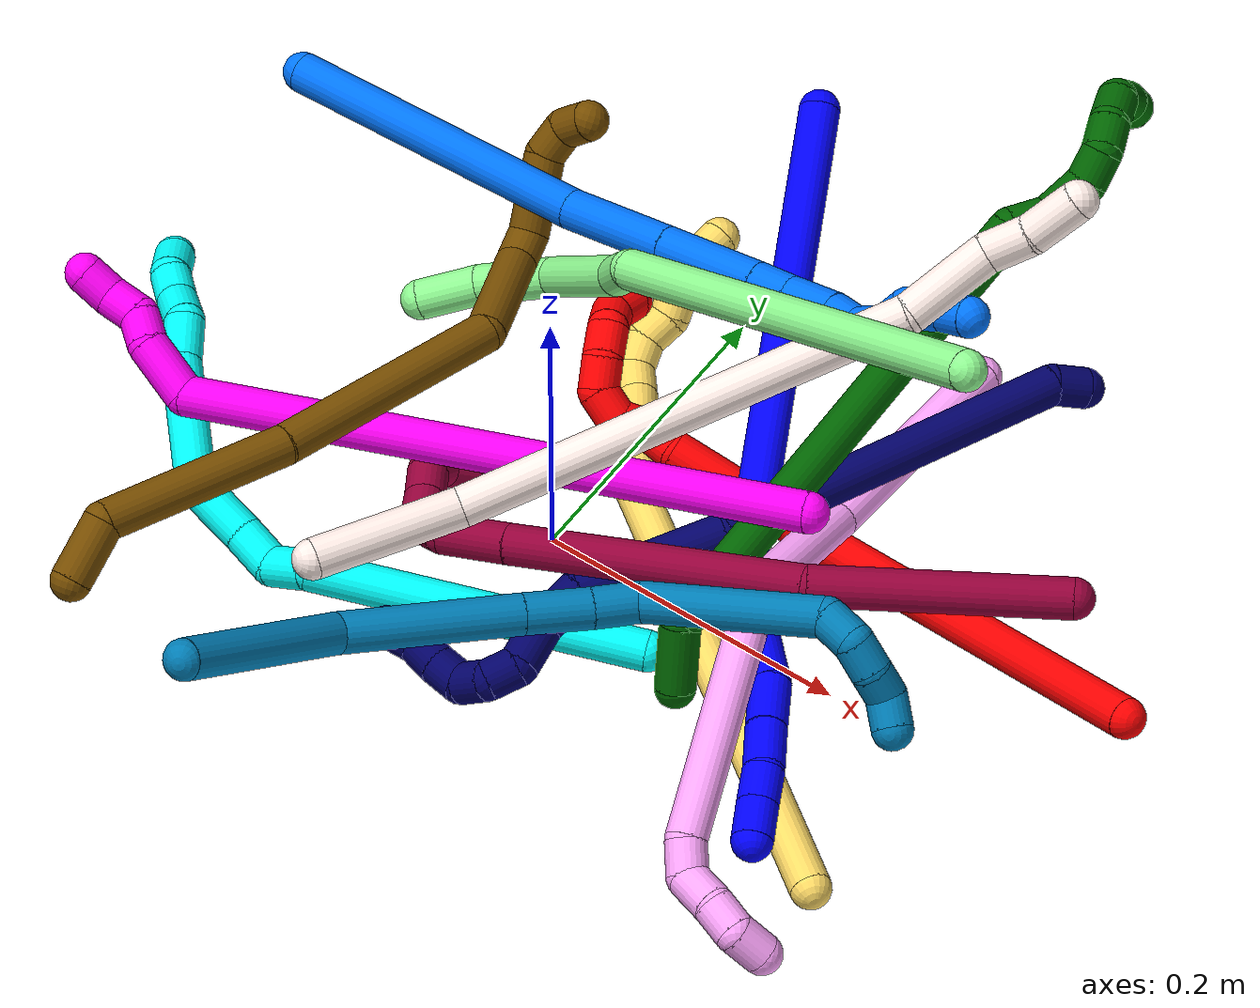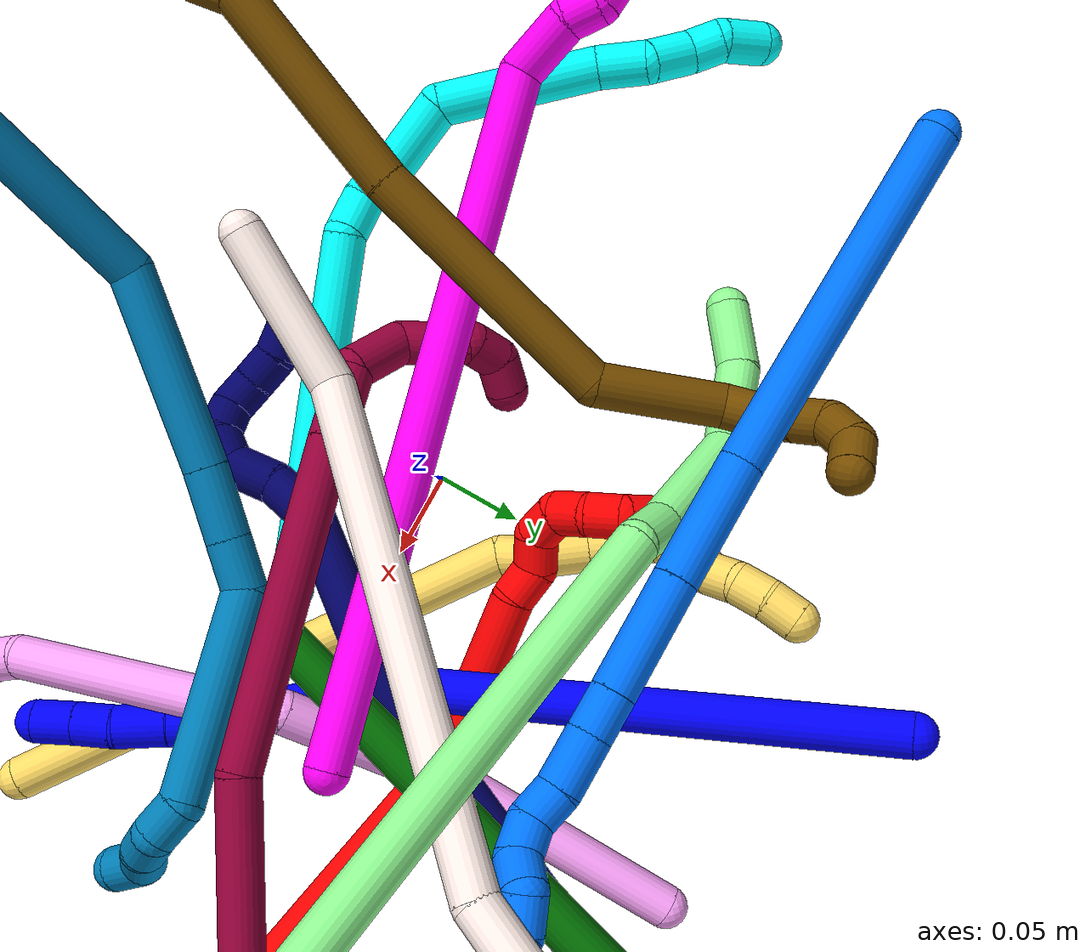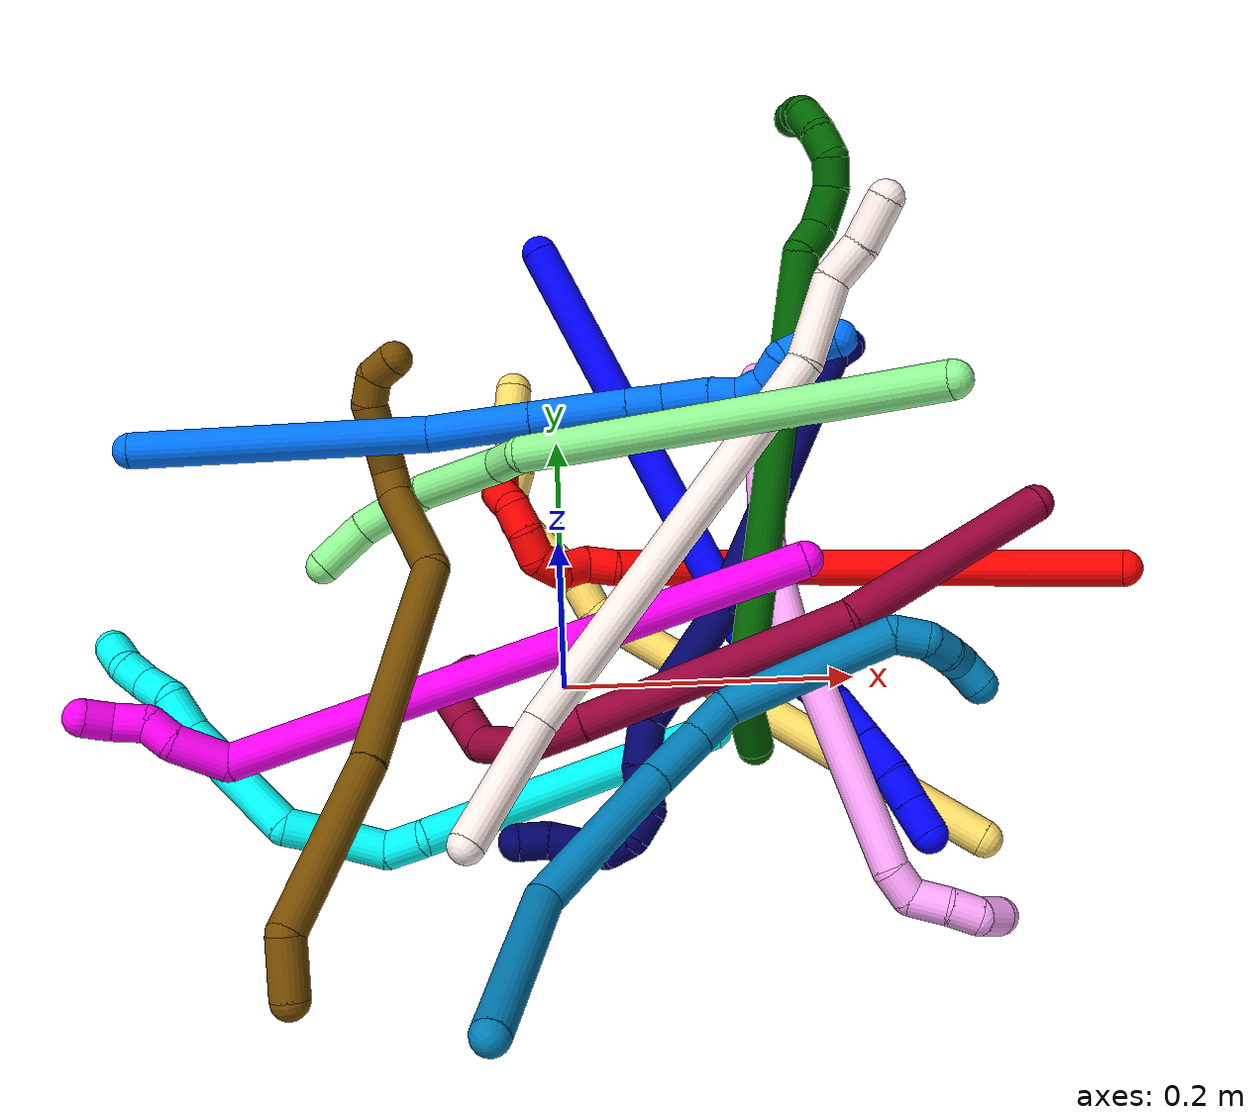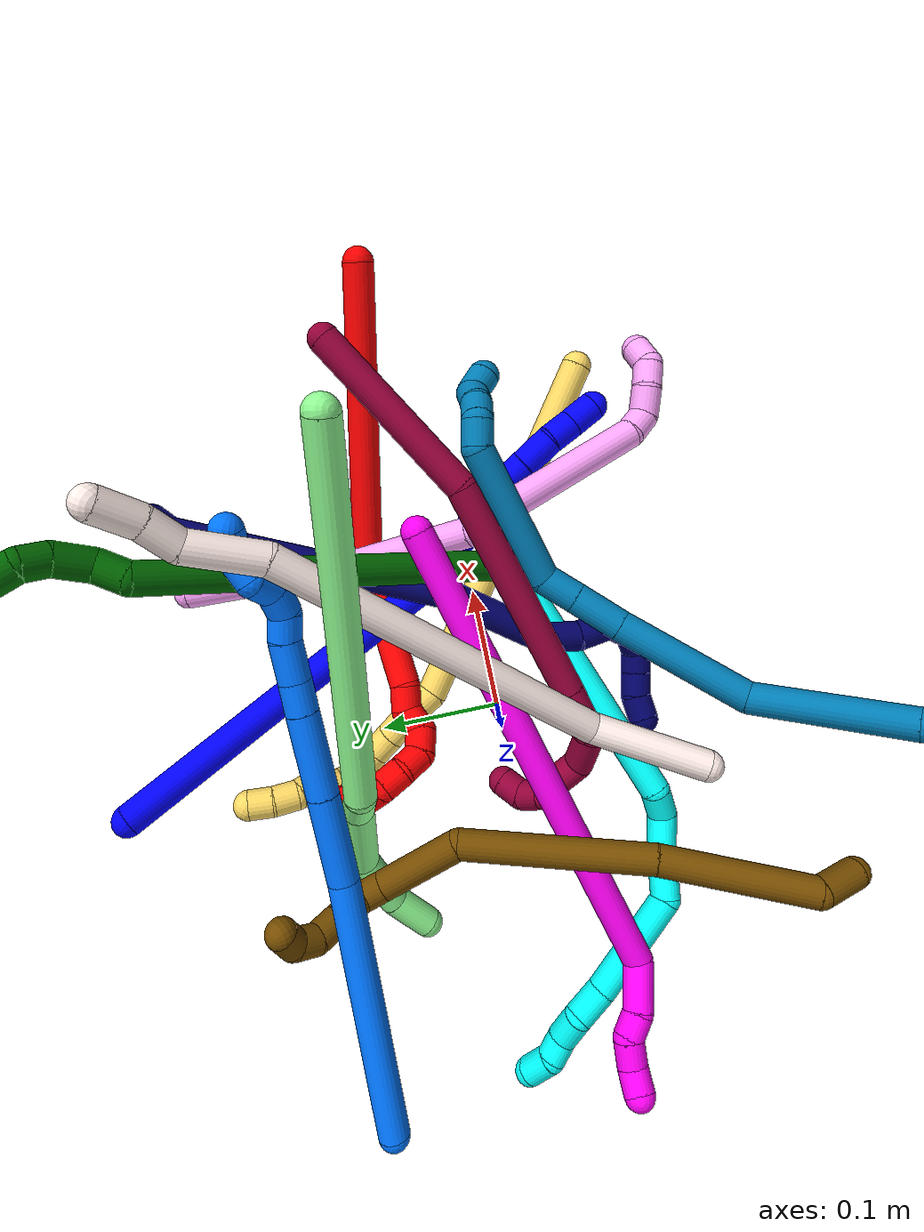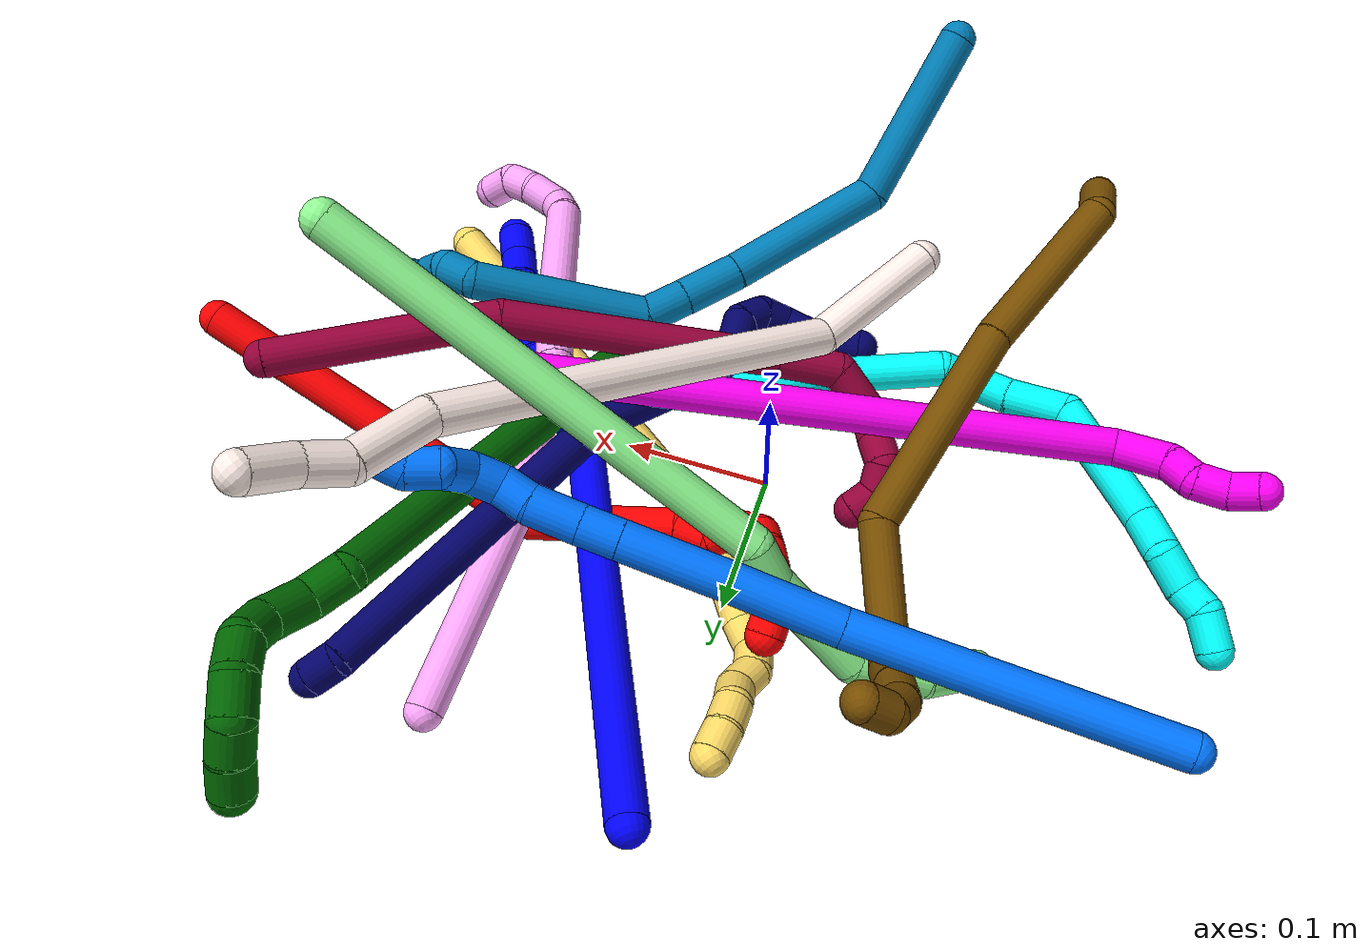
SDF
<sdf version="1.7">
 <world name="default">
  <plugin name="TubeGeneratorPlugin" filename="libtube_generator_plugin.so"/>
  <model name="photoneo_s_sensor">
   <static>1</static>
   <pose>0 0 2 1.57079 1.57079 3.14159</pose>
   <link name="link">
    <inertial><mass>0.1</mass></inertial>
    <sensor name="sensor" type="depth">
     <update_rate>30</update_rate>
     <camera>
      <horizontal_fov>1.22</horizontal_fov>
      <image><width>1920</width><height>1200</height><format>B8G8R8</format></image>
      <clip><near>0.1</near><far>4</far></clip>
      <depth_camera><output>points</output></depth_camera>
     </camera>
     <plugin name="camera_plugin" filename="libgazebo_ros_depth_camera.so">
      <baseline>0.2</baseline>
      <alwaysOn>1</alwaysOn>
      <updateRate>0.0</updateRate>
      <cameraName>camera_ir</cameraName>
      <imageTopicName>/camera/color/image_raw</imageTopicName>
      <cameraInfoTopicName>/camera/color/camera_info</cameraInfoTopicName>
      <depthImageTopicName>/camera/depth/image_raw</depthImageTopicName>
      <depthImageCameraInfoTopicName>/camera/depth/camera_info</depthImageCameraInfoTopicName>
      <pointCloudTopicName>/camera/depth/points</pointCloudTopicName>
      <frameName>fr_optical</frameName>
      <pointCloudCutoff>0.1</pointCloudCutoff>
      <pointCloudCutoffMax>2.0</pointCloudCutoffMax>
      <distortionK1>0</distortionK1>
      <distortionK2>0</distortionK2>
      <distortionK3>0</distortionK3>
      <distortionT1>0</distortionT1>
      <distortionT2>0</distortionT2>
      <CxPrime>0</CxPrime>
      <Cx>0</Cx>
      <Cy>0</Cy>
      <focalLength>0</focalLength>
      <hackBaseline>0</hackBaseline>
     </plugin>
    </sensor>
   </link>
  </model>
  <gravity>0 0 -9.8</gravity>
  <magnetic_field>6e-06 2.3e-05 -4.2e-05</magnetic_field>
  <atmosphere type="adiabatic"/>
  <physics name="default_physics" default="0" type="ode">
   <max_step_size>0.003</max_step_size>
   <real_time_factor>1</real_time_factor>
   <real_time_update_rate>1000</real_time_update_rate>
   <max_contacts>10000</max_contacts>
   <ode>
    <solver>
     <type>quick</type>
     <iters>100</iters>
     <sor>1.3</sor>
     <use_dynamic_moi_rescaling>0</use_dynamic_moi_rescaling>
    </solver>
    <constraints>
     <contact_max_correcting_vel>0</contact_max_correcting_vel>
     <contact_surface_layer>0.001</contact_surface_layer>
     <cfm>0</cfm>
     <erp>0.2</erp>
    </constraints>
   </ode>
  </physics>
  <scene><ambient>0.4 0.4 0.4 1</ambient><background>0.7 0.7 0.7 1</background><shadows>0</shadows></scene>
  <audio><device>default</device></audio>
  <spherical_coordinates>
   <surface_model>EARTH_WGS84</surface_model>
   <latitude_deg>0</latitude_deg>
   <longitude_deg>0</longitude_deg>
   <elevation>0</elevation>
   <heading_deg>0</heading_deg>
  </spherical_coordinates>
  <model name="bin">
   <static>1</static>
   <link name="bottom">
    <collision name="collision-bottom">
     <pose>0 0 -0.01 0 -0 0</pose>
     <geometry><box><size>0.8 0.6 0.02</size></box></geometry>
     <surface>
      <friction><ode><mu>100</mu><mu2>100</mu2></ode></friction>
      <contact><collide_bitmask>65535</collide_bitmask></contact>
     </surface>
    </collision>
   </link>
   <link name="west_wall">
    <collision name="collision-west_wall">
     <pose>-0.41 0 0.1 0 -0 0</pose>
     <geometry><box><size>0.02 0.6 0.2</size></box></geometry>
     <surface>
      <friction><ode><mu>100</mu><mu2>100</mu2></ode></friction>
      <contact><collide_bitmask>65535</collide_bitmask></contact>
     </surface>
    </collision>
   </link>
   <link name="east_wall">
    <collision name="collision-east_wall">
     <pose>0.41 0 0.1 0 -0 0</pose>
     <geometry><box><size>0.02 0.6 0.2</size></box></geometry>
     <surface>
      <friction><ode><mu>100</mu><mu2>100</mu2></ode></friction>
      <contact><collide_bitmask>65535</collide_bitmask></contact>
     </surface>
    </collision>
   </link>
   <link name="south_wall">
    <collision name="collision-south_wall">
     <pose>0 -0.31 0.1 0 -0 0</pose>
     <geometry><box><size>0.8 0.02 0.2</size></box></geometry>
     <surface>
      <friction><ode><mu>100</mu><mu2>100</mu2></ode></friction>
      <contact><collide_bitmask>65535</collide_bitmask></contact>
     </surface>
    </collision>
   </link>
   <link name="north_wall">
    <collision name="collision-north_wall">
     <pose>0 0.31 0.1 0 -0 0</pose>
     <geometry><box><size>0.8 0.02 0.2</size></box></geometry>
     <surface>
      <friction><ode><mu>100</mu><mu2>100</mu2></ode></friction>
      <contact><collide_bitmask>65535</collide_bitmask></contact>
     </surface>
    </collision>
   </link>
  </model>
  <model name="1">
   <static>0</static>
   <link name="1">
    <collision name="collision-cylinder-e_1_1_4">
     <pose>0.039707 -0.030496 0.144588 0.207872 0.262507 0.027539</pose>
     <geometry><cylinder><radius>0.0125</radius><length>0.306021</length></cylinder></geometry>
     <surface>
      <friction><ode><mu>1.16</mu><mu2>1.16</mu2><slip1>0</slip1><slip2>0</slip2></ode></friction>
      <contact><ode><kp>1e+06</kp><kd>1</kd><max_vel>0</max_vel><min_depth>0.001</min_depth></ode></contact>
     </surface>
    </collision>
    <visual name="visual-cylinder-e_1_1_4">
     <pose>0.039707 -0.030496 0.144588 0.207872 0.262507 0.027539</pose>
     <geometry><cylinder><radius>0.0125</radius><length>0.306021</length></cylinder></geometry>
     <material><ambient>0 0 1 1</ambient></material>
    </visual>
    <collision name="collision-cylinder-e_2_4_5">
     <pose>0.083976 -0.058505 0.303322 -0.174083 0.307562 -0.02705</pose>
     <geometry><cylinder><radius>0.0125</radius><length>0.030142</length></cylinder></geometry>
     <surface>
      <friction><ode><mu>1.16</mu><mu2>1.16</mu2><slip1>0</slip1><slip2>0</slip2></ode></friction>
      <contact><ode><kp>1e+06</kp><kd>1</kd><max_vel>0</max_vel><min_depth>0.001</min_depth></ode></contact>
     </surface>
    </collision>
    <visual name="visual-cylinder-e_2_4_5">
     <pose>0.083976 -0.058505 0.303322 -0.174083 0.307562 -0.02705</pose>
     <geometry><cylinder><radius>0.0125</radius><length>0.030142</length></cylinder></geometry>
     <material><ambient>0 0 1 1</ambient></material>
    </visual>
    <collision name="collision-cylinder-e_3_5_6">
     <pose>0.084824 -0.052026 0.343934 -0.149663 -0.137899 0.010355</pose>
     <geometry><cylinder><radius>0.0125</radius><length>0.054043</length></cylinder></geometry>
     <surface>
      <friction><ode><mu>1.16</mu><mu2>1.16</mu2><slip1>0</slip1><slip2>0</slip2></ode></friction>
      <contact><ode><kp>1e+06</kp><kd>1</kd><max_vel>0</max_vel><min_depth>0.001</min_depth></ode></contact>
     </surface>
    </collision>
    <visual name="visual-cylinder-e_3_5_6">
     <pose>0.084824 -0.052026 0.343934 -0.149663 -0.137899 0.010355</pose>
     <geometry><cylinder><radius>0.0125</radius><length>0.054043</length></cylinder></geometry>
     <material><ambient>0 0 1 1</ambient></material>
    </visual>
    <collision name="collision-cylinder-e_4_6_7">
     <pose>0.07992 -0.049669 0.387039 0.097863 -0.071012 -0.003479</pose>
     <geometry><cylinder><radius>0.0125</radius><length>0.033524</length></cylinder></geometry>
     <surface>
      <friction><ode><mu>1.16</mu><mu2>1.16</mu2><slip1>0</slip1><slip2>0</slip2></ode></friction>
      <contact><ode><kp>1e+06</kp><kd>1</kd><max_vel>0</max_vel><min_depth>0.001</min_depth></ode></contact>
     </surface>
    </collision>
    <visual name="visual-cylinder-e_4_6_7">
     <pose>0.07992 -0.049669 0.387039 0.097863 -0.071012 -0.003479</pose>
     <geometry><cylinder><radius>0.0125</radius><length>0.033524</length></cylinder></geometry>
     <material><ambient>0 0 1 1</ambient></material>
    </visual>
    <collision name="collision-cylinder-e_5_7_8">
     <pose>0.078472 -0.052462 0.418593 0.077551 -0.017314 -0.000672</pose>
     <geometry><cylinder><radius>0.0125</radius><length>0.029922</length></cylinder></geometry>
     <surface>
      <friction><ode><mu>1.16</mu><mu2>1.16</mu2><slip1>0</slip1><slip2>0</slip2></ode></friction>
      <contact><ode><kp>1e+06</kp><kd>1</kd><max_vel>0</max_vel><min_depth>0.001</min_depth></ode></contact>
     </surface>
    </collision>
    <visual name="visual-cylinder-e_5_7_8">
     <pose>0.078472 -0.052462 0.418593 0.077551 -0.017314 -0.000672</pose>
     <geometry><cylinder><radius>0.0125</radius><length>0.029922</length></cylinder></geometry>
     <material><ambient>0 0 1 1</ambient></material>
    </visual>
    <collision name="collision-cylinder-e_6_8_9">
     <pose>0.079764 -0.055832 0.444472 0.199059 0.137829 0.013785</pose>
     <geometry><cylinder><radius>0.0125</radius><length>0.022586</length></cylinder></geometry>
     <surface>
      <friction><ode><mu>1.16</mu><mu2>1.16</mu2><slip1>0</slip1><slip2>0</slip2></ode></friction>
      <contact><ode><kp>1e+06</kp><kd>1</kd><max_vel>0</max_vel><min_depth>0.001</min_depth></ode></contact>
     </surface>
    </collision>
    <visual name="visual-cylinder-e_6_8_9">
     <pose>0.079764 -0.055832 0.444472 0.199059 0.137829 0.013785</pose>
     <geometry><cylinder><radius>0.0125</radius><length>0.022586</length></cylinder></geometry>
     <material><ambient>0 0 1 1</ambient></material>
    </visual>
    <collision name="collision-cylinder-e_7_9_2">
     <pose>0.08249 -0.060022 0.467093 0.168066 0.098988 0.008345</pose>
     <geometry><cylinder><radius>0.0125</radius><length>0.023763</length></cylinder></geometry>
     <surface>
      <friction><ode><mu>1.16</mu><mu2>1.16</mu2><slip1>0</slip1><slip2>0</slip2></ode></friction>
      <contact><ode><kp>1e+06</kp><kd>1</kd><max_vel>0</max_vel><min_depth>0.001</min_depth></ode></contact>
     </surface>
    </collision>
    <visual name="visual-cylinder-e_7_9_2">
     <pose>0.08249 -0.060022 0.467093 0.168066 0.098988 0.008345</pose>
     <geometry><cylinder><radius>0.0125</radius><length>0.023763</length></cylinder></geometry>
     <material><ambient>0 0 1 1</ambient></material>
    </visual>
    <collision name="collision-sphere-2">
     <pose>0.083664 -0.062 0.47875 0 -0 0</pose>
     <geometry><sphere><radius>0.0125</radius></sphere></geometry>
     <surface>
      <friction><ode><mu>1.16</mu><mu2>1.16</mu2><slip1>0</slip1><slip2>0</slip2></ode></friction>
      <contact><ode><kp>1e+06</kp><kd>1</kd><max_vel>0</max_vel><min_depth>0.001</min_depth></ode></contact>
     </surface>
    </collision>
    <visual name="visual-sphere-2">
     <pose>0.083664 -0.062 0.47875 0 -0 0</pose>
     <geometry><sphere><radius>0.0125</radius></sphere></geometry>
     <material><ambient>0 0 1 1</ambient></material>
    </visual>
    <collision name="collision-sphere-9">
     <pose>0.081316 -0.058044 0.455437 0 -0 0</pose>
     <geometry><sphere><radius>0.0125</radius></sphere></geometry>
     <surface>
      <friction><ode><mu>1.16</mu><mu2>1.16</mu2><slip1>0</slip1><slip2>0</slip2></ode></friction>
      <contact><ode><kp>1e+06</kp><kd>1</kd><max_vel>0</max_vel><min_depth>0.001</min_depth></ode></contact>
     </surface>
    </collision>
    <visual name="visual-sphere-9">
     <pose>0.081316 -0.058044 0.455437 0 -0 0</pose>
     <geometry><sphere><radius>0.0125</radius></sphere></geometry>
     <material><ambient>0 0 1 1</ambient></material>
    </visual>
    <collision name="collision-sphere-4">
     <pose>0.079413 -0.060993 0.289175 0 -0 0</pose>
     <geometry><sphere><radius>0.0125</radius></sphere></geometry>
     <surface>
      <friction><ode><mu>1.16</mu><mu2>1.16</mu2><slip1>0</slip1><slip2>0</slip2></ode></friction>
      <contact><ode><kp>1e+06</kp><kd>1</kd><max_vel>0</max_vel><min_depth>0.001</min_depth></ode></contact>
     </surface>
    </collision>
    <visual name="visual-sphere-4">
     <pose>0.079413 -0.060993 0.289175 0 -0 0</pose>
     <geometry><sphere><radius>0.0125</radius></sphere></geometry>
     <material><ambient>0 0 1 1</ambient></material>
    </visual>
    <collision name="collision-sphere-1">
     <geometry><sphere><radius>0.0125</radius></sphere></geometry>
     <surface>
      <friction><ode><mu>1.16</mu><mu2>1.16</mu2><slip1>0</slip1><slip2>0</slip2></ode></friction>
      <contact><ode><kp>1e+06</kp><kd>1</kd><max_vel>0</max_vel><min_depth>0.001</min_depth></ode></contact>
     </surface>
    </collision>
    <visual name="visual-sphere-1">
     <geometry><sphere><radius>0.0125</radius></sphere></geometry>
     <material><ambient>0 0 1 1</ambient></material>
    </visual>
    <collision name="collision-sphere-8">
     <pose>0.078213 -0.05362 0.433507 0 -0 0</pose>
     <geometry><sphere><radius>0.0125</radius></sphere></geometry>
     <surface>
      <friction><ode><mu>1.16</mu><mu2>1.16</mu2><slip1>0</slip1><slip2>0</slip2></ode></friction>
      <contact><ode><kp>1e+06</kp><kd>1</kd><max_vel>0</max_vel><min_depth>0.001</min_depth></ode></contact>
     </surface>
    </collision>
    <visual name="visual-sphere-8">
     <pose>0.078213 -0.05362 0.433507 0 -0 0</pose>
     <geometry><sphere><radius>0.0125</radius></sphere></geometry>
     <material><ambient>0 0 1 1</ambient></material>
    </visual>
    <collision name="collision-sphere-5">
     <pose>0.088538 -0.056017 0.317468 0 -0 0</pose>
     <geometry><sphere><radius>0.0125</radius></sphere></geometry>
     <surface>
      <friction><ode><mu>1.16</mu><mu2>1.16</mu2><slip1>0</slip1><slip2>0</slip2></ode></friction>
      <contact><ode><kp>1e+06</kp><kd>1</kd><max_vel>0</max_vel><min_depth>0.001</min_depth></ode></contact>
     </surface>
    </collision>
    <visual name="visual-sphere-5">
     <pose>0.088538 -0.056017 0.317468 0 -0 0</pose>
     <geometry><sphere><radius>0.0125</radius></sphere></geometry>
     <material><ambient>0 0 1 1</ambient></material>
    </visual>
    <collision name="collision-sphere-6">
     <pose>0.08111 -0.048035 0.370399 0 -0 0</pose>
     <geometry><sphere><radius>0.0125</radius></sphere></geometry>
     <surface>
      <friction><ode><mu>1.16</mu><mu2>1.16</mu2><slip1>0</slip1><slip2>0</slip2></ode></friction>
      <contact><ode><kp>1e+06</kp><kd>1</kd><max_vel>0</max_vel><min_depth>0.001</min_depth></ode></contact>
     </surface>
    </collision>
    <visual name="visual-sphere-6">
     <pose>0.08111 -0.048035 0.370399 0 -0 0</pose>
     <geometry><sphere><radius>0.0125</radius></sphere></geometry>
     <material><ambient>0 0 1 1</ambient></material>
    </visual>
    <collision name="collision-sphere-7">
     <pose>0.078731 -0.051303 0.403679 0 -0 0</pose>
     <geometry><sphere><radius>0.0125</radius></sphere></geometry>
     <surface>
      <friction><ode><mu>1.16</mu><mu2>1.16</mu2><slip1>0</slip1><slip2>0</slip2></ode></friction>
      <contact><ode><kp>1e+06</kp><kd>1</kd><max_vel>0</max_vel><min_depth>0.001</min_depth></ode></contact>
     </surface>
    </collision>
    <visual name="visual-sphere-7">
     <pose>0.078731 -0.051303 0.403679 0 -0 0</pose>
     <geometry><sphere><radius>0.0125</radius></sphere></geometry>
     <material><ambient>0 0 1 1</ambient></material>
    </visual>
    <inertial>
     <pose>0.056111 -0.039659 0.23723 0 -0 0</pose>
     <mass>0.5</mass>
     <inertia>
      <ixx>0.002418</ixx>
      <ixy>0</ixy>
      <ixz>0</ixz>
      <iyy>0.00244</iyy>
      <iyz>0</iyz>
      <izz>-0.000108</izz>
     </inertia>
    </inertial>
   </link>
   <pose>-0.006765 0.288398 0.114786 1.46129 1.46125 0.521222</pose>
  </model>
  <model name="2">
   <static>0</static>
   <link name="2">
    <collision name="collision-cylinder-e_1_1_4">
     <pose>-0.026045 -0.007486 -0.121809 3.08021 -0.210261 -2.57535</pose>
     <geometry><cylinder><radius>0.0125</radius><length>0.249575</length></cylinder></geometry>
     <surface>
      <friction><ode><mu>1.16</mu><mu2>1.16</mu2><slip1>0</slip1><slip2>0</slip2></ode></friction>
      <contact><ode><kp>1e+06</kp><kd>1</kd><max_vel>0</max_vel><min_depth>0.001</min_depth></ode></contact>
     </surface>
    </collision>
    <visual name="visual-cylinder-e_1_1_4">
     <pose>-0.026045 -0.007486 -0.121809 3.08021 -0.210261 -2.57535</pose>
     <geometry><cylinder><radius>0.0125</radius><length>0.249575</length></cylinder></geometry>
     <material><ambient>1 0 0 1</ambient></material>
    </visual>
    <collision name="collision-cylinder-e_2_4_5">
     <pose>-0.085005 -0.037875 -0.280285 2.58327 -0.650732 -1.73296</pose>
     <geometry><cylinder><radius>0.0125</radius><length>0.108671</length></cylinder></geometry>
     <surface>
      <friction><ode><mu>1.16</mu><mu2>1.16</mu2><slip1>0</slip1><slip2>0</slip2></ode></friction>
      <contact><ode><kp>1e+06</kp><kd>1</kd><max_vel>0</max_vel><min_depth>0.001</min_depth></ode></contact>
     </surface>
    </collision>
    <visual name="visual-cylinder-e_2_4_5">
     <pose>-0.085005 -0.037875 -0.280285 2.58327 -0.650732 -1.73296</pose>
     <geometry><cylinder><radius>0.0125</radius><length>0.108671</length></cylinder></geometry>
     <material><ambient>1 0 0 1</ambient></material>
    </visual>
    <collision name="collision-cylinder-e_3_5_6">
     <pose>-0.123359 -0.062564 -0.325711 2.94032 -0.54662 -2.45011</pose>
     <geometry><cylinder><radius>0.0125</radius><length>0.020929</length></cylinder></geometry>
     <surface>
      <friction><ode><mu>1.16</mu><mu2>1.16</mu2><slip1>0</slip1><slip2>0</slip2></ode></friction>
      <contact><ode><kp>1e+06</kp><kd>1</kd><max_vel>0</max_vel><min_depth>0.001</min_depth></ode></contact>
     </surface>
    </collision>
    <visual name="visual-cylinder-e_3_5_6">
     <pose>-0.123359 -0.062564 -0.325711 2.94032 -0.54662 -2.45011</pose>
     <geometry><cylinder><radius>0.0125</radius><length>0.020929</length></cylinder></geometry>
     <material><ambient>1 0 0 1</ambient></material>
    </visual>
    <collision name="collision-cylinder-e_4_6_7">
     <pose>-0.134251 -0.071462 -0.339199 2.15768 -0.568302 -0.997955</pose>
     <geometry><cylinder><radius>0.0125</radius><length>0.020263</length></cylinder></geometry>
     <surface>
      <friction><ode><mu>1.16</mu><mu2>1.16</mu2><slip1>0</slip1><slip2>0</slip2></ode></friction>
      <contact><ode><kp>1e+06</kp><kd>1</kd><max_vel>0</max_vel><min_depth>0.001</min_depth></ode></contact>
     </surface>
    </collision>
    <visual name="visual-cylinder-e_4_6_7">
     <pose>-0.134251 -0.071462 -0.339199 2.15768 -0.568302 -0.997955</pose>
     <geometry><cylinder><radius>0.0125</radius><length>0.020263</length></cylinder></geometry>
     <material><ambient>1 0 0 1</ambient></material>
    </visual>
    <collision name="collision-cylinder-e_5_7_8">
     <pose>-0.148343 -0.079646 -0.349035 2.93428 -1.02732 -2.7769</pose>
     <geometry><cylinder><radius>0.0125</radius><length>0.020185</length></cylinder></geometry>
     <surface>
      <friction><ode><mu>1.16</mu><mu2>1.16</mu2><slip1>0</slip1><slip2>0</slip2></ode></friction>
      <contact><ode><kp>1e+06</kp><kd>1</kd><max_vel>0</max_vel><min_depth>0.001</min_depth></ode></contact>
     </surface>
    </collision>
    <visual name="visual-cylinder-e_5_7_8">
     <pose>-0.148343 -0.079646 -0.349035 2.93428 -1.02732 -2.7769</pose>
     <geometry><cylinder><radius>0.0125</radius><length>0.020185</length></cylinder></geometry>
     <material><ambient>1 0 0 1</ambient></material>
    </visual>
    <collision name="collision-cylinder-e_6_8_9">
     <pose>-0.165323 -0.075345 -0.356228 -1.94095 -0.965999 1.30736</pose>
     <geometry><cylinder><radius>0.0125</radius><length>0.020282</length></cylinder></geometry>
     <surface>
      <friction><ode><mu>1.16</mu><mu2>1.16</mu2><slip1>0</slip1><slip2>0</slip2></ode></friction>
      <contact><ode><kp>1e+06</kp><kd>1</kd><max_vel>0</max_vel><min_depth>0.001</min_depth></ode></contact>
     </surface>
    </collision>
    <visual name="visual-cylinder-e_6_8_9">
     <pose>-0.165323 -0.075345 -0.356228 -1.94095 -0.965999 1.30736</pose>
     <geometry><cylinder><radius>0.0125</radius><length>0.020282</length></cylinder></geometry>
     <material><ambient>1 0 0 1</ambient></material>
    </visual>
    <collision name="collision-cylinder-e_7_9_10">
     <pose>-0.179929 -0.063303 -0.3624 -2.12069 -0.675441 1.12029</pose>
     <geometry><cylinder><radius>0.0125</radius><length>0.020036</length></cylinder></geometry>
     <surface>
      <friction><ode><mu>1.16</mu><mu2>1.16</mu2><slip1>0</slip1><slip2>0</slip2></ode></friction>
      <contact><ode><kp>1e+06</kp><kd>1</kd><max_vel>0</max_vel><min_depth>0.001</min_depth></ode></contact>
     </surface>
    </collision>
    <visual name="visual-cylinder-e_7_9_10">
     <pose>-0.179929 -0.063303 -0.3624 -2.12069 -0.675441 1.12029</pose>
     <geometry><cylinder><radius>0.0125</radius><length>0.020036</length></cylinder></geometry>
     <material><ambient>1 0 0 1</ambient></material>
    </visual>
    <collision name="collision-cylinder-e_8_10_11">
     <pose>-0.186478 -0.049674 -0.373688 -2.37307 -0.028467 0.070377</pose>
     <geometry><cylinder><radius>0.0125</radius><length>0.020044</length></cylinder></geometry>
     <surface>
      <friction><ode><mu>1.16</mu><mu2>1.16</mu2><slip1>0</slip1><slip2>0</slip2></ode></friction>
      <contact><ode><kp>1e+06</kp><kd>1</kd><max_vel>0</max_vel><min_depth>0.001</min_depth></ode></contact>
     </surface>
    </collision>
    <visual name="visual-cylinder-e_8_10_11">
     <pose>-0.186478 -0.049674 -0.373688 -2.37307 -0.028467 0.070377</pose>
     <geometry><cylinder><radius>0.0125</radius><length>0.020044</length></cylinder></geometry>
     <material><ambient>1 0 0 1</ambient></material>
    </visual>
    <collision name="collision-cylinder-e_9_11_2">
     <pose>-0.185936 -0.033224 -0.383967 -1.8844 0.082737 -0.113752</pose>
     <geometry><cylinder><radius>0.0125</radius><length>0.020015</length></cylinder></geometry>
     <surface>
      <friction><ode><mu>1.16</mu><mu2>1.16</mu2><slip1>0</slip1><slip2>0</slip2></ode></friction>
      <contact><ode><kp>1e+06</kp><kd>1</kd><max_vel>0</max_vel><min_depth>0.001</min_depth></ode></contact>
     </surface>
    </collision>
    <visual name="visual-cylinder-e_9_11_2">
     <pose>-0.185936 -0.033224 -0.383967 -1.8844 0.082737 -0.113752</pose>
     <geometry><cylinder><radius>0.0125</radius><length>0.020015</length></cylinder></geometry>
     <material><ambient>1 0 0 1</ambient></material>
    </visual>
    <collision name="collision-sphere-2">
     <pose>-0.185109 -0.023738 -0.387044 0 -0 0</pose>
     <geometry><sphere><radius>0.0125</radius></sphere></geometry>
     <surface>
      <friction><ode><mu>1.16</mu><mu2>1.16</mu2><slip1>0</slip1><slip2>0</slip2></ode></friction>
      <contact><ode><kp>1e+06</kp><kd>1</kd><max_vel>0</max_vel><min_depth>0.001</min_depth></ode></contact>
     </surface>
    </collision>
    <visual name="visual-sphere-2">
     <pose>-0.185109 -0.023738 -0.387044 0 -0 0</pose>
     <geometry><sphere><radius>0.0125</radius></sphere></geometry>
     <material><ambient>1 0 0 1</ambient></material>
    </visual>
    <collision name="collision-sphere-11">
     <pose>-0.186763 -0.042711 -0.380891 0 -0 0</pose>
     <geometry><sphere><radius>0.0125</radius></sphere></geometry>
     <surface>
      <friction><ode><mu>1.16</mu><mu2>1.16</mu2><slip1>0</slip1><slip2>0</slip2></ode></friction>
      <contact><ode><kp>1e+06</kp><kd>1</kd><max_vel>0</max_vel><min_depth>0.001</min_depth></ode></contact>
     </surface>
    </collision>
    <visual name="visual-sphere-11">
     <pose>-0.186763 -0.042711 -0.380891 0 -0 0</pose>
     <geometry><sphere><radius>0.0125</radius></sphere></geometry>
     <material><ambient>1 0 0 1</ambient></material>
    </visual>
    <collision name="collision-sphere-10">
     <pose>-0.186193 -0.056638 -0.366486 0 -0 0</pose>
     <geometry><sphere><radius>0.0125</radius></sphere></geometry>
     <surface>
      <friction><ode><mu>1.16</mu><mu2>1.16</mu2><slip1>0</slip1><slip2>0</slip2></ode></friction>
      <contact><ode><kp>1e+06</kp><kd>1</kd><max_vel>0</max_vel><min_depth>0.001</min_depth></ode></contact>
     </surface>
    </collision>
    <visual name="visual-sphere-10">
     <pose>-0.186193 -0.056638 -0.366486 0 -0 0</pose>
     <geometry><sphere><radius>0.0125</radius></sphere></geometry>
     <material><ambient>1 0 0 1</ambient></material>
    </visual>
    <collision name="collision-sphere-9">
     <pose>-0.173666 -0.069969 -0.358314 0 -0 0</pose>
     <geometry><sphere><radius>0.0125</radius></sphere></geometry>
     <surface>
      <friction><ode><mu>1.16</mu><mu2>1.16</mu2><slip1>0</slip1><slip2>0</slip2></ode></friction>
      <contact><ode><kp>1e+06</kp><kd>1</kd><max_vel>0</max_vel><min_depth>0.001</min_depth></ode></contact>
     </surface>
    </collision>
    <visual name="visual-sphere-9">
     <pose>-0.173666 -0.069969 -0.358314 0 -0 0</pose>
     <geometry><sphere><radius>0.0125</radius></sphere></geometry>
     <material><ambient>1 0 0 1</ambient></material>
    </visual>
    <collision name="collision-sphere-4">
     <pose>-0.05209 -0.014972 -0.243619 0 -0 0</pose>
     <geometry><sphere><radius>0.0125</radius></sphere></geometry>
     <surface>
      <friction><ode><mu>1.16</mu><mu2>1.16</mu2><slip1>0</slip1><slip2>0</slip2></ode></friction>
      <contact><ode><kp>1e+06</kp><kd>1</kd><max_vel>0</max_vel><min_depth>0.001</min_depth></ode></contact>
     </surface>
    </collision>
    <visual name="visual-sphere-4">
     <pose>-0.05209 -0.014972 -0.243619 0 -0 0</pose>
     <geometry><sphere><radius>0.0125</radius></sphere></geometry>
     <material><ambient>1 0 0 1</ambient></material>
    </visual>
    <collision name="collision-sphere-1">
     <geometry><sphere><radius>0.0125</radius></sphere></geometry>
     <surface>
      <friction><ode><mu>1.16</mu><mu2>1.16</mu2><slip1>0</slip1><slip2>0</slip2></ode></friction>
      <contact><ode><kp>1e+06</kp><kd>1</kd><max_vel>0</max_vel><min_depth>0.001</min_depth></ode></contact>
     </surface>
    </collision>
    <visual name="visual-sphere-1">
     <geometry><sphere><radius>0.0125</radius></sphere></geometry>
     <material><ambient>1 0 0 1</ambient></material>
    </visual>
    <collision name="collision-sphere-8">
     <pose>-0.156981 -0.08072 -0.354142 0 -0 0</pose>
     <geometry><sphere><radius>0.0125</radius></sphere></geometry>
     <surface>
      <friction><ode><mu>1.16</mu><mu2>1.16</mu2><slip1>0</slip1><slip2>0</slip2></ode></friction>
      <contact><ode><kp>1e+06</kp><kd>1</kd><max_vel>0</max_vel><min_depth>0.001</min_depth></ode></contact>
     </surface>
    </collision>
    <visual name="visual-sphere-8">
     <pose>-0.156981 -0.08072 -0.354142 0 -0 0</pose>
     <geometry><sphere><radius>0.0125</radius></sphere></geometry>
     <material><ambient>1 0 0 1</ambient></material>
    </visual>
    <collision name="collision-sphere-5">
     <pose>-0.11792 -0.060777 -0.316952 0 -0 0</pose>
     <geometry><sphere><radius>0.0125</radius></sphere></geometry>
     <surface>
      <friction><ode><mu>1.16</mu><mu2>1.16</mu2><slip1>0</slip1><slip2>0</slip2></ode></friction>
      <contact><ode><kp>1e+06</kp><kd>1</kd><max_vel>0</max_vel><min_depth>0.001</min_depth></ode></contact>
     </surface>
    </collision>
    <visual name="visual-sphere-5">
     <pose>-0.11792 -0.060777 -0.316952 0 -0 0</pose>
     <geometry><sphere><radius>0.0125</radius></sphere></geometry>
     <material><ambient>1 0 0 1</ambient></material>
    </visual>
    <collision name="collision-sphere-6">
     <pose>-0.128798 -0.064351 -0.33447 0 -0 0</pose>
     <geometry><sphere><radius>0.0125</radius></sphere></geometry>
     <surface>
      <friction><ode><mu>1.16</mu><mu2>1.16</mu2><slip1>0</slip1><slip2>0</slip2></ode></friction>
      <contact><ode><kp>1e+06</kp><kd>1</kd><max_vel>0</max_vel><min_depth>0.001</min_depth></ode></contact>
     </surface>
    </collision>
    <visual name="visual-sphere-6">
     <pose>-0.128798 -0.064351 -0.33447 0 -0 0</pose>
     <geometry><sphere><radius>0.0125</radius></sphere></geometry>
     <material><ambient>1 0 0 1</ambient></material>
    </visual>
    <collision name="collision-sphere-7">
     <pose>-0.139704 -0.078572 -0.343928 0 -0 0</pose>
     <geometry><sphere><radius>0.0125</radius></sphere></geometry>
     <surface>
      <friction><ode><mu>1.16</mu><mu2>1.16</mu2><slip1>0</slip1><slip2>0</slip2></ode></friction>
      <contact><ode><kp>1e+06</kp><kd>1</kd><max_vel>0</max_vel><min_depth>0.001</min_depth></ode></contact>
     </surface>
    </collision>
    <visual name="visual-sphere-7">
     <pose>-0.139704 -0.078572 -0.343928 0 -0 0</pose>
     <geometry><sphere><radius>0.0125</radius></sphere></geometry>
     <material><ambient>1 0 0 1</ambient></material>
    </visual>
    <inertial>
     <pose>-0.076903 -0.029613 -0.222512 0 -0 0</pose>
     <mass>0.5</mass>
     <inertia>
      <ixx>-0.001876</ixx>
      <ixy>0</ixy>
      <ixz>0</ixz>
      <iyy>0.000387</iyy>
      <iyz>0</iyz>
      <izz>0.000437</izz>
     </inertia>
    </inertial>
   </link>
   <pose>0.377687 0.034462 0.079609 -0.258411 1.05871 -0.529895</pose>
  </model>
  <model name="3">
   <static>0</static>
   <link name="3">
    <collision name="collision-cylinder-e_1_1_4">
     <pose>-0.075661 -0.007744 0.070565 0.109305 -0.817246 -0.047367</pose>
     <geometry><cylinder><radius>0.0125</radius><length>0.207499</length></cylinder></geometry>
     <surface>
      <friction><ode><mu>1.16</mu><mu2>1.16</mu2><slip1>0</slip1><slip2>0</slip2></ode></friction>
      <contact><ode><kp>1e+06</kp><kd>1</kd><max_vel>0</max_vel><min_depth>0.001</min_depth></ode></contact>
     </surface>
    </collision>
    <visual name="visual-cylinder-e_1_1_4">
     <pose>-0.075661 -0.007744 0.070565 0.109305 -0.817246 -0.047367</pose>
     <geometry><cylinder><radius>0.0125</radius><length>0.207499</length></cylinder></geometry>
     <material><ambient>0.003922 1 0.996078 1</ambient></material>
    </visual>
    <collision name="collision-cylinder-e_2_4_5">
     <pose>-0.16107 -0.022652 0.147243 0.864384 -0.802645 -0.3866</pose>
     <geometry><cylinder><radius>0.0125</radius><length>0.027108</length></cylinder></geometry>
     <surface>
      <friction><ode><mu>1.16</mu><mu2>1.16</mu2><slip1>0</slip1><slip2>0</slip2></ode></friction>
      <contact><ode><kp>1e+06</kp><kd>1</kd><max_vel>0</max_vel><min_depth>0.001</min_depth></ode></contact>
     </surface>
    </collision>
    <visual name="visual-cylinder-e_2_4_5">
     <pose>-0.16107 -0.022652 0.147243 0.864384 -0.802645 -0.3866</pose>
     <geometry><cylinder><radius>0.0125</radius><length>0.027108</length></cylinder></geometry>
     <material><ambient>0.003922 1 0.996078 1</ambient></material>
    </visual>
    <collision name="collision-cylinder-e_3_5_6">
     <pose>-0.184411 -0.030031 0.155147 0.119801 -1.43884 -0.10498</pose>
     <geometry><cylinder><radius>0.0125</radius><length>0.027425</length></cylinder></geometry>
     <surface>
      <friction><ode><mu>1.16</mu><mu2>1.16</mu2><slip1>0</slip1><slip2>0</slip2></ode></friction>
      <contact><ode><kp>1e+06</kp><kd>1</kd><max_vel>0</max_vel><min_depth>0.001</min_depth></ode></contact>
     </surface>
    </collision>
    <visual name="visual-cylinder-e_3_5_6">
     <pose>-0.184411 -0.030031 0.155147 0.119801 -1.43884 -0.10498</pose>
     <geometry><cylinder><radius>0.0125</radius><length>0.027425</length></cylinder></geometry>
     <material><ambient>0.003922 1 0.996078 1</ambient></material>
    </visual>
    <collision name="collision-cylinder-e_4_6_7">
     <pose>-0.218633 -0.028451 0.161374 -0.384753 -1.34286 0.307112</pose>
     <geometry><cylinder><radius>0.0125</radius><length>0.042354</length></cylinder></geometry>
     <surface>
      <friction><ode><mu>1.16</mu><mu2>1.16</mu2><slip1>0</slip1><slip2>0</slip2></ode></friction>
      <contact><ode><kp>1e+06</kp><kd>1</kd><max_vel>0</max_vel><min_depth>0.001</min_depth></ode></contact>
     </surface>
    </collision>
    <visual name="visual-cylinder-e_4_6_7">
     <pose>-0.218633 -0.028451 0.161374 -0.384753 -1.34286 0.307112</pose>
     <geometry><cylinder><radius>0.0125</radius><length>0.042354</length></cylinder></geometry>
     <material><ambient>0.003922 1 0.996078 1</ambient></material>
    </visual>
    <collision name="collision-cylinder-e_5_7_8">
     <pose>-0.281284 -0.032454 0.145959 2.85736 -1.11347 -2.68968</pose>
     <geometry><cylinder><radius>0.0125</radius><length>0.09367</length></cylinder></geometry>
     <surface>
      <friction><ode><mu>1.16</mu><mu2>1.16</mu2><slip1>0</slip1><slip2>0</slip2></ode></friction>
      <contact><ode><kp>1e+06</kp><kd>1</kd><max_vel>0</max_vel><min_depth>0.001</min_depth></ode></contact>
     </surface>
    </collision>
    <visual name="visual-cylinder-e_5_7_8">
     <pose>-0.281284 -0.032454 0.145959 2.85736 -1.11347 -2.68968</pose>
     <geometry><cylinder><radius>0.0125</radius><length>0.09367</length></cylinder></geometry>
     <material><ambient>0.003922 1 0.996078 1</ambient></material>
    </visual>
    <collision name="collision-cylinder-e_6_8_9">
     <pose>-0.335368 -0.037405 0.117991 -3.03746 -0.975917 2.94585</pose>
     <geometry><cylinder><radius>0.0125</radius><length>0.029128</length></cylinder></geometry>
     <surface>
      <friction><ode><mu>1.16</mu><mu2>1.16</mu2><slip1>0</slip1><slip2>0</slip2></ode></friction>
      <contact><ode><kp>1e+06</kp><kd>1</kd><max_vel>0</max_vel><min_depth>0.001</min_depth></ode></contact>
     </surface>
    </collision>
    <visual name="visual-cylinder-e_6_8_9">
     <pose>-0.335368 -0.037405 0.117991 -3.03746 -0.975917 2.94585</pose>
     <geometry><cylinder><radius>0.0125</radius><length>0.029128</length></cylinder></geometry>
     <material><ambient>0.003922 1 0.996078 1</ambient></material>
    </visual>
    <collision name="collision-cylinder-e_7_9_10">
     <pose>-0.358503 -0.043183 0.105717 2.13105 -0.955754 -1.505</pose>
     <geometry><cylinder><radius>0.0125</radius><length>0.027116</length></cylinder></geometry>
     <surface>
      <friction><ode><mu>1.16</mu><mu2>1.16</mu2><slip1>0</slip1><slip2>0</slip2></ode></friction>
      <contact><ode><kp>1e+06</kp><kd>1</kd><max_vel>0</max_vel><min_depth>0.001</min_depth></ode></contact>
     </surface>
    </collision>
    <visual name="visual-cylinder-e_7_9_10">
     <pose>-0.358503 -0.043183 0.105717 2.13105 -0.955754 -1.505</pose>
     <geometry><cylinder><radius>0.0125</radius><length>0.027116</length></cylinder></geometry>
     <material><ambient>0.003922 1 0.996078 1</ambient></material>
    </visual>
    <collision name="collision-cylinder-e_8_10_11">
     <pose>-0.379017 -0.050735 0.098354 2.86075 -1.23113 -2.74706</pose>
     <geometry><cylinder><radius>0.0125</radius><length>0.020025</length></cylinder></geometry>
     <surface>
      <friction><ode><mu>1.16</mu><mu2>1.16</mu2><slip1>0</slip1><slip2>0</slip2></ode></friction>
      <contact><ode><kp>1e+06</kp><kd>1</kd><max_vel>0</max_vel><min_depth>0.001</min_depth></ode></contact>
     </surface>
    </collision>
    <visual name="visual-cylinder-e_8_10_11">
     <pose>-0.379017 -0.050735 0.098354 2.86075 -1.23113 -2.74706</pose>
     <geometry><cylinder><radius>0.0125</radius><length>0.020025</length></cylinder></geometry>
     <material><ambient>0.003922 1 0.996078 1</ambient></material>
    </visual>
    <collision name="collision-cylinder-e_9_11_2">
     <pose>-0.3971 -0.058132 0.088204 2.3914 -0.738468 -1.55349</pose>
     <geometry><cylinder><radius>0.0125</radius><length>0.025676</length></cylinder></geometry>
     <surface>
      <friction><ode><mu>1.16</mu><mu2>1.16</mu2><slip1>0</slip1><slip2>0</slip2></ode></friction>
      <contact><ode><kp>1e+06</kp><kd>1</kd><max_vel>0</max_vel><min_depth>0.001</min_depth></ode></contact>
     </surface>
    </collision>
    <visual name="visual-cylinder-e_9_11_2">
     <pose>-0.3971 -0.058132 0.088204 2.3914 -0.738468 -1.55349</pose>
     <geometry><cylinder><radius>0.0125</radius><length>0.025676</length></cylinder></geometry>
     <material><ambient>0.003922 1 0.996078 1</ambient></material>
    </visual>
    <collision name="collision-sphere-2">
     <pose>-0.405742 -0.064605 0.081258 0 -0 0</pose>
     <geometry><sphere><radius>0.0125</radius></sphere></geometry>
     <surface>
      <friction><ode><mu>1.16</mu><mu2>1.16</mu2><slip1>0</slip1><slip2>0</slip2></ode></friction>
      <contact><ode><kp>1e+06</kp><kd>1</kd><max_vel>0</max_vel><min_depth>0.001</min_depth></ode></contact>
     </surface>
    </collision>
    <visual name="visual-sphere-2">
     <pose>-0.405742 -0.064605 0.081258 0 -0 0</pose>
     <geometry><sphere><radius>0.0125</radius></sphere></geometry>
     <material><ambient>0.003922 1 0.996078 1</ambient></material>
    </visual>
    <collision name="collision-sphere-11">
     <pose>-0.388458 -0.051659 0.095149 0 -0 0</pose>
     <geometry><sphere><radius>0.0125</radius></sphere></geometry>
     <surface>
      <friction><ode><mu>1.16</mu><mu2>1.16</mu2><slip1>0</slip1><slip2>0</slip2></ode></friction>
      <contact><ode><kp>1e+06</kp><kd>1</kd><max_vel>0</max_vel><min_depth>0.001</min_depth></ode></contact>
     </surface>
    </collision>
    <visual name="visual-sphere-11">
     <pose>-0.388458 -0.051659 0.095149 0 -0 0</pose>
     <geometry><sphere><radius>0.0125</radius></sphere></geometry>
     <material><ambient>0.003922 1 0.996078 1</ambient></material>
    </visual>
    <collision name="collision-sphere-10">
     <pose>-0.369577 -0.04981 0.10156 0 -0 0</pose>
     <geometry><sphere><radius>0.0125</radius></sphere></geometry>
     <surface>
      <friction><ode><mu>1.16</mu><mu2>1.16</mu2><slip1>0</slip1><slip2>0</slip2></ode></friction>
      <contact><ode><kp>1e+06</kp><kd>1</kd><max_vel>0</max_vel><min_depth>0.001</min_depth></ode></contact>
     </surface>
    </collision>
    <visual name="visual-sphere-10">
     <pose>-0.369577 -0.04981 0.10156 0 -0 0</pose>
     <geometry><sphere><radius>0.0125</radius></sphere></geometry>
     <material><ambient>0.003922 1 0.996078 1</ambient></material>
    </visual>
    <collision name="collision-sphere-9">
     <pose>-0.34743 -0.036556 0.109874 0 -0 0</pose>
     <geometry><sphere><radius>0.0125</radius></sphere></geometry>
     <surface>
      <friction><ode><mu>1.16</mu><mu2>1.16</mu2><slip1>0</slip1><slip2>0</slip2></ode></friction>
      <contact><ode><kp>1e+06</kp><kd>1</kd><max_vel>0</max_vel><min_depth>0.001</min_depth></ode></contact>
     </surface>
    </collision>
    <visual name="visual-sphere-9">
     <pose>-0.34743 -0.036556 0.109874 0 -0 0</pose>
     <geometry><sphere><radius>0.0125</radius></sphere></geometry>
     <material><ambient>0.003922 1 0.996078 1</ambient></material>
    </visual>
    <collision name="collision-sphere-4">
     <pose>-0.151321 -0.015488 0.14113 0 -0 0</pose>
     <geometry><sphere><radius>0.0125</radius></sphere></geometry>
     <surface>
      <friction><ode><mu>1.16</mu><mu2>1.16</mu2><slip1>0</slip1><slip2>0</slip2></ode></friction>
      <contact><ode><kp>1e+06</kp><kd>1</kd><max_vel>0</max_vel><min_depth>0.001</min_depth></ode></contact>
     </surface>
    </collision>
    <visual name="visual-sphere-4">
     <pose>-0.151321 -0.015488 0.14113 0 -0 0</pose>
     <geometry><sphere><radius>0.0125</radius></sphere></geometry>
     <material><ambient>0.003922 1 0.996078 1</ambient></material>
    </visual>
    <collision name="collision-sphere-1">
     <geometry><sphere><radius>0.0125</radius></sphere></geometry>
     <surface>
      <friction><ode><mu>1.16</mu><mu2>1.16</mu2><slip1>0</slip1><slip2>0</slip2></ode></friction>
      <contact><ode><kp>1e+06</kp><kd>1</kd><max_vel>0</max_vel><min_depth>0.001</min_depth></ode></contact>
     </surface>
    </collision>
    <visual name="visual-sphere-1">
     <geometry><sphere><radius>0.0125</radius></sphere></geometry>
     <material><ambient>0.003922 1 0.996078 1</ambient></material>
    </visual>
    <collision name="collision-sphere-8">
     <pose>-0.323306 -0.038253 0.126108 0 -0 0</pose>
     <geometry><sphere><radius>0.0125</radius></sphere></geometry>
     <surface>
      <friction><ode><mu>1.16</mu><mu2>1.16</mu2><slip1>0</slip1><slip2>0</slip2></ode></friction>
      <contact><ode><kp>1e+06</kp><kd>1</kd><max_vel>0</max_vel><min_depth>0.001</min_depth></ode></contact>
     </surface>
    </collision>
    <visual name="visual-sphere-8">
     <pose>-0.323306 -0.038253 0.126108 0 -0 0</pose>
     <geometry><sphere><radius>0.0125</radius></sphere></geometry>
     <material><ambient>0.003922 1 0.996078 1</ambient></material>
    </visual>
    <collision name="collision-sphere-5">
     <pose>-0.170818 -0.029816 0.153356 0 -0 0</pose>
     <geometry><sphere><radius>0.0125</radius></sphere></geometry>
     <surface>
      <friction><ode><mu>1.16</mu><mu2>1.16</mu2><slip1>0</slip1><slip2>0</slip2></ode></friction>
      <contact><ode><kp>1e+06</kp><kd>1</kd><max_vel>0</max_vel><min_depth>0.001</min_depth></ode></contact>
     </surface>
    </collision>
    <visual name="visual-sphere-5">
     <pose>-0.170818 -0.029816 0.153356 0 -0 0</pose>
     <geometry><sphere><radius>0.0125</radius></sphere></geometry>
     <material><ambient>0.003922 1 0.996078 1</ambient></material>
    </visual>
    <collision name="collision-sphere-6">
     <pose>-0.198004 -0.030247 0.156939 0 -0 0</pose>
     <geometry><sphere><radius>0.0125</radius></sphere></geometry>
     <surface>
      <friction><ode><mu>1.16</mu><mu2>1.16</mu2><slip1>0</slip1><slip2>0</slip2></ode></friction>
      <contact><ode><kp>1e+06</kp><kd>1</kd><max_vel>0</max_vel><min_depth>0.001</min_depth></ode></contact>
     </surface>
    </collision>
    <visual name="visual-sphere-6">
     <pose>-0.198004 -0.030247 0.156939 0 -0 0</pose>
     <geometry><sphere><radius>0.0125</radius></sphere></geometry>
     <material><ambient>0.003922 1 0.996078 1</ambient></material>
    </visual>
    <collision name="collision-sphere-7">
     <pose>-0.239262 -0.026655 0.165809 0 -0 0</pose>
     <geometry><sphere><radius>0.0125</radius></sphere></geometry>
     <surface>
      <friction><ode><mu>1.16</mu><mu2>1.16</mu2><slip1>0</slip1><slip2>0</slip2></ode></friction>
      <contact><ode><kp>1e+06</kp><kd>1</kd><max_vel>0</max_vel><min_depth>0.001</min_depth></ode></contact>
     </surface>
    </collision>
    <visual name="visual-sphere-7">
     <pose>-0.239262 -0.026655 0.165809 0 -0 0</pose>
     <geometry><sphere><radius>0.0125</radius></sphere></geometry>
     <material><ambient>0.003922 1 0.996078 1</ambient></material>
    </visual>
    <inertial>
     <pose>-0.196013 -0.024117 0.107866 0 -0 0</pose>
     <mass>0.5</mass>
     <inertia>
      <ixx>0.000414</ixx>
      <ixy>0</ixy>
      <ixz>0</ixz>
      <iyy>0.000794</iyy>
      <iyz>0</iyz>
      <izz>0.000709</izz>
     </inertia>
    </inertial>
   </link>
   <pose>0.099444 -0.043072 0.013027 1.55629 0.151259 -0.391866</pose>
  </model>
  <model name="4">
   <static>0</static>
   <link name="4">
    <collision name="collision-cylinder-e_1_1_4">
     <pose>-0.027365 -0.045392 0.051741 0.720127 -0.378408 -0.143937</pose>
     <geometry><cylinder><radius>0.0125</radius><length>0.148142</length></cylinder></geometry>
     <surface>
      <friction><ode><mu>1.16</mu><mu2>1.16</mu2><slip1>0</slip1><slip2>0</slip2></ode></friction>
      <contact><ode><kp>1e+06</kp><kd>1</kd><max_vel>0</max_vel><min_depth>0.001</min_depth></ode></contact>
     </surface>
    </collision>
    <visual name="visual-cylinder-e_1_1_4">
     <pose>-0.027365 -0.045392 0.051741 0.720127 -0.378408 -0.143937</pose>
     <geometry><cylinder><radius>0.0125</radius><length>0.148142</length></cylinder></geometry>
     <material><ambient>1 0.65098 0.996078 1</ambient></material>
    </visual>
    <collision name="collision-cylinder-e_2_4_5">
     <pose>-0.084534 -0.110858 0.13918 0.512261 -0.629116 -0.170002</pose>
     <geometry><cylinder><radius>0.0125</radius><length>0.101302</length></cylinder></geometry>
     <surface>
      <friction><ode><mu>1.16</mu><mu2>1.16</mu2><slip1>0</slip1><slip2>0</slip2></ode></friction>
      <contact><ode><kp>1e+06</kp><kd>1</kd><max_vel>0</max_vel><min_depth>0.001</min_depth></ode></contact>
     </surface>
    </collision>
    <visual name="visual-cylinder-e_2_4_5">
     <pose>-0.084534 -0.110858 0.13918 0.512261 -0.629116 -0.170002</pose>
     <geometry><cylinder><radius>0.0125</radius><length>0.101302</length></cylinder></geometry>
     <material><ambient>1 0.65098 0.996078 1</ambient></material>
    </visual>
    <collision name="collision-cylinder-e_3_5_6">
     <pose>-0.116821 -0.136017 0.189421 0.336333 -0.159745 -0.027176</pose>
     <geometry><cylinder><radius>0.0125</radius><length>0.031213</length></cylinder></geometry>
     <surface>
      <friction><ode><mu>1.16</mu><mu2>1.16</mu2><slip1>0</slip1><slip2>0</slip2></ode></friction>
      <contact><ode><kp>1e+06</kp><kd>1</kd><max_vel>0</max_vel><min_depth>0.001</min_depth></ode></contact>
     </surface>
    </collision>
    <visual name="visual-cylinder-e_3_5_6">
     <pose>-0.116821 -0.136017 0.189421 0.336333 -0.159745 -0.027176</pose>
     <geometry><cylinder><radius>0.0125</radius><length>0.031213</length></cylinder></geometry>
     <material><ambient>1 0.65098 0.996078 1</ambient></material>
    </visual>
    <collision name="collision-cylinder-e_4_6_7">
     <pose>-0.114416 -0.171273 0.262146 0.478397 0.074432 0.018159</pose>
     <geometry><cylinder><radius>0.0125</radius><length>0.131442</length></cylinder></geometry>
     <surface>
      <friction><ode><mu>1.16</mu><mu2>1.16</mu2><slip1>0</slip1><slip2>0</slip2></ode></friction>
      <contact><ode><kp>1e+06</kp><kd>1</kd><max_vel>0</max_vel><min_depth>0.001</min_depth></ode></contact>
     </surface>
    </collision>
    <visual name="visual-cylinder-e_4_6_7">
     <pose>-0.114416 -0.171273 0.262146 0.478397 0.074432 0.018159</pose>
     <geometry><cylinder><radius>0.0125</radius><length>0.131442</length></cylinder></geometry>
     <material><ambient>1 0.65098 0.996078 1</ambient></material>
    </visual>
    <collision name="collision-cylinder-e_5_7_8">
     <pose>-0.105895 -0.203956 0.330194 0.249322 0.342841 0.043381</pose>
     <geometry><cylinder><radius>0.0125</radius><length>0.02162</length></cylinder></geometry>
     <surface>
      <friction><ode><mu>1.16</mu><mu2>1.16</mu2><slip1>0</slip1><slip2>0</slip2></ode></friction>
      <contact><ode><kp>1e+06</kp><kd>1</kd><max_vel>0</max_vel><min_depth>0.001</min_depth></ode></contact>
     </surface>
    </collision>
    <visual name="visual-cylinder-e_5_7_8">
     <pose>-0.105895 -0.203956 0.330194 0.249322 0.342841 0.043381</pose>
     <geometry><cylinder><radius>0.0125</radius><length>0.02162</length></cylinder></geometry>
     <material><ambient>1 0.65098 0.996078 1</ambient></material>
    </visual>
    <collision name="collision-cylinder-e_6_8_9">
     <pose>-0.101082 -0.200732 0.350821 -0.489718 0.096377 -0.0241</pose>
     <geometry><cylinder><radius>0.0125</radius><length>0.024503</length></cylinder></geometry>
     <surface>
      <friction><ode><mu>1.16</mu><mu2>1.16</mu2><slip1>0</slip1><slip2>0</slip2></ode></friction>
      <contact><ode><kp>1e+06</kp><kd>1</kd><max_vel>0</max_vel><min_depth>0.001</min_depth></ode></contact>
     </surface>
    </collision>
    <visual name="visual-cylinder-e_6_8_9">
     <pose>-0.101082 -0.200732 0.350821 -0.489718 0.096377 -0.0241</pose>
     <geometry><cylinder><radius>0.0125</radius><length>0.024503</length></cylinder></geometry>
     <material><ambient>1 0.65098 0.996078 1</ambient></material>
    </visual>
    <collision name="collision-cylinder-e_7_9_10">
     <pose>-0.096445 -0.19117 0.37039 -0.409868 0.345697 -0.072546</pose>
     <geometry><cylinder><radius>0.0125</radius><length>0.020414</length></cylinder></geometry>
     <surface>
      <friction><ode><mu>1.16</mu><mu2>1.16</mu2><slip1>0</slip1><slip2>0</slip2></ode></friction>
      <contact><ode><kp>1e+06</kp><kd>1</kd><max_vel>0</max_vel><min_depth>0.001</min_depth></ode></contact>
     </surface>
    </collision>
    <visual name="visual-cylinder-e_7_9_10">
     <pose>-0.096445 -0.19117 0.37039 -0.409868 0.345697 -0.072546</pose>
     <geometry><cylinder><radius>0.0125</radius><length>0.020414</length></cylinder></geometry>
     <material><ambient>1 0.65098 0.996078 1</ambient></material>
    </visual>
    <collision name="collision-cylinder-e_8_10_2">
     <pose>-0.084156 -0.18312 0.383477 -0.778814 0.973074 -0.427489</pose>
     <geometry><cylinder><radius>0.0125</radius><length>0.021365</length></cylinder></geometry>
     <surface>
      <friction><ode><mu>1.16</mu><mu2>1.16</mu2><slip1>0</slip1><slip2>0</slip2></ode></friction>
      <contact><ode><kp>1e+06</kp><kd>1</kd><max_vel>0</max_vel><min_depth>0.001</min_depth></ode></contact>
     </surface>
    </collision>
    <visual name="visual-cylinder-e_8_10_2">
     <pose>-0.084156 -0.18312 0.383477 -0.778814 0.973074 -0.427489</pose>
     <geometry><cylinder><radius>0.0125</radius><length>0.021365</length></cylinder></geometry>
     <material><ambient>1 0.65098 0.996078 1</ambient></material>
    </visual>
    <collision name="collision-sphere-2">
     <pose>-0.075326 -0.178897 0.387756 0 -0 0</pose>
     <geometry><sphere><radius>0.0125</radius></sphere></geometry>
     <surface>
      <friction><ode><mu>1.16</mu><mu2>1.16</mu2><slip1>0</slip1><slip2>0</slip2></ode></friction>
      <contact><ode><kp>1e+06</kp><kd>1</kd><max_vel>0</max_vel><min_depth>0.001</min_depth></ode></contact>
     </surface>
    </collision>
    <visual name="visual-sphere-2">
     <pose>-0.075326 -0.178897 0.387756 0 -0 0</pose>
     <geometry><sphere><radius>0.0125</radius></sphere></geometry>
     <material><ambient>1 0.65098 0.996078 1</ambient></material>
    </visual>
    <collision name="collision-sphere-10">
     <pose>-0.092986 -0.187343 0.379198 0 -0 0</pose>
     <geometry><sphere><radius>0.0125</radius></sphere></geometry>
     <surface>
      <friction><ode><mu>1.16</mu><mu2>1.16</mu2><slip1>0</slip1><slip2>0</slip2></ode></friction>
      <contact><ode><kp>1e+06</kp><kd>1</kd><max_vel>0</max_vel><min_depth>0.001</min_depth></ode></contact>
     </surface>
    </collision>
    <visual name="visual-sphere-10">
     <pose>-0.092986 -0.187343 0.379198 0 -0 0</pose>
     <geometry><sphere><radius>0.0125</radius></sphere></geometry>
     <material><ambient>1 0.65098 0.996078 1</ambient></material>
    </visual>
    <collision name="collision-sphere-9">
     <pose>-0.099903 -0.194996 0.361582 0 -0 0</pose>
     <geometry><sphere><radius>0.0125</radius></sphere></geometry>
     <surface>
      <friction><ode><mu>1.16</mu><mu2>1.16</mu2><slip1>0</slip1><slip2>0</slip2></ode></friction>
      <contact><ode><kp>1e+06</kp><kd>1</kd><max_vel>0</max_vel><min_depth>0.001</min_depth></ode></contact>
     </surface>
    </collision>
    <visual name="visual-sphere-9">
     <pose>-0.099903 -0.194996 0.361582 0 -0 0</pose>
     <geometry><sphere><radius>0.0125</radius></sphere></geometry>
     <material><ambient>1 0.65098 0.996078 1</ambient></material>
    </visual>
    <collision name="collision-sphere-4">
     <pose>-0.05473 -0.090785 0.103483 0 -0 0</pose>
     <geometry><sphere><radius>0.0125</radius></sphere></geometry>
     <surface>
      <friction><ode><mu>1.16</mu><mu2>1.16</mu2><slip1>0</slip1><slip2>0</slip2></ode></friction>
      <contact><ode><kp>1e+06</kp><kd>1</kd><max_vel>0</max_vel><min_depth>0.001</min_depth></ode></contact>
     </surface>
    </collision>
    <visual name="visual-sphere-4">
     <pose>-0.05473 -0.090785 0.103483 0 -0 0</pose>
     <geometry><sphere><radius>0.0125</radius></sphere></geometry>
     <material><ambient>1 0.65098 0.996078 1</ambient></material>
    </visual>
    <collision name="collision-sphere-1">
     <geometry><sphere><radius>0.0125</radius></sphere></geometry>
     <surface>
      <friction><ode><mu>1.16</mu><mu2>1.16</mu2><slip1>0</slip1><slip2>0</slip2></ode></friction>
      <contact><ode><kp>1e+06</kp><kd>1</kd><max_vel>0</max_vel><min_depth>0.001</min_depth></ode></contact>
     </surface>
    </collision>
    <visual name="visual-sphere-1">
     <geometry><sphere><radius>0.0125</radius></sphere></geometry>
     <material><ambient>1 0.65098 0.996078 1</ambient></material>
    </visual>
    <collision name="collision-sphere-8">
     <pose>-0.102261 -0.206468 0.34006 0 -0 0</pose>
     <geometry><sphere><radius>0.0125</radius></sphere></geometry>
     <surface>
      <friction><ode><mu>1.16</mu><mu2>1.16</mu2><slip1>0</slip1><slip2>0</slip2></ode></friction>
      <contact><ode><kp>1e+06</kp><kd>1</kd><max_vel>0</max_vel><min_depth>0.001</min_depth></ode></contact>
     </surface>
    </collision>
    <visual name="visual-sphere-8">
     <pose>-0.102261 -0.206468 0.34006 0 -0 0</pose>
     <geometry><sphere><radius>0.0125</radius></sphere></geometry>
     <material><ambient>1 0.65098 0.996078 1</ambient></material>
    </visual>
    <collision name="collision-sphere-5">
     <pose>-0.114339 -0.130932 0.174877 0 -0 0</pose>
     <geometry><sphere><radius>0.0125</radius></sphere></geometry>
     <surface>
      <friction><ode><mu>1.16</mu><mu2>1.16</mu2><slip1>0</slip1><slip2>0</slip2></ode></friction>
      <contact><ode><kp>1e+06</kp><kd>1</kd><max_vel>0</max_vel><min_depth>0.001</min_depth></ode></contact>
     </surface>
    </collision>
    <visual name="visual-sphere-5">
     <pose>-0.114339 -0.130932 0.174877 0 -0 0</pose>
     <geometry><sphere><radius>0.0125</radius></sphere></geometry>
     <material><ambient>1 0.65098 0.996078 1</ambient></material>
    </visual>
    <collision name="collision-sphere-6">
     <pose>-0.119304 -0.141102 0.203965 0 -0 0</pose>
     <geometry><sphere><radius>0.0125</radius></sphere></geometry>
     <surface>
      <friction><ode><mu>1.16</mu><mu2>1.16</mu2><slip1>0</slip1><slip2>0</slip2></ode></friction>
      <contact><ode><kp>1e+06</kp><kd>1</kd><max_vel>0</max_vel><min_depth>0.001</min_depth></ode></contact>
     </surface>
    </collision>
    <visual name="visual-sphere-6">
     <pose>-0.119304 -0.141102 0.203965 0 -0 0</pose>
     <geometry><sphere><radius>0.0125</radius></sphere></geometry>
     <material><ambient>1 0.65098 0.996078 1</ambient></material>
    </visual>
    <collision name="collision-sphere-7">
     <pose>-0.109529 -0.201444 0.320327 0 -0 0</pose>
     <geometry><sphere><radius>0.0125</radius></sphere></geometry>
     <surface>
      <friction><ode><mu>1.16</mu><mu2>1.16</mu2><slip1>0</slip1><slip2>0</slip2></ode></friction>
      <contact><ode><kp>1e+06</kp><kd>1</kd><max_vel>0</max_vel><min_depth>0.001</min_depth></ode></contact>
     </surface>
    </collision>
    <visual name="visual-sphere-7">
     <pose>-0.109529 -0.201444 0.320327 0 -0 0</pose>
     <geometry><sphere><radius>0.0125</radius></sphere></geometry>
     <material><ambient>1 0.65098 0.996078 1</ambient></material>
    </visual>
    <inertial>
     <pose>-0.079672 -0.123711 0.187245 0 -0 0</pose>
     <mass>0.5</mass>
     <inertia>
      <ixx>0.000478</ixx>
      <ixy>0</ixy>
      <ixz>0</ixz>
      <iyy>0.00042</iyy>
      <iyz>0</iyz>
      <izz>0.000463</izz>
     </inertia>
    </inertial>
   </link>
   <pose>0.150378 0.234552 0.024955 1.66478 1.17383 0.842845</pose>
  </model>
  <model name="5">
   <static>0</static>
   <link name="5">
    <collision name="collision-cylinder-e_1_1_4">
     <pose>-0.016455 0.01173 0.152508 -0.076764 -0.107166 0.004119</pose>
     <geometry><cylinder><radius>0.0125</radius><length>0.307683</length></cylinder></geometry>
     <surface>
      <friction><ode><mu>1.16</mu><mu2>1.16</mu2><slip1>0</slip1><slip2>0</slip2></ode></friction>
      <contact><ode><kp>1e+06</kp><kd>1</kd><max_vel>0</max_vel><min_depth>0.001</min_depth></ode></contact>
     </surface>
    </collision>
    <visual name="visual-cylinder-e_1_1_4">
     <pose>-0.016455 0.01173 0.152508 -0.076764 -0.107166 0.004119</pose>
     <geometry><cylinder><radius>0.0125</radius><length>0.307683</length></cylinder></geometry>
     <material><ambient>1 0.858824 0.4 1</ambient></material>
    </visual>
    <collision name="collision-cylinder-e_2_4_5">
     <pose>-0.036076 0.019205 0.313904 0.446521 -0.310874 -0.071127</pose>
     <geometry><cylinder><radius>0.0125</radius><length>0.020699</length></cylinder></geometry>
     <surface>
      <friction><ode><mu>1.16</mu><mu2>1.16</mu2><slip1>0</slip1><slip2>0</slip2></ode></friction>
      <contact><ode><kp>1e+06</kp><kd>1</kd><max_vel>0</max_vel><min_depth>0.001</min_depth></ode></contact>
     </surface>
    </collision>
    <visual name="visual-cylinder-e_2_4_5">
     <pose>-0.036076 0.019205 0.313904 0.446521 -0.310874 -0.071127</pose>
     <geometry><cylinder><radius>0.0125</radius><length>0.020699</length></cylinder></geometry>
     <material><ambient>1 0.858824 0.4 1</ambient></material>
    </visual>
    <collision name="collision-cylinder-e_3_5_6">
     <pose>-0.037528 0.012073 0.337778 0.189706 0.111861 0.010653</pose>
     <geometry><cylinder><radius>0.0125</radius><length>0.030713</length></cylinder></geometry>
     <surface>
      <friction><ode><mu>1.16</mu><mu2>1.16</mu2><slip1>0</slip1><slip2>0</slip2></ode></friction>
      <contact><ode><kp>1e+06</kp><kd>1</kd><max_vel>0</max_vel><min_depth>0.001</min_depth></ode></contact>
     </surface>
    </collision>
    <visual name="visual-cylinder-e_3_5_6">
     <pose>-0.037528 0.012073 0.337778 0.189706 0.111861 0.010653</pose>
     <geometry><cylinder><radius>0.0125</radius><length>0.030713</length></cylinder></geometry>
     <material><ambient>1 0.858824 0.4 1</ambient></material>
    </visual>
    <collision name="collision-cylinder-e_4_6_7">
     <pose>-0.034933 0.007065 0.362848 0.208146 0.08523 0.008908</pose>
     <geometry><cylinder><radius>0.0125</radius><length>0.020686</length></cylinder></geometry>
     <surface>
      <friction><ode><mu>1.16</mu><mu2>1.16</mu2><slip1>0</slip1><slip2>0</slip2></ode></friction>
      <contact><ode><kp>1e+06</kp><kd>1</kd><max_vel>0</max_vel><min_depth>0.001</min_depth></ode></contact>
     </surface>
    </collision>
    <visual name="visual-cylinder-e_4_6_7">
     <pose>-0.034933 0.007065 0.362848 0.208146 0.08523 0.008908</pose>
     <geometry><cylinder><radius>0.0125</radius><length>0.020686</length></cylinder></geometry>
     <material><ambient>1 0.858824 0.4 1</ambient></material>
    </visual>
    <collision name="collision-cylinder-e_5_7_8">
     <pose>-0.035131 0.003168 0.382817 0.176962 -0.106947 -0.009497</pose>
     <geometry><cylinder><radius>0.0125</radius><length>0.020202</length></cylinder></geometry>
     <surface>
      <friction><ode><mu>1.16</mu><mu2>1.16</mu2><slip1>0</slip1><slip2>0</slip2></ode></friction>
      <contact><ode><kp>1e+06</kp><kd>1</kd><max_vel>0</max_vel><min_depth>0.001</min_depth></ode></contact>
     </surface>
    </collision>
    <visual name="visual-cylinder-e_5_7_8">
     <pose>-0.035131 0.003168 0.382817 0.176962 -0.106947 -0.009497</pose>
     <geometry><cylinder><radius>0.0125</radius><length>0.020202</length></cylinder></geometry>
     <material><ambient>1 0.858824 0.4 1</ambient></material>
    </visual>
    <collision name="collision-cylinder-e_6_8_9">
     <pose>-0.038692 -0.004629 0.400287 0.671648 -0.250861 -0.087967</pose>
     <geometry><cylinder><radius>0.0125</radius><length>0.020002</length></cylinder></geometry>
     <surface>
      <friction><ode><mu>1.16</mu><mu2>1.16</mu2><slip1>0</slip1><slip2>0</slip2></ode></friction>
      <contact><ode><kp>1e+06</kp><kd>1</kd><max_vel>0</max_vel><min_depth>0.001</min_depth></ode></contact>
     </surface>
    </collision>
    <visual name="visual-cylinder-e_6_8_9">
     <pose>-0.038692 -0.004629 0.400287 0.671648 -0.250861 -0.087967</pose>
     <geometry><cylinder><radius>0.0125</radius><length>0.020002</length></cylinder></geometry>
     <material><ambient>1 0.858824 0.4 1</ambient></material>
    </visual>
    <collision name="collision-cylinder-e_7_9_10">
     <pose>-0.043499 -0.019924 0.410852 1.25959 -0.234408 -0.171204</pose>
     <geometry><cylinder><radius>0.0125</radius><length>0.020015</length></cylinder></geometry>
     <surface>
      <friction><ode><mu>1.16</mu><mu2>1.16</mu2><slip1>0</slip1><slip2>0</slip2></ode></friction>
      <contact><ode><kp>1e+06</kp><kd>1</kd><max_vel>0</max_vel><min_depth>0.001</min_depth></ode></contact>
     </surface>
    </collision>
    <visual name="visual-cylinder-e_7_9_10">
     <pose>-0.043499 -0.019924 0.410852 1.25959 -0.234408 -0.171204</pose>
     <geometry><cylinder><radius>0.0125</radius><length>0.020015</length></cylinder></geometry>
     <material><ambient>1 0.858824 0.4 1</ambient></material>
    </visual>
    <collision name="collision-cylinder-e_8_10_11">
     <pose>-0.051176 -0.035458 0.419494 0.836224 -0.564894 -0.256467</pose>
     <geometry><cylinder><radius>0.0125</radius><length>0.02</length></cylinder></geometry>
     <surface>
      <friction><ode><mu>1.16</mu><mu2>1.16</mu2><slip1>0</slip1><slip2>0</slip2></ode></friction>
      <contact><ode><kp>1e+06</kp><kd>1</kd><max_vel>0</max_vel><min_depth>0.001</min_depth></ode></contact>
     </surface>
    </collision>
    <visual name="visual-cylinder-e_8_10_11">
     <pose>-0.051176 -0.035458 0.419494 0.836224 -0.564894 -0.256467</pose>
     <geometry><cylinder><radius>0.0125</radius><length>0.02</length></cylinder></geometry>
     <material><ambient>1 0.858824 0.4 1</ambient></material>
    </visual>
    <collision name="collision-cylinder-e_9_11_12">
     <pose>-0.058194 -0.049518 0.431199 0.91098 -0.167179 -0.082037</pose>
     <geometry><cylinder><radius>0.0125</radius><length>0.02</length></cylinder></geometry>
     <surface>
      <friction><ode><mu>1.16</mu><mu2>1.16</mu2><slip1>0</slip1><slip2>0</slip2></ode></friction>
      <contact><ode><kp>1e+06</kp><kd>1</kd><max_vel>0</max_vel><min_depth>0.001</min_depth></ode></contact>
     </surface>
    </collision>
    <visual name="visual-cylinder-e_9_11_12">
     <pose>-0.058194 -0.049518 0.431199 0.91098 -0.167179 -0.082037</pose>
     <geometry><cylinder><radius>0.0125</radius><length>0.02</length></cylinder></geometry>
     <material><ambient>1 0.858824 0.4 1</ambient></material>
    </visual>
    <collision name="collision-cylinder-e_10_12_2">
     <pose>-0.059823 -0.065603 0.442829 0.978203 0.003497 0.001861</pose>
     <geometry><cylinder><radius>0.0125</radius><length>0.02</length></cylinder></geometry>
     <surface>
      <friction><ode><mu>1.16</mu><mu2>1.16</mu2><slip1>0</slip1><slip2>0</slip2></ode></friction>
      <contact><ode><kp>1e+06</kp><kd>1</kd><max_vel>0</max_vel><min_depth>0.001</min_depth></ode></contact>
     </surface>
    </collision>
    <visual name="visual-cylinder-e_10_12_2">
     <pose>-0.059823 -0.065603 0.442829 0.978203 0.003497 0.001861</pose>
     <geometry><cylinder><radius>0.0125</radius><length>0.02</length></cylinder></geometry>
     <material><ambient>1 0.858824 0.4 1</ambient></material>
    </visual>
    <collision name="collision-sphere-2">
     <pose>-0.059788 -0.073898 0.448414 0 -0 0</pose>
     <geometry><sphere><radius>0.0125</radius></sphere></geometry>
     <surface>
      <friction><ode><mu>1.16</mu><mu2>1.16</mu2><slip1>0</slip1><slip2>0</slip2></ode></friction>
      <contact><ode><kp>1e+06</kp><kd>1</kd><max_vel>0</max_vel><min_depth>0.001</min_depth></ode></contact>
     </surface>
    </collision>
    <visual name="visual-sphere-2">
     <pose>-0.059788 -0.073898 0.448414 0 -0 0</pose>
     <geometry><sphere><radius>0.0125</radius></sphere></geometry>
     <material><ambient>1 0.858824 0.4 1</ambient></material>
    </visual>
    <collision name="collision-sphere-12">
     <pose>-0.059858 -0.057308 0.437244 0 -0 0</pose>
     <geometry><sphere><radius>0.0125</radius></sphere></geometry>
     <surface>
      <friction><ode><mu>1.16</mu><mu2>1.16</mu2><slip1>0</slip1><slip2>0</slip2></ode></friction>
      <contact><ode><kp>1e+06</kp><kd>1</kd><max_vel>0</max_vel><min_depth>0.001</min_depth></ode></contact>
     </surface>
    </collision>
    <visual name="visual-sphere-12">
     <pose>-0.059858 -0.057308 0.437244 0 -0 0</pose>
     <geometry><sphere><radius>0.0125</radius></sphere></geometry>
     <material><ambient>1 0.858824 0.4 1</ambient></material>
    </visual>
    <collision name="collision-sphere-11">
     <pose>-0.05653 -0.041727 0.425155 0 -0 0</pose>
     <geometry><sphere><radius>0.0125</radius></sphere></geometry>
     <surface>
      <friction><ode><mu>1.16</mu><mu2>1.16</mu2><slip1>0</slip1><slip2>0</slip2></ode></friction>
      <contact><ode><kp>1e+06</kp><kd>1</kd><max_vel>0</max_vel><min_depth>0.001</min_depth></ode></contact>
     </surface>
    </collision>
    <visual name="visual-sphere-11">
     <pose>-0.05653 -0.041727 0.425155 0 -0 0</pose>
     <geometry><sphere><radius>0.0125</radius></sphere></geometry>
     <material><ambient>1 0.858824 0.4 1</ambient></material>
    </visual>
    <collision name="collision-sphere-10">
     <pose>-0.045823 -0.02919 0.413832 0 -0 0</pose>
     <geometry><sphere><radius>0.0125</radius></sphere></geometry>
     <surface>
      <friction><ode><mu>1.16</mu><mu2>1.16</mu2><slip1>0</slip1><slip2>0</slip2></ode></friction>
      <contact><ode><kp>1e+06</kp><kd>1</kd><max_vel>0</max_vel><min_depth>0.001</min_depth></ode></contact>
     </surface>
    </collision>
    <visual name="visual-sphere-10">
     <pose>-0.045823 -0.02919 0.413832 0 -0 0</pose>
     <geometry><sphere><radius>0.0125</radius></sphere></geometry>
     <material><ambient>1 0.858824 0.4 1</ambient></material>
    </visual>
    <collision name="collision-sphere-9">
     <pose>-0.041174 -0.010657 0.407871 0 -0 0</pose>
     <geometry><sphere><radius>0.0125</radius></sphere></geometry>
     <surface>
      <friction><ode><mu>1.16</mu><mu2>1.16</mu2><slip1>0</slip1><slip2>0</slip2></ode></friction>
      <contact><ode><kp>1e+06</kp><kd>1</kd><max_vel>0</max_vel><min_depth>0.001</min_depth></ode></contact>
     </surface>
    </collision>
    <visual name="visual-sphere-9">
     <pose>-0.041174 -0.010657 0.407871 0 -0 0</pose>
     <geometry><sphere><radius>0.0125</radius></sphere></geometry>
     <material><ambient>1 0.858824 0.4 1</ambient></material>
    </visual>
    <collision name="collision-sphere-4">
     <pose>-0.03291 0.02346 0.305017 0 -0 0</pose>
     <geometry><sphere><radius>0.0125</radius></sphere></geometry>
     <surface>
      <friction><ode><mu>1.16</mu><mu2>1.16</mu2><slip1>0</slip1><slip2>0</slip2></ode></friction>
      <contact><ode><kp>1e+06</kp><kd>1</kd><max_vel>0</max_vel><min_depth>0.001</min_depth></ode></contact>
     </surface>
    </collision>
    <visual name="visual-sphere-4">
     <pose>-0.03291 0.02346 0.305017 0 -0 0</pose>
     <geometry><sphere><radius>0.0125</radius></sphere></geometry>
     <material><ambient>1 0.858824 0.4 1</ambient></material>
    </visual>
    <collision name="collision-sphere-1">
     <geometry><sphere><radius>0.0125</radius></sphere></geometry>
     <surface>
      <friction><ode><mu>1.16</mu><mu2>1.16</mu2><slip1>0</slip1><slip2>0</slip2></ode></friction>
      <contact><ode><kp>1e+06</kp><kd>1</kd><max_vel>0</max_vel><min_depth>0.001</min_depth></ode></contact>
     </surface>
    </collision>
    <visual name="visual-sphere-1">
     <geometry><sphere><radius>0.0125</radius></sphere></geometry>
     <material><ambient>1 0.858824 0.4 1</ambient></material>
    </visual>
    <collision name="collision-sphere-8">
     <pose>-0.036209 0.0014 0.392704 0 -0 0</pose>
     <geometry><sphere><radius>0.0125</radius></sphere></geometry>
     <surface>
      <friction><ode><mu>1.16</mu><mu2>1.16</mu2><slip1>0</slip1><slip2>0</slip2></ode></friction>
      <contact><ode><kp>1e+06</kp><kd>1</kd><max_vel>0</max_vel><min_depth>0.001</min_depth></ode></contact>
     </surface>
    </collision>
    <visual name="visual-sphere-8">
     <pose>-0.036209 0.0014 0.392704 0 -0 0</pose>
     <geometry><sphere><radius>0.0125</radius></sphere></geometry>
     <material><ambient>1 0.858824 0.4 1</ambient></material>
    </visual>
    <collision name="collision-sphere-5">
     <pose>-0.039242 0.01495 0.322792 0 -0 0</pose>
     <geometry><sphere><radius>0.0125</radius></sphere></geometry>
     <surface>
      <friction><ode><mu>1.16</mu><mu2>1.16</mu2><slip1>0</slip1><slip2>0</slip2></ode></friction>
      <contact><ode><kp>1e+06</kp><kd>1</kd><max_vel>0</max_vel><min_depth>0.001</min_depth></ode></contact>
     </surface>
    </collision>
    <visual name="visual-sphere-5">
     <pose>-0.039242 0.01495 0.322792 0 -0 0</pose>
     <geometry><sphere><radius>0.0125</radius></sphere></geometry>
     <material><ambient>1 0.858824 0.4 1</ambient></material>
    </visual>
    <collision name="collision-sphere-6">
     <pose>-0.035813 0.009195 0.352765 0 -0 0</pose>
     <geometry><sphere><radius>0.0125</radius></sphere></geometry>
     <surface>
      <friction><ode><mu>1.16</mu><mu2>1.16</mu2><slip1>0</slip1><slip2>0</slip2></ode></friction>
      <contact><ode><kp>1e+06</kp><kd>1</kd><max_vel>0</max_vel><min_depth>0.001</min_depth></ode></contact>
     </surface>
    </collision>
    <visual name="visual-sphere-6">
     <pose>-0.035813 0.009195 0.352765 0 -0 0</pose>
     <geometry><sphere><radius>0.0125</radius></sphere></geometry>
     <material><ambient>1 0.858824 0.4 1</ambient></material>
    </visual>
    <collision name="collision-sphere-7">
     <pose>-0.034053 0.004936 0.372931 0 -0 0</pose>
     <geometry><sphere><radius>0.0125</radius></sphere></geometry>
     <surface>
      <friction><ode><mu>1.16</mu><mu2>1.16</mu2><slip1>0</slip1><slip2>0</slip2></ode></friction>
      <contact><ode><kp>1e+06</kp><kd>1</kd><max_vel>0</max_vel><min_depth>0.001</min_depth></ode></contact>
     </surface>
    </collision>
    <visual name="visual-sphere-7">
     <pose>-0.034053 0.004936 0.372931 0 -0 0</pose>
     <geometry><sphere><radius>0.0125</radius></sphere></geometry>
     <material><ambient>1 0.858824 0.4 1</ambient></material>
    </visual>
    <inertial>
     <pose>-0.026846 0.002169 0.242271 0 -0 0</pose>
     <mass>0.5</mass>
     <inertia>
      <ixx>0.002445</ixx>
      <ixy>0</ixy>
      <ixz>0</ixz>
      <iyy>0.002448</iyy>
      <iyz>0</iyz>
      <izz>0.000119</izz>
     </inertia>
    </inertial>
   </link>
   <pose>0.272287 -0.127047 0.011496 -1.90217 1.30686 0.525273</pose>
  </model>
  <model name="6">
   <static>0</static>
   <link name="6">
    <collision name="collision-cylinder-e_1_1_4">
     <pose>0.002577 0.004636 0.020138 -0.226278 0.124054 -0.014113</pose>
     <geometry><cylinder><radius>0.0125</radius><length>0.041649</length></cylinder></geometry>
     <surface>
      <friction><ode><mu>1.16</mu><mu2>1.16</mu2><slip1>0</slip1><slip2>0</slip2></ode></friction>
      <contact><ode><kp>1e+06</kp><kd>1</kd><max_vel>0</max_vel><min_depth>0.001</min_depth></ode></contact>
     </surface>
    </collision>
    <visual name="visual-cylinder-e_1_1_4">
     <pose>0.002577 0.004636 0.020138 -0.226278 0.124054 -0.014113</pose>
     <geometry><cylinder><radius>0.0125</radius><length>0.041649</length></cylinder></geometry>
     <material><ambient>0 0.392157 0.003922 1</ambient></material>
    </visual>
    <collision name="collision-cylinder-e_2_4_5">
     <pose>0.071267 0.116793 0.121629 -0.923064 0.455899 -0.22974</pose>
     <geometry><cylinder><radius>0.0125</radius><length>0.300334</length></cylinder></geometry>
     <surface>
      <friction><ode><mu>1.16</mu><mu2>1.16</mu2><slip1>0</slip1><slip2>0</slip2></ode></friction>
      <contact><ode><kp>1e+06</kp><kd>1</kd><max_vel>0</max_vel><min_depth>0.001</min_depth></ode></contact>
     </surface>
    </collision>
    <visual name="visual-cylinder-e_2_4_5">
     <pose>0.071267 0.116793 0.121629 -0.923064 0.455899 -0.22974</pose>
     <geometry><cylinder><radius>0.0125</radius><length>0.300334</length></cylinder></geometry>
     <material><ambient>0 0.392157 0.003922 1</ambient></material>
    </visual>
    <collision name="collision-cylinder-e_3_5_6">
     <pose>0.145441 0.23368 0.202651 -1.60614 0.710205 -0.733565</pose>
     <geometry><cylinder><radius>0.0125</radius><length>0.024722</length></cylinder></geometry>
     <surface>
      <friction><ode><mu>1.16</mu><mu2>1.16</mu2><slip1>0</slip1><slip2>0</slip2></ode></friction>
      <contact><ode><kp>1e+06</kp><kd>1</kd><max_vel>0</max_vel><min_depth>0.001</min_depth></ode></contact>
     </surface>
    </collision>
    <visual name="visual-cylinder-e_3_5_6">
     <pose>0.145441 0.23368 0.202651 -1.60614 0.710205 -0.733565</pose>
     <geometry><cylinder><radius>0.0125</radius><length>0.024722</length></cylinder></geometry>
     <material><ambient>0 0.392157 0.003922 1</ambient></material>
    </visual>
    <collision name="collision-cylinder-e_4_6_7">
     <pose>0.162188 0.252143 0.209539 -0.899912 0.642338 -0.318653</pose>
     <geometry><cylinder><radius>0.0125</radius><length>0.029006</length></cylinder></geometry>
     <surface>
      <friction><ode><mu>1.16</mu><mu2>1.16</mu2><slip1>0</slip1><slip2>0</slip2></ode></friction>
      <contact><ode><kp>1e+06</kp><kd>1</kd><max_vel>0</max_vel><min_depth>0.001</min_depth></ode></contact>
     </surface>
    </collision>
    <visual name="visual-cylinder-e_4_6_7">
     <pose>0.162188 0.252143 0.209539 -0.899912 0.642338 -0.318653</pose>
     <geometry><cylinder><radius>0.0125</radius><length>0.029006</length></cylinder></geometry>
     <material><ambient>0 0.392157 0.003922 1</ambient></material>
    </visual>
    <collision name="collision-cylinder-e_5_7_8">
     <pose>0.173909 0.267641 0.224087 -0.718083 0.302121 -0.114135</pose>
     <geometry><cylinder><radius>0.0125</radius><length>0.020386</length></cylinder></geometry>
     <surface>
      <friction><ode><mu>1.16</mu><mu2>1.16</mu2><slip1>0</slip1><slip2>0</slip2></ode></friction>
      <contact><ode><kp>1e+06</kp><kd>1</kd><max_vel>0</max_vel><min_depth>0.001</min_depth></ode></contact>
     </surface>
    </collision>
    <visual name="visual-cylinder-e_5_7_8">
     <pose>0.173909 0.267641 0.224087 -0.718083 0.302121 -0.114135</pose>
     <geometry><cylinder><radius>0.0125</radius><length>0.020386</length></cylinder></geometry>
     <material><ambient>0 0.392157 0.003922 1</ambient></material>
    </visual>
    <collision name="collision-cylinder-e_6_8_9">
     <pose>0.175725 0.283153 0.236109 -1.09505 -0.11824 0.072144</pose>
     <geometry><cylinder><radius>0.0125</radius><length>0.020638</length></cylinder></geometry>
     <surface>
      <friction><ode><mu>1.16</mu><mu2>1.16</mu2><slip1>0</slip1><slip2>0</slip2></ode></friction>
      <contact><ode><kp>1e+06</kp><kd>1</kd><max_vel>0</max_vel><min_depth>0.001</min_depth></ode></contact>
     </surface>
    </collision>
    <visual name="visual-cylinder-e_6_8_9">
     <pose>0.175725 0.283153 0.236109 -1.09505 -0.11824 0.072144</pose>
     <geometry><cylinder><radius>0.0125</radius><length>0.020638</length></cylinder></geometry>
     <material><ambient>0 0.392157 0.003922 1</ambient></material>
    </visual>
    <collision name="collision-cylinder-e_7_9_10">
     <pose>0.17197 0.303337 0.242158 -1.44896 -0.223603 0.198073</pose>
     <geometry><cylinder><radius>0.0125</radius><length>0.022886</length></cylinder></geometry>
     <surface>
      <friction><ode><mu>1.16</mu><mu2>1.16</mu2><slip1>0</slip1><slip2>0</slip2></ode></friction>
      <contact><ode><kp>1e+06</kp><kd>1</kd><max_vel>0</max_vel><min_depth>0.001</min_depth></ode></contact>
     </surface>
    </collision>
    <visual name="visual-cylinder-e_7_9_10">
     <pose>0.17197 0.303337 0.242158 -1.44896 -0.223603 0.198073</pose>
     <geometry><cylinder><radius>0.0125</radius><length>0.022886</length></cylinder></geometry>
     <material><ambient>0 0.392157 0.003922 1</ambient></material>
    </visual>
    <collision name="collision-cylinder-e_8_10_11">
     <pose>0.16783 0.322691 0.237966 -2.16128 -0.159522 0.297385</pose>
     <geometry><cylinder><radius>0.0125</radius><length>0.020186</length></cylinder></geometry>
     <surface>
      <friction><ode><mu>1.16</mu><mu2>1.16</mu2><slip1>0</slip1><slip2>0</slip2></ode></friction>
      <contact><ode><kp>1e+06</kp><kd>1</kd><max_vel>0</max_vel><min_depth>0.001</min_depth></ode></contact>
     </surface>
    </collision>
    <visual name="visual-cylinder-e_8_10_11">
     <pose>0.16783 0.322691 0.237966 -2.16128 -0.159522 0.297385</pose>
     <geometry><cylinder><radius>0.0125</radius><length>0.020186</length></cylinder></geometry>
     <material><ambient>0 0.392157 0.003922 1</ambient></material>
    </visual>
    <collision name="collision-cylinder-e_9_11_2">
     <pose>0.16393 0.338355 0.22593 -2.29149 -0.229475 0.498608</pose>
     <geometry><cylinder><radius>0.0125</radius><length>0.020192</length></cylinder></geometry>
     <surface>
      <friction><ode><mu>1.16</mu><mu2>1.16</mu2><slip1>0</slip1><slip2>0</slip2></ode></friction>
      <contact><ode><kp>1e+06</kp><kd>1</kd><max_vel>0</max_vel><min_depth>0.001</min_depth></ode></contact>
     </surface>
    </collision>
    <visual name="visual-cylinder-e_9_11_2">
     <pose>0.16393 0.338355 0.22593 -2.29149 -0.229475 0.498608</pose>
     <geometry><cylinder><radius>0.0125</radius><length>0.020192</length></cylinder></geometry>
     <material><ambient>0 0.392157 0.003922 1</ambient></material>
    </visual>
    <collision name="collision-sphere-2">
     <pose>0.161633 0.345742 0.219442 0 -0 0</pose>
     <geometry><sphere><radius>0.0125</radius></sphere></geometry>
     <surface>
      <friction><ode><mu>1.16</mu><mu2>1.16</mu2><slip1>0</slip1><slip2>0</slip2></ode></friction>
      <contact><ode><kp>1e+06</kp><kd>1</kd><max_vel>0</max_vel><min_depth>0.001</min_depth></ode></contact>
     </surface>
    </collision>
    <visual name="visual-sphere-2">
     <pose>0.161633 0.345742 0.219442 0 -0 0</pose>
     <geometry><sphere><radius>0.0125</radius></sphere></geometry>
     <material><ambient>0 0.392157 0.003922 1</ambient></material>
    </visual>
    <collision name="collision-sphere-11">
     <pose>0.166226 0.330968 0.232418 0 -0 0</pose>
     <geometry><sphere><radius>0.0125</radius></sphere></geometry>
     <surface>
      <friction><ode><mu>1.16</mu><mu2>1.16</mu2><slip1>0</slip1><slip2>0</slip2></ode></friction>
      <contact><ode><kp>1e+06</kp><kd>1</kd><max_vel>0</max_vel><min_depth>0.001</min_depth></ode></contact>
     </surface>
    </collision>
    <visual name="visual-sphere-11">
     <pose>0.166226 0.330968 0.232418 0 -0 0</pose>
     <geometry><sphere><radius>0.0125</radius></sphere></geometry>
     <material><ambient>0 0.392157 0.003922 1</ambient></material>
    </visual>
    <collision name="collision-sphere-10">
     <pose>0.169433 0.314413 0.243514 0 -0 0</pose>
     <geometry><sphere><radius>0.0125</radius></sphere></geometry>
     <surface>
      <friction><ode><mu>1.16</mu><mu2>1.16</mu2><slip1>0</slip1><slip2>0</slip2></ode></friction>
      <contact><ode><kp>1e+06</kp><kd>1</kd><max_vel>0</max_vel><min_depth>0.001</min_depth></ode></contact>
     </surface>
    </collision>
    <visual name="visual-sphere-10">
     <pose>0.169433 0.314413 0.243514 0 -0 0</pose>
     <geometry><sphere><radius>0.0125</radius></sphere></geometry>
     <material><ambient>0 0.392157 0.003922 1</ambient></material>
    </visual>
    <collision name="collision-sphere-9">
     <pose>0.174508 0.292262 0.240802 0 -0 0</pose>
     <geometry><sphere><radius>0.0125</radius></sphere></geometry>
     <surface>
      <friction><ode><mu>1.16</mu><mu2>1.16</mu2><slip1>0</slip1><slip2>0</slip2></ode></friction>
      <contact><ode><kp>1e+06</kp><kd>1</kd><max_vel>0</max_vel><min_depth>0.001</min_depth></ode></contact>
     </surface>
    </collision>
    <visual name="visual-sphere-9">
     <pose>0.174508 0.292262 0.240802 0 -0 0</pose>
     <geometry><sphere><radius>0.0125</radius></sphere></geometry>
     <material><ambient>0 0.392157 0.003922 1</ambient></material>
    </visual>
    <collision name="collision-sphere-4">
     <pose>0.005153 0.009272 0.040275 0 -0 0</pose>
     <geometry><sphere><radius>0.0125</radius></sphere></geometry>
     <surface>
      <friction><ode><mu>1.16</mu><mu2>1.16</mu2><slip1>0</slip1><slip2>0</slip2></ode></friction>
      <contact><ode><kp>1e+06</kp><kd>1</kd><max_vel>0</max_vel><min_depth>0.001</min_depth></ode></contact>
     </surface>
    </collision>
    <visual name="visual-sphere-4">
     <pose>0.005153 0.009272 0.040275 0 -0 0</pose>
     <geometry><sphere><radius>0.0125</radius></sphere></geometry>
     <material><ambient>0 0.392157 0.003922 1</ambient></material>
    </visual>
    <collision name="collision-sphere-1">
     <geometry><sphere><radius>0.0125</radius></sphere></geometry>
     <surface>
      <friction><ode><mu>1.16</mu><mu2>1.16</mu2><slip1>0</slip1><slip2>0</slip2></ode></friction>
      <contact><ode><kp>1e+06</kp><kd>1</kd><max_vel>0</max_vel><min_depth>0.001</min_depth></ode></contact>
     </surface>
    </collision>
    <visual name="visual-sphere-1">
     <geometry><sphere><radius>0.0125</radius></sphere></geometry>
     <material><ambient>0 0.392157 0.003922 1</ambient></material>
    </visual>
    <collision name="collision-sphere-8">
     <pose>0.176942 0.274044 0.231416 0 -0 0</pose>
     <geometry><sphere><radius>0.0125</radius></sphere></geometry>
     <surface>
      <friction><ode><mu>1.16</mu><mu2>1.16</mu2><slip1>0</slip1><slip2>0</slip2></ode></friction>
      <contact><ode><kp>1e+06</kp><kd>1</kd><max_vel>0</max_vel><min_depth>0.001</min_depth></ode></contact>
     </surface>
    </collision>
    <visual name="visual-sphere-8">
     <pose>0.176942 0.274044 0.231416 0 -0 0</pose>
     <geometry><sphere><radius>0.0125</radius></sphere></geometry>
     <material><ambient>0 0.392157 0.003922 1</ambient></material>
    </visual>
    <collision name="collision-sphere-5">
     <pose>0.137381 0.224314 0.202983 0 -0 0</pose>
     <geometry><sphere><radius>0.0125</radius></sphere></geometry>
     <surface>
      <friction><ode><mu>1.16</mu><mu2>1.16</mu2><slip1>0</slip1><slip2>0</slip2></ode></friction>
      <contact><ode><kp>1e+06</kp><kd>1</kd><max_vel>0</max_vel><min_depth>0.001</min_depth></ode></contact>
     </surface>
    </collision>
    <visual name="visual-sphere-5">
     <pose>0.137381 0.224314 0.202983 0 -0 0</pose>
     <geometry><sphere><radius>0.0125</radius></sphere></geometry>
     <material><ambient>0 0.392157 0.003922 1</ambient></material>
    </visual>
    <collision name="collision-sphere-6">
     <pose>0.1535 0.243047 0.20232 0 -0 0</pose>
     <geometry><sphere><radius>0.0125</radius></sphere></geometry>
     <surface>
      <friction><ode><mu>1.16</mu><mu2>1.16</mu2><slip1>0</slip1><slip2>0</slip2></ode></friction>
      <contact><ode><kp>1e+06</kp><kd>1</kd><max_vel>0</max_vel><min_depth>0.001</min_depth></ode></contact>
     </surface>
    </collision>
    <visual name="visual-sphere-6">
     <pose>0.1535 0.243047 0.20232 0 -0 0</pose>
     <geometry><sphere><radius>0.0125</radius></sphere></geometry>
     <material><ambient>0 0.392157 0.003922 1</ambient></material>
    </visual>
    <collision name="collision-sphere-7">
     <pose>0.170877 0.261238 0.216759 0 -0 0</pose>
     <geometry><sphere><radius>0.0125</radius></sphere></geometry>
     <surface>
      <friction><ode><mu>1.16</mu><mu2>1.16</mu2><slip1>0</slip1><slip2>0</slip2></ode></friction>
      <contact><ode><kp>1e+06</kp><kd>1</kd><max_vel>0</max_vel><min_depth>0.001</min_depth></ode></contact>
     </surface>
    </collision>
    <visual name="visual-sphere-7">
     <pose>0.170877 0.261238 0.216759 0 -0 0</pose>
     <geometry><sphere><radius>0.0125</radius></sphere></geometry>
     <material><ambient>0 0.392157 0.003922 1</ambient></material>
    </visual>
    <inertial>
     <pose>0.095234 0.159898 0.145609 0 -0 0</pose>
     <mass>0.5</mass>
     <inertia>
      <ixx>0.001551</ixx>
      <ixy>0</ixy>
      <ixz>0</ixz>
      <iyy>0.001089</iyy>
      <iyz>0</iyz>
      <izz>-0.002622</izz>
     </inertia>
    </inertial>
   </link>
   <pose>0.127208 -0.054743 0.011497 -0.252518 -0.296772 0.177598</pose>
  </model>
  <model name="7">
   <static>0</static>
   <link name="7">
    <collision name="collision-cylinder-e_1_1_4">
     <pose>-0.003232 -0.004319 0.009133 0.441722 -0.309644 -0.070055</pose>
     <geometry><cylinder><radius>0.0125</radius><length>0.021213</length></cylinder></geometry>
     <surface>
      <friction><ode><mu>1.16</mu><mu2>1.16</mu2><slip1>0</slip1><slip2>0</slip2></ode></friction>
      <contact><ode><kp>1e+06</kp><kd>1</kd><max_vel>0</max_vel><min_depth>0.001</min_depth></ode></contact>
     </surface>
    </collision>
    <visual name="visual-cylinder-e_1_1_4">
     <pose>-0.003232 -0.004319 0.009133 0.441722 -0.309644 -0.070055</pose>
     <geometry><cylinder><radius>0.0125</radius><length>0.021213</length></cylinder></geometry>
     <material><ambient>0.003922 0 0.403922 1</ambient></material>
    </visual>
    <collision name="collision-cylinder-e_2_4_5">
     <pose>-0.015028 -0.095441 0.090765 0.874944 -0.075577 -0.03536</pose>
     <geometry><cylinder><radius>0.0125</radius><length>0.226843</length></cylinder></geometry>
     <surface>
      <friction><ode><mu>1.16</mu><mu2>1.16</mu2><slip1>0</slip1><slip2>0</slip2></ode></friction>
      <contact><ode><kp>1e+06</kp><kd>1</kd><max_vel>0</max_vel><min_depth>0.001</min_depth></ode></contact>
     </surface>
    </collision>
    <visual name="visual-cylinder-e_2_4_5">
     <pose>-0.015028 -0.095441 0.090765 0.874944 -0.075577 -0.03536</pose>
     <geometry><cylinder><radius>0.0125</radius><length>0.226843</length></cylinder></geometry>
     <material><ambient>0.003922 0 0.403922 1</ambient></material>
    </visual>
    <collision name="collision-cylinder-e_3_5_6">
     <pose>-0.038705 -0.219919 0.184944 1.04865 -0.334614 -0.194721</pose>
     <geometry><cylinder><radius>0.0125</radius><length>0.092039</length></cylinder></geometry>
     <surface>
      <friction><ode><mu>1.16</mu><mu2>1.16</mu2><slip1>0</slip1><slip2>0</slip2></ode></friction>
      <contact><ode><kp>1e+06</kp><kd>1</kd><max_vel>0</max_vel><min_depth>0.001</min_depth></ode></contact>
     </surface>
    </collision>
    <visual name="visual-cylinder-e_3_5_6">
     <pose>-0.038705 -0.219919 0.184944 1.04865 -0.334614 -0.194721</pose>
     <geometry><cylinder><radius>0.0125</radius><length>0.092039</length></cylinder></geometry>
     <material><ambient>0.003922 0 0.403922 1</ambient></material>
    </visual>
    <collision name="collision-cylinder-e_4_6_7">
     <pose>-0.052584 -0.271976 0.211897 1.2193 0.080383 0.056155</pose>
     <geometry><cylinder><radius>0.0125</radius><length>0.030734</length></cylinder></geometry>
     <surface>
      <friction><ode><mu>1.16</mu><mu2>1.16</mu2><slip1>0</slip1><slip2>0</slip2></ode></friction>
      <contact><ode><kp>1e+06</kp><kd>1</kd><max_vel>0</max_vel><min_depth>0.001</min_depth></ode></contact>
     </surface>
    </collision>
    <visual name="visual-cylinder-e_4_6_7">
     <pose>-0.052584 -0.271976 0.211897 1.2193 0.080383 0.056155</pose>
     <geometry><cylinder><radius>0.0125</radius><length>0.030734</length></cylinder></geometry>
     <material><ambient>0.003922 0 0.403922 1</ambient></material>
    </visual>
    <collision name="collision-cylinder-e_5_7_8">
     <pose>-0.045771 -0.298956 0.221903 1.21157 0.392973 0.274028</pose>
     <geometry><cylinder><radius>0.0125</radius><length>0.029137</length></cylinder></geometry>
     <surface>
      <friction><ode><mu>1.16</mu><mu2>1.16</mu2><slip1>0</slip1><slip2>0</slip2></ode></friction>
      <contact><ode><kp>1e+06</kp><kd>1</kd><max_vel>0</max_vel><min_depth>0.001</min_depth></ode></contact>
     </surface>
    </collision>
    <visual name="visual-cylinder-e_5_7_8">
     <pose>-0.045771 -0.298956 0.221903 1.21157 0.392973 0.274028</pose>
     <geometry><cylinder><radius>0.0125</radius><length>0.029137</length></cylinder></geometry>
     <material><ambient>0.003922 0 0.403922 1</ambient></material>
    </visual>
    <collision name="collision-cylinder-e_6_8_9">
     <pose>-0.043388 -0.320222 0.230501 1.15115 -0.324751 -0.211795</pose>
     <geometry><cylinder><radius>0.0125</radius><length>0.020028</length></cylinder></geometry>
     <surface>
      <friction><ode><mu>1.16</mu><mu2>1.16</mu2><slip1>0</slip1><slip2>0</slip2></ode></friction>
      <contact><ode><kp>1e+06</kp><kd>1</kd><max_vel>0</max_vel><min_depth>0.001</min_depth></ode></contact>
     </surface>
    </collision>
    <visual name="visual-cylinder-e_6_8_9">
     <pose>-0.043388 -0.320222 0.230501 1.15115 -0.324751 -0.211795</pose>
     <geometry><cylinder><radius>0.0125</radius><length>0.020028</length></cylinder></geometry>
     <material><ambient>0.003922 0 0.403922 1</ambient></material>
    </visual>
    <collision name="collision-cylinder-e_7_9_10">
     <pose>-0.05453 -0.33496 0.234187 1.60052 -0.918255 -0.942089</pose>
     <geometry><cylinder><radius>0.0125</radius><length>0.020004</length></cylinder></geometry>
     <surface>
      <friction><ode><mu>1.16</mu><mu2>1.16</mu2><slip1>0</slip1><slip2>0</slip2></ode></friction>
      <contact><ode><kp>1e+06</kp><kd>1</kd><max_vel>0</max_vel><min_depth>0.001</min_depth></ode></contact>
     </surface>
    </collision>
    <visual name="visual-cylinder-e_7_9_10">
     <pose>-0.05453 -0.33496 0.234187 1.60052 -0.918255 -0.942089</pose>
     <geometry><cylinder><radius>0.0125</radius><length>0.020004</length></cylinder></geometry>
     <material><ambient>0.003922 0 0.403922 1</ambient></material>
    </visual>
    <collision name="collision-cylinder-e_8_10_11">
     <pose>-0.072235 -0.341173 0.236192 0.065198 -1.35002 -0.052193</pose>
     <geometry><cylinder><radius>0.0125</radius><length>0.02</length></cylinder></geometry>
     <surface>
      <friction><ode><mu>1.16</mu><mu2>1.16</mu2><slip1>0</slip1><slip2>0</slip2></ode></friction>
      <contact><ode><kp>1e+06</kp><kd>1</kd><max_vel>0</max_vel><min_depth>0.001</min_depth></ode></contact>
     </surface>
    </collision>
    <visual name="visual-cylinder-e_8_10_11">
     <pose>-0.072235 -0.341173 0.236192 0.065198 -1.35002 -0.052193</pose>
     <geometry><cylinder><radius>0.0125</radius><length>0.02</length></cylinder></geometry>
     <material><ambient>0.003922 0 0.403922 1</ambient></material>
    </visual>
    <collision name="collision-cylinder-e_9_11_12">
     <pose>-0.091334 -0.340242 0.241779 -0.30572 -1.20602 0.211373</pose>
     <geometry><cylinder><radius>0.0125</radius><length>0.02</length></cylinder></geometry>
     <surface>
      <friction><ode><mu>1.16</mu><mu2>1.16</mu2><slip1>0</slip1><slip2>0</slip2></ode></friction>
      <contact><ode><kp>1e+06</kp><kd>1</kd><max_vel>0</max_vel><min_depth>0.001</min_depth></ode></contact>
     </surface>
    </collision>
    <visual name="visual-cylinder-e_9_11_12">
     <pose>-0.091334 -0.340242 0.241779 -0.30572 -1.20602 0.211373</pose>
     <geometry><cylinder><radius>0.0125</radius><length>0.02</length></cylinder></geometry>
     <material><ambient>0.003922 0 0.403922 1</ambient></material>
    </visual>
    <collision name="collision-cylinder-e_10_12_2">
     <pose>-0.109195 -0.340568 0.250228 0.270516 -1.01958 -0.151878</pose>
     <geometry><cylinder><radius>0.0125</radius><length>0.02</length></cylinder></geometry>
     <surface>
      <friction><ode><mu>1.16</mu><mu2>1.16</mu2><slip1>0</slip1><slip2>0</slip2></ode></friction>
      <contact><ode><kp>1e+06</kp><kd>1</kd><max_vel>0</max_vel><min_depth>0.001</min_depth></ode></contact>
     </surface>
    </collision>
    <visual name="visual-cylinder-e_10_12_2">
     <pose>-0.109195 -0.340568 0.250228 0.270516 -1.01958 -0.151878</pose>
     <geometry><cylinder><radius>0.0125</radius><length>0.02</length></cylinder></geometry>
     <material><ambient>0.003922 0 0.403922 1</ambient></material>
    </visual>
    <collision name="collision-sphere-2">
     <pose>-0.117714 -0.341968 0.255274 0 -0 0</pose>
     <geometry><sphere><radius>0.0125</radius></sphere></geometry>
     <surface>
      <friction><ode><mu>1.16</mu><mu2>1.16</mu2><slip1>0</slip1><slip2>0</slip2></ode></friction>
      <contact><ode><kp>1e+06</kp><kd>1</kd><max_vel>0</max_vel><min_depth>0.001</min_depth></ode></contact>
     </surface>
    </collision>
    <visual name="visual-sphere-2">
     <pose>-0.117714 -0.341968 0.255274 0 -0 0</pose>
     <geometry><sphere><radius>0.0125</radius></sphere></geometry>
     <material><ambient>0.003922 0 0.403922 1</ambient></material>
    </visual>
    <collision name="collision-sphere-12">
     <pose>-0.100676 -0.339169 0.245181 0 -0 0</pose>
     <geometry><sphere><radius>0.0125</radius></sphere></geometry>
     <surface>
      <friction><ode><mu>1.16</mu><mu2>1.16</mu2><slip1>0</slip1><slip2>0</slip2></ode></friction>
      <contact><ode><kp>1e+06</kp><kd>1</kd><max_vel>0</max_vel><min_depth>0.001</min_depth></ode></contact>
     </surface>
    </collision>
    <visual name="visual-sphere-12">
     <pose>-0.100676 -0.339169 0.245181 0 -0 0</pose>
     <geometry><sphere><radius>0.0125</radius></sphere></geometry>
     <material><ambient>0.003922 0 0.403922 1</ambient></material>
    </visual>
    <collision name="collision-sphere-11">
     <pose>-0.081992 -0.341316 0.238377 0 -0 0</pose>
     <geometry><sphere><radius>0.0125</radius></sphere></geometry>
     <surface>
      <friction><ode><mu>1.16</mu><mu2>1.16</mu2><slip1>0</slip1><slip2>0</slip2></ode></friction>
      <contact><ode><kp>1e+06</kp><kd>1</kd><max_vel>0</max_vel><min_depth>0.001</min_depth></ode></contact>
     </surface>
    </collision>
    <visual name="visual-sphere-11">
     <pose>-0.081992 -0.341316 0.238377 0 -0 0</pose>
     <geometry><sphere><radius>0.0125</radius></sphere></geometry>
     <material><ambient>0.003922 0 0.403922 1</ambient></material>
    </visual>
    <collision name="collision-sphere-10">
     <pose>-0.062477 -0.341031 0.234006 0 -0 0</pose>
     <geometry><sphere><radius>0.0125</radius></sphere></geometry>
     <surface>
      <friction><ode><mu>1.16</mu><mu2>1.16</mu2><slip1>0</slip1><slip2>0</slip2></ode></friction>
      <contact><ode><kp>1e+06</kp><kd>1</kd><max_vel>0</max_vel><min_depth>0.001</min_depth></ode></contact>
     </surface>
    </collision>
    <visual name="visual-sphere-10">
     <pose>-0.062477 -0.341031 0.234006 0 -0 0</pose>
     <geometry><sphere><radius>0.0125</radius></sphere></geometry>
     <material><ambient>0.003922 0 0.403922 1</ambient></material>
    </visual>
    <collision name="collision-sphere-9">
     <pose>-0.046583 -0.328889 0.234367 0 -0 0</pose>
     <geometry><sphere><radius>0.0125</radius></sphere></geometry>
     <surface>
      <friction><ode><mu>1.16</mu><mu2>1.16</mu2><slip1>0</slip1><slip2>0</slip2></ode></friction>
      <contact><ode><kp>1e+06</kp><kd>1</kd><max_vel>0</max_vel><min_depth>0.001</min_depth></ode></contact>
     </surface>
    </collision>
    <visual name="visual-sphere-9">
     <pose>-0.046583 -0.328889 0.234367 0 -0 0</pose>
     <geometry><sphere><radius>0.0125</radius></sphere></geometry>
     <material><ambient>0.003922 0 0.403922 1</ambient></material>
    </visual>
    <collision name="collision-sphere-4">
     <pose>-0.006464 -0.008637 0.018265 0 -0 0</pose>
     <geometry><sphere><radius>0.0125</radius></sphere></geometry>
     <surface>
      <friction><ode><mu>1.16</mu><mu2>1.16</mu2><slip1>0</slip1><slip2>0</slip2></ode></friction>
      <contact><ode><kp>1e+06</kp><kd>1</kd><max_vel>0</max_vel><min_depth>0.001</min_depth></ode></contact>
     </surface>
    </collision>
    <visual name="visual-sphere-4">
     <pose>-0.006464 -0.008637 0.018265 0 -0 0</pose>
     <geometry><sphere><radius>0.0125</radius></sphere></geometry>
     <material><ambient>0.003922 0 0.403922 1</ambient></material>
    </visual>
    <collision name="collision-sphere-1">
     <geometry><sphere><radius>0.0125</radius></sphere></geometry>
     <surface>
      <friction><ode><mu>1.16</mu><mu2>1.16</mu2><slip1>0</slip1><slip2>0</slip2></ode></friction>
      <contact><ode><kp>1e+06</kp><kd>1</kd><max_vel>0</max_vel><min_depth>0.001</min_depth></ode></contact>
     </surface>
    </collision>
    <visual name="visual-sphere-1">
     <geometry><sphere><radius>0.0125</radius></sphere></geometry>
     <material><ambient>0.003922 0 0.403922 1</ambient></material>
    </visual>
    <collision name="collision-sphere-8">
     <pose>-0.040193 -0.311555 0.226634 0 -0 0</pose>
     <geometry><sphere><radius>0.0125</radius></sphere></geometry>
     <surface>
      <friction><ode><mu>1.16</mu><mu2>1.16</mu2><slip1>0</slip1><slip2>0</slip2></ode></friction>
      <contact><ode><kp>1e+06</kp><kd>1</kd><max_vel>0</max_vel><min_depth>0.001</min_depth></ode></contact>
     </surface>
    </collision>
    <visual name="visual-sphere-8">
     <pose>-0.040193 -0.311555 0.226634 0 -0 0</pose>
     <geometry><sphere><radius>0.0125</radius></sphere></geometry>
     <material><ambient>0.003922 0 0.403922 1</ambient></material>
    </visual>
    <collision name="collision-sphere-5">
     <pose>-0.023592 -0.182244 0.163265 0 -0 0</pose>
     <geometry><sphere><radius>0.0125</radius></sphere></geometry>
     <surface>
      <friction><ode><mu>1.16</mu><mu2>1.16</mu2><slip1>0</slip1><slip2>0</slip2></ode></friction>
      <contact><ode><kp>1e+06</kp><kd>1</kd><max_vel>0</max_vel><min_depth>0.001</min_depth></ode></contact>
     </surface>
    </collision>
    <visual name="visual-sphere-5">
     <pose>-0.023592 -0.182244 0.163265 0 -0 0</pose>
     <geometry><sphere><radius>0.0125</radius></sphere></geometry>
     <material><ambient>0.003922 0 0.403922 1</ambient></material>
    </visual>
    <collision name="collision-sphere-6">
     <pose>-0.053818 -0.257595 0.206624 0 -0 0</pose>
     <geometry><sphere><radius>0.0125</radius></sphere></geometry>
     <surface>
      <friction><ode><mu>1.16</mu><mu2>1.16</mu2><slip1>0</slip1><slip2>0</slip2></ode></friction>
      <contact><ode><kp>1e+06</kp><kd>1</kd><max_vel>0</max_vel><min_depth>0.001</min_depth></ode></contact>
     </surface>
    </collision>
    <visual name="visual-sphere-6">
     <pose>-0.053818 -0.257595 0.206624 0 -0 0</pose>
     <geometry><sphere><radius>0.0125</radius></sphere></geometry>
     <material><ambient>0.003922 0 0.403922 1</ambient></material>
    </visual>
    <collision name="collision-sphere-7">
     <pose>-0.05135 -0.286357 0.217171 0 -0 0</pose>
     <geometry><sphere><radius>0.0125</radius></sphere></geometry>
     <surface>
      <friction><ode><mu>1.16</mu><mu2>1.16</mu2><slip1>0</slip1><slip2>0</slip2></ode></friction>
      <contact><ode><kp>1e+06</kp><kd>1</kd><max_vel>0</max_vel><min_depth>0.001</min_depth></ode></contact>
     </surface>
    </collision>
    <visual name="visual-sphere-7">
     <pose>-0.05135 -0.286357 0.217171 0 -0 0</pose>
     <geometry><sphere><radius>0.0125</radius></sphere></geometry>
     <material><ambient>0.003922 0 0.403922 1</ambient></material>
    </visual>
    <inertial>
     <pose>-0.03481 -0.185213 0.149298 0 -0 0</pose>
     <mass>0.5</mass>
     <inertia>
      <ixx>0.000997</ixx>
      <ixy>0</ixy>
      <ixz>0</ixz>
      <iyy>0.000604</iyy>
      <iyz>0</iyz>
      <izz>0.000938</izz>
     </inertia>
    </inertial>
   </link>
   <pose>0.21624 0.243725 0.051911 0.661409 -0.225167 -0.3458</pose>
  </model>
  <model name="8">
   <static>0</static>
   <link name="8">
    <collision name="collision-cylinder-e_1_1_4">
     <pose>-0.076188 -0.000519 0.009495 0.054645 -1.44663 -0.048252</pose>
     <geometry><cylinder><radius>0.0125</radius><length>0.153559</length></cylinder></geometry>
     <surface>
      <friction><ode><mu>1.16</mu><mu2>1.16</mu2><slip1>0</slip1><slip2>0</slip2></ode></friction>
      <contact><ode><kp>1e+06</kp><kd>1</kd><max_vel>0</max_vel><min_depth>0.001</min_depth></ode></contact>
     </surface>
    </collision>
    <visual name="visual-cylinder-e_1_1_4">
     <pose>-0.076188 -0.000519 0.009495 0.054645 -1.44663 -0.048252</pose>
     <geometry><cylinder><radius>0.0125</radius><length>0.153559</length></cylinder></geometry>
     <material><ambient>0.584314 0 0.227451 1</ambient></material>
    </visual>
    <collision name="collision-cylinder-e_2_4_5">
     <pose>-0.236999 0.011323 0.056054 -0.32192 -1.13825 0.206998</pose>
     <geometry><cylinder><radius>0.0125</radius><length>0.186414</length></cylinder></geometry>
     <surface>
      <friction><ode><mu>1.16</mu><mu2>1.16</mu2><slip1>0</slip1><slip2>0</slip2></ode></friction>
      <contact><ode><kp>1e+06</kp><kd>1</kd><max_vel>0</max_vel><min_depth>0.001</min_depth></ode></contact>
     </surface>
    </collision>
    <visual name="visual-cylinder-e_2_4_5">
     <pose>-0.236999 0.011323 0.056054 -0.32192 -1.13825 0.206998</pose>
     <geometry><cylinder><radius>0.0125</radius><length>0.186414</length></cylinder></geometry>
     <material><ambient>0.584314 0 0.227451 1</ambient></material>
    </visual>
    <collision name="collision-cylinder-e_3_5_6">
     <pose>-0.340804 0.026673 0.102345 -0.313237 -1.10265 0.193602</pose>
     <geometry><cylinder><radius>0.0125</radius><length>0.042989</length></cylinder></geometry>
     <surface>
      <friction><ode><mu>1.16</mu><mu2>1.16</mu2><slip1>0</slip1><slip2>0</slip2></ode></friction>
      <contact><ode><kp>1e+06</kp><kd>1</kd><max_vel>0</max_vel><min_depth>0.001</min_depth></ode></contact>
     </surface>
    </collision>
    <visual name="visual-cylinder-e_3_5_6">
     <pose>-0.340804 0.026673 0.102345 -0.313237 -1.10265 0.193602</pose>
     <geometry><cylinder><radius>0.0125</radius><length>0.042989</length></cylinder></geometry>
     <material><ambient>0.584314 0 0.227451 1</ambient></material>
    </visual>
    <collision name="collision-cylinder-e_4_6_7">
     <pose>-0.36659 0.037881 0.126628 -0.499692 -0.367552 0.094791</pose>
     <geometry><cylinder><radius>0.0125</radius><length>0.036761</length></cylinder></geometry>
     <surface>
      <friction><ode><mu>1.16</mu><mu2>1.16</mu2><slip1>0</slip1><slip2>0</slip2></ode></friction>
      <contact><ode><kp>1e+06</kp><kd>1</kd><max_vel>0</max_vel><min_depth>0.001</min_depth></ode></contact>
     </surface>
    </collision>
    <visual name="visual-cylinder-e_4_6_7">
     <pose>-0.36659 0.037881 0.126628 -0.499692 -0.367552 0.094791</pose>
     <geometry><cylinder><radius>0.0125</radius><length>0.036761</length></cylinder></geometry>
     <material><ambient>0.584314 0 0.227451 1</ambient></material>
    </visual>
    <collision name="collision-cylinder-e_5_7_8">
     <pose>-0.371458 0.045445 0.151591 0.065982 0.173193 0.00573</pose>
     <geometry><cylinder><radius>0.0125</radius><length>0.020162</length></cylinder></geometry>
     <surface>
      <friction><ode><mu>1.16</mu><mu2>1.16</mu2><slip1>0</slip1><slip2>0</slip2></ode></friction>
      <contact><ode><kp>1e+06</kp><kd>1</kd><max_vel>0</max_vel><min_depth>0.001</min_depth></ode></contact>
     </surface>
    </collision>
    <visual name="visual-cylinder-e_5_7_8">
     <pose>-0.371458 0.045445 0.151591 0.065982 0.173193 0.00573</pose>
     <geometry><cylinder><radius>0.0125</radius><length>0.020162</length></cylinder></geometry>
     <material><ambient>0.584314 0 0.227451 1</ambient></material>
    </visual>
    <collision name="collision-cylinder-e_6_8_9">
     <pose>-0.368464 0.043026 0.171293 0.178261 0.125612 0.01124</pose>
     <geometry><cylinder><radius>0.0125</radius><length>0.020061</length></cylinder></geometry>
     <surface>
      <friction><ode><mu>1.16</mu><mu2>1.16</mu2><slip1>0</slip1><slip2>0</slip2></ode></friction>
      <contact><ode><kp>1e+06</kp><kd>1</kd><max_vel>0</max_vel><min_depth>0.001</min_depth></ode></contact>
     </surface>
    </collision>
    <visual name="visual-cylinder-e_6_8_9">
     <pose>-0.368464 0.043026 0.171293 0.178261 0.125612 0.01124</pose>
     <geometry><cylinder><radius>0.0125</radius><length>0.020061</length></cylinder></geometry>
     <material><ambient>0.584314 0 0.227451 1</ambient></material>
    </visual>
    <collision name="collision-cylinder-e_7_9_10">
     <pose>-0.36229 0.045776 0.188557 -0.543678 0.513095 -0.145982</pose>
     <geometry><cylinder><radius>0.0125</radius><length>0.020036</length></cylinder></geometry>
     <surface>
      <friction><ode><mu>1.16</mu><mu2>1.16</mu2><slip1>0</slip1><slip2>0</slip2></ode></friction>
      <contact><ode><kp>1e+06</kp><kd>1</kd><max_vel>0</max_vel><min_depth>0.001</min_depth></ode></contact>
     </surface>
    </collision>
    <visual name="visual-cylinder-e_7_9_10">
     <pose>-0.36229 0.045776 0.188557 -0.543678 0.513095 -0.145982</pose>
     <geometry><cylinder><radius>0.0125</radius><length>0.020036</length></cylinder></geometry>
     <material><ambient>0.584314 0 0.227451 1</ambient></material>
    </visual>
    <collision name="collision-cylinder-e_8_10_2">
     <pose>-0.348412 0.05427 0.198041 -1.10217 1.10893 -0.727345</pose>
     <geometry><cylinder><radius>0.0125</radius><length>0.020019</length></cylinder></geometry>
     <surface>
      <friction><ode><mu>1.16</mu><mu2>1.16</mu2><slip1>0</slip1><slip2>0</slip2></ode></friction>
      <contact><ode><kp>1e+06</kp><kd>1</kd><max_vel>0</max_vel><min_depth>0.001</min_depth></ode></contact>
     </surface>
    </collision>
    <visual name="visual-cylinder-e_8_10_2">
     <pose>-0.348412 0.05427 0.198041 -1.10217 1.10893 -0.727345</pose>
     <geometry><cylinder><radius>0.0125</radius><length>0.020019</length></cylinder></geometry>
     <material><ambient>0.584314 0 0.227451 1</ambient></material>
    </visual>
    <collision name="collision-sphere-2">
     <pose>-0.339451 0.05825 0.200055 0 -0 0</pose>
     <geometry><sphere><radius>0.0125</radius></sphere></geometry>
     <surface>
      <friction><ode><mu>1.16</mu><mu2>1.16</mu2><slip1>0</slip1><slip2>0</slip2></ode></friction>
      <contact><ode><kp>1e+06</kp><kd>1</kd><max_vel>0</max_vel><min_depth>0.001</min_depth></ode></contact>
     </surface>
    </collision>
    <visual name="visual-sphere-2">
     <pose>-0.339451 0.05825 0.200055 0 -0 0</pose>
     <geometry><sphere><radius>0.0125</radius></sphere></geometry>
     <material><ambient>0.584314 0 0.227451 1</ambient></material>
    </visual>
    <collision name="collision-sphere-10">
     <pose>-0.357372 0.050291 0.196026 0 -0 0</pose>
     <geometry><sphere><radius>0.0125</radius></sphere></geometry>
     <surface>
      <friction><ode><mu>1.16</mu><mu2>1.16</mu2><slip1>0</slip1><slip2>0</slip2></ode></friction>
      <contact><ode><kp>1e+06</kp><kd>1</kd><max_vel>0</max_vel><min_depth>0.001</min_depth></ode></contact>
     </surface>
    </collision>
    <visual name="visual-sphere-10">
     <pose>-0.357372 0.050291 0.196026 0 -0 0</pose>
     <geometry><sphere><radius>0.0125</radius></sphere></geometry>
     <material><ambient>0.584314 0 0.227451 1</ambient></material>
    </visual>
    <collision name="collision-sphere-9">
     <pose>-0.367208 0.041261 0.181087 0 -0 0</pose>
     <geometry><sphere><radius>0.0125</radius></sphere></geometry>
     <surface>
      <friction><ode><mu>1.16</mu><mu2>1.16</mu2><slip1>0</slip1><slip2>0</slip2></ode></friction>
      <contact><ode><kp>1e+06</kp><kd>1</kd><max_vel>0</max_vel><min_depth>0.001</min_depth></ode></contact>
     </surface>
    </collision>
    <visual name="visual-sphere-9">
     <pose>-0.367208 0.041261 0.181087 0 -0 0</pose>
     <geometry><sphere><radius>0.0125</radius></sphere></geometry>
     <material><ambient>0.584314 0 0.227451 1</ambient></material>
    </visual>
    <collision name="collision-sphere-4">
     <pose>-0.152377 -0.001039 0.01899 0 -0 0</pose>
     <geometry><sphere><radius>0.0125</radius></sphere></geometry>
     <surface>
      <friction><ode><mu>1.16</mu><mu2>1.16</mu2><slip1>0</slip1><slip2>0</slip2></ode></friction>
      <contact><ode><kp>1e+06</kp><kd>1</kd><max_vel>0</max_vel><min_depth>0.001</min_depth></ode></contact>
     </surface>
    </collision>
    <visual name="visual-sphere-4">
     <pose>-0.152377 -0.001039 0.01899 0 -0 0</pose>
     <geometry><sphere><radius>0.0125</radius></sphere></geometry>
     <material><ambient>0.584314 0 0.227451 1</ambient></material>
    </visual>
    <collision name="collision-sphere-1">
     <geometry><sphere><radius>0.0125</radius></sphere></geometry>
     <surface>
      <friction><ode><mu>1.16</mu><mu2>1.16</mu2><slip1>0</slip1><slip2>0</slip2></ode></friction>
      <contact><ode><kp>1e+06</kp><kd>1</kd><max_vel>0</max_vel><min_depth>0.001</min_depth></ode></contact>
     </surface>
    </collision>
    <visual name="visual-sphere-1">
     <geometry><sphere><radius>0.0125</radius></sphere></geometry>
     <material><ambient>0.584314 0 0.227451 1</ambient></material>
    </visual>
    <collision name="collision-sphere-8">
     <pose>-0.369721 0.04479 0.1615 0 -0 0</pose>
     <geometry><sphere><radius>0.0125</radius></sphere></geometry>
     <surface>
      <friction><ode><mu>1.16</mu><mu2>1.16</mu2><slip1>0</slip1><slip2>0</slip2></ode></friction>
      <contact><ode><kp>1e+06</kp><kd>1</kd><max_vel>0</max_vel><min_depth>0.001</min_depth></ode></contact>
     </surface>
    </collision>
    <visual name="visual-sphere-8">
     <pose>-0.369721 0.04479 0.1615 0 -0 0</pose>
     <geometry><sphere><radius>0.0125</radius></sphere></geometry>
     <material><ambient>0.584314 0 0.227451 1</ambient></material>
    </visual>
    <collision name="collision-sphere-5">
     <pose>-0.321622 0.023685 0.093118 0 -0 0</pose>
     <geometry><sphere><radius>0.0125</radius></sphere></geometry>
     <surface>
      <friction><ode><mu>1.16</mu><mu2>1.16</mu2><slip1>0</slip1><slip2>0</slip2></ode></friction>
      <contact><ode><kp>1e+06</kp><kd>1</kd><max_vel>0</max_vel><min_depth>0.001</min_depth></ode></contact>
     </surface>
    </collision>
    <visual name="visual-sphere-5">
     <pose>-0.321622 0.023685 0.093118 0 -0 0</pose>
     <geometry><sphere><radius>0.0125</radius></sphere></geometry>
     <material><ambient>0.584314 0 0.227451 1</ambient></material>
    </visual>
    <collision name="collision-sphere-6">
     <pose>-0.359986 0.029662 0.111572 0 -0 0</pose>
     <geometry><sphere><radius>0.0125</radius></sphere></geometry>
     <surface>
      <friction><ode><mu>1.16</mu><mu2>1.16</mu2><slip1>0</slip1><slip2>0</slip2></ode></friction>
      <contact><ode><kp>1e+06</kp><kd>1</kd><max_vel>0</max_vel><min_depth>0.001</min_depth></ode></contact>
     </surface>
    </collision>
    <visual name="visual-sphere-6">
     <pose>-0.359986 0.029662 0.111572 0 -0 0</pose>
     <geometry><sphere><radius>0.0125</radius></sphere></geometry>
     <material><ambient>0.584314 0 0.227451 1</ambient></material>
    </visual>
    <collision name="collision-sphere-7">
     <pose>-0.373195 0.0461 0.141683 0 -0 0</pose>
     <geometry><sphere><radius>0.0125</radius></sphere></geometry>
     <surface>
      <friction><ode><mu>1.16</mu><mu2>1.16</mu2><slip1>0</slip1><slip2>0</slip2></ode></friction>
      <contact><ode><kp>1e+06</kp><kd>1</kd><max_vel>0</max_vel><min_depth>0.001</min_depth></ode></contact>
     </surface>
    </collision>
    <visual name="visual-sphere-7">
     <pose>-0.373195 0.0461 0.141683 0 -0 0</pose>
     <geometry><sphere><radius>0.0125</radius></sphere></geometry>
     <material><ambient>0.584314 0 0.227451 1</ambient></material>
    </visual>
    <inertial>
     <pose>-0.226242 0.016706 0.070394 0 -0 0</pose>
     <mass>0.5</mass>
     <inertia>
      <ixx>0.000295</ixx>
      <ixy>0</ixy>
      <ixz>0</ixz>
      <iyy>0.000917</iyy>
      <iyz>0</iyz>
      <izz>0.00075</izz>
     </inertia>
    </inertial>
   </link>
   <pose>0.31798 0.070735 0.107858 -1.76365 -0.002489 0.661931</pose>
  </model>
  <model name="9">
   <static>0</static>
   <link name="9">
    <collision name="collision-cylinder-e_1_1_4">
     <pose>0.020699 0.021693 -0.052297 -2.74839 0.350505 -1.45343</pose>
     <geometry><cylinder><radius>0.0125</radius><length>0.120565</length></cylinder></geometry>
     <surface>
      <friction><ode><mu>1.16</mu><mu2>1.16</mu2><slip1>0</slip1><slip2>0</slip2></ode></friction>
      <contact><ode><kp>1e+06</kp><kd>1</kd><max_vel>0</max_vel><min_depth>0.001</min_depth></ode></contact>
     </surface>
    </collision>
    <visual name="visual-cylinder-e_1_1_4">
     <pose>0.020699 0.021693 -0.052297 -2.74839 0.350505 -1.45343</pose>
     <geometry><cylinder><radius>0.0125</radius><length>0.120565</length></cylinder></geometry>
     <material><ambient>0 0.490196 0.709804 1</ambient></material>
    </visual>
    <collision name="collision-cylinder-e_2_4_5">
     <pose>0.068956 0.083285 -0.131057 -2.15644 0.522263 -0.923958</pose>
     <geometry><cylinder><radius>0.0125</radius><length>0.110485</length></cylinder></geometry>
     <surface>
      <friction><ode><mu>1.16</mu><mu2>1.16</mu2><slip1>0</slip1><slip2>0</slip2></ode></friction>
      <contact><ode><kp>1e+06</kp><kd>1</kd><max_vel>0</max_vel><min_depth>0.001</min_depth></ode></contact>
     </surface>
    </collision>
    <visual name="visual-cylinder-e_2_4_5">
     <pose>0.068956 0.083285 -0.131057 -2.15644 0.522263 -0.923958</pose>
     <geometry><cylinder><radius>0.0125</radius><length>0.110485</length></cylinder></geometry>
     <material><ambient>0 0.490196 0.709804 1</ambient></material>
    </visual>
    <collision name="collision-cylinder-e_3_5_6">
     <pose>0.106951 0.138283 -0.166123 -2.08862 0.540909 -0.890192</pose>
     <geometry><cylinder><radius>0.0125</radius><length>0.040541</length></cylinder></geometry>
     <surface>
      <friction><ode><mu>1.16</mu><mu2>1.16</mu2><slip1>0</slip1><slip2>0</slip2></ode></friction>
      <contact><ode><kp>1e+06</kp><kd>1</kd><max_vel>0</max_vel><min_depth>0.001</min_depth></ode></contact>
     </surface>
    </collision>
    <visual name="visual-cylinder-e_3_5_6">
     <pose>0.106951 0.138283 -0.166123 -2.08862 0.540909 -0.890192</pose>
     <geometry><cylinder><radius>0.0125</radius><length>0.040541</length></cylinder></geometry>
     <material><ambient>0 0.490196 0.709804 1</ambient></material>
    </visual>
    <collision name="collision-cylinder-e_4_6_7">
     <pose>0.124481 0.164813 -0.180651 -2.04913 0.50348 -0.800465</pose>
     <geometry><cylinder><radius>0.0125</radius><length>0.029401</length></cylinder></geometry>
     <surface>
      <friction><ode><mu>1.16</mu><mu2>1.16</mu2><slip1>0</slip1><slip2>0</slip2></ode></friction>
      <contact><ode><kp>1e+06</kp><kd>1</kd><max_vel>0</max_vel><min_depth>0.001</min_depth></ode></contact>
     </surface>
    </collision>
    <visual name="visual-cylinder-e_4_6_7">
     <pose>0.124481 0.164813 -0.180651 -2.04913 0.50348 -0.800465</pose>
     <geometry><cylinder><radius>0.0125</radius><length>0.029401</length></cylinder></geometry>
     <material><ambient>0 0.490196 0.709804 1</ambient></material>
    </visual>
    <collision name="collision-cylinder-e_5_7_8">
     <pose>0.164771 0.223013 -0.174201 -1.31209 0.601391 -0.46865</pose>
     <geometry><cylinder><radius>0.0125</radius><length>0.117347</length></cylinder></geometry>
     <surface>
      <friction><ode><mu>1.16</mu><mu2>1.16</mu2><slip1>0</slip1><slip2>0</slip2></ode></friction>
      <contact><ode><kp>1e+06</kp><kd>1</kd><max_vel>0</max_vel><min_depth>0.001</min_depth></ode></contact>
     </surface>
    </collision>
    <visual name="visual-cylinder-e_5_7_8">
     <pose>0.164771 0.223013 -0.174201 -1.31209 0.601391 -0.46865</pose>
     <geometry><cylinder><radius>0.0125</radius><length>0.117347</length></cylinder></geometry>
     <material><ambient>0 0.490196 0.709804 1</ambient></material>
    </visual>
    <collision name="collision-cylinder-e_6_8_9">
     <pose>0.207527 0.273092 -0.15798 -0.710781 1.08296 -0.439248</pose>
     <geometry><cylinder><radius>0.0125</radius><length>0.021645</length></cylinder></geometry>
     <surface>
      <friction><ode><mu>1.16</mu><mu2>1.16</mu2><slip1>0</slip1><slip2>0</slip2></ode></friction>
      <contact><ode><kp>1e+06</kp><kd>1</kd><max_vel>0</max_vel><min_depth>0.001</min_depth></ode></contact>
     </surface>
    </collision>
    <visual name="visual-cylinder-e_6_8_9">
     <pose>0.207527 0.273092 -0.15798 -0.710781 1.08296 -0.439248</pose>
     <geometry><cylinder><radius>0.0125</radius><length>0.021645</length></cylinder></geometry>
     <material><ambient>0 0.490196 0.709804 1</ambient></material>
    </visual>
    <collision name="collision-cylinder-e_7_9_10">
     <pose>0.226886 0.275099 -0.155678 2.44024 1.36761 2.2978</pose>
     <geometry><cylinder><radius>0.0125</radius><length>0.020009</length></cylinder></geometry>
     <surface>
      <friction><ode><mu>1.16</mu><mu2>1.16</mu2><slip1>0</slip1><slip2>0</slip2></ode></friction>
      <contact><ode><kp>1e+06</kp><kd>1</kd><max_vel>0</max_vel><min_depth>0.001</min_depth></ode></contact>
     </surface>
    </collision>
    <visual name="visual-cylinder-e_7_9_10">
     <pose>0.226886 0.275099 -0.155678 2.44024 1.36761 2.2978</pose>
     <geometry><cylinder><radius>0.0125</radius><length>0.020009</length></cylinder></geometry>
     <material><ambient>0 0.490196 0.709804 1</ambient></material>
    </visual>
    <collision name="collision-cylinder-e_8_10_11">
     <pose>0.245575 0.271846 -0.16137 2.70219 1.09462 2.43912</pose>
     <geometry><cylinder><radius>0.0125</radius><length>0.020006</length></cylinder></geometry>
     <surface>
      <friction><ode><mu>1.16</mu><mu2>1.16</mu2><slip1>0</slip1><slip2>0</slip2></ode></friction>
      <contact><ode><kp>1e+06</kp><kd>1</kd><max_vel>0</max_vel><min_depth>0.001</min_depth></ode></contact>
     </surface>
    </collision>
    <visual name="visual-cylinder-e_8_10_11">
     <pose>0.245575 0.271846 -0.16137 2.70219 1.09462 2.43912</pose>
     <geometry><cylinder><radius>0.0125</radius><length>0.020006</length></cylinder></geometry>
     <material><ambient>0 0.490196 0.709804 1</ambient></material>
    </visual>
    <collision name="collision-cylinder-e_9_11_2">
     <pose>0.263292 0.266526 -0.162243 0.799445 1.08151 0.496866</pose>
     <geometry><cylinder><radius>0.0125</radius><length>0.020001</length></cylinder></geometry>
     <surface>
      <friction><ode><mu>1.16</mu><mu2>1.16</mu2><slip1>0</slip1><slip2>0</slip2></ode></friction>
      <contact><ode><kp>1e+06</kp><kd>1</kd><max_vel>0</max_vel><min_depth>0.001</min_depth></ode></contact>
     </surface>
    </collision>
    <visual name="visual-cylinder-e_9_11_2">
     <pose>0.263292 0.266526 -0.162243 0.799445 1.08151 0.496866</pose>
     <geometry><cylinder><radius>0.0125</radius><length>0.020001</length></cylinder></geometry>
     <material><ambient>0 0.490196 0.709804 1</ambient></material>
    </visual>
    <collision name="collision-sphere-2">
     <pose>0.27212 0.263156 -0.158966 0 -0 0</pose>
     <geometry><sphere><radius>0.0125</radius></sphere></geometry>
     <surface>
      <friction><ode><mu>1.16</mu><mu2>1.16</mu2><slip1>0</slip1><slip2>0</slip2></ode></friction>
      <contact><ode><kp>1e+06</kp><kd>1</kd><max_vel>0</max_vel><min_depth>0.001</min_depth></ode></contact>
     </surface>
    </collision>
    <visual name="visual-sphere-2">
     <pose>0.27212 0.263156 -0.158966 0 -0 0</pose>
     <geometry><sphere><radius>0.0125</radius></sphere></geometry>
     <material><ambient>0 0.490196 0.709804 1</ambient></material>
    </visual>
    <collision name="collision-sphere-11">
     <pose>0.254465 0.269895 -0.165519 0 -0 0</pose>
     <geometry><sphere><radius>0.0125</radius></sphere></geometry>
     <surface>
      <friction><ode><mu>1.16</mu><mu2>1.16</mu2><slip1>0</slip1><slip2>0</slip2></ode></friction>
      <contact><ode><kp>1e+06</kp><kd>1</kd><max_vel>0</max_vel><min_depth>0.001</min_depth></ode></contact>
     </surface>
    </collision>
    <visual name="visual-sphere-11">
     <pose>0.254465 0.269895 -0.165519 0 -0 0</pose>
     <geometry><sphere><radius>0.0125</radius></sphere></geometry>
     <material><ambient>0 0.490196 0.709804 1</ambient></material>
    </visual>
    <collision name="collision-sphere-10">
     <pose>0.236685 0.273797 -0.15722 0 -0 0</pose>
     <geometry><sphere><radius>0.0125</radius></sphere></geometry>
     <surface>
      <friction><ode><mu>1.16</mu><mu2>1.16</mu2><slip1>0</slip1><slip2>0</slip2></ode></friction>
      <contact><ode><kp>1e+06</kp><kd>1</kd><max_vel>0</max_vel><min_depth>0.001</min_depth></ode></contact>
     </surface>
    </collision>
    <visual name="visual-sphere-10">
     <pose>0.236685 0.273797 -0.15722 0 -0 0</pose>
     <geometry><sphere><radius>0.0125</radius></sphere></geometry>
     <material><ambient>0 0.490196 0.709804 1</ambient></material>
    </visual>
    <collision name="collision-sphere-9">
     <pose>0.217087 0.276402 -0.154136 0 -0 0</pose>
     <geometry><sphere><radius>0.0125</radius></sphere></geometry>
     <surface>
      <friction><ode><mu>1.16</mu><mu2>1.16</mu2><slip1>0</slip1><slip2>0</slip2></ode></friction>
      <contact><ode><kp>1e+06</kp><kd>1</kd><max_vel>0</max_vel><min_depth>0.001</min_depth></ode></contact>
     </surface>
    </collision>
    <visual name="visual-sphere-9">
     <pose>0.217087 0.276402 -0.154136 0 -0 0</pose>
     <geometry><sphere><radius>0.0125</radius></sphere></geometry>
     <material><ambient>0 0.490196 0.709804 1</ambient></material>
    </visual>
    <collision name="collision-sphere-4">
     <pose>0.041399 0.043386 -0.104594 0 -0 0</pose>
     <geometry><sphere><radius>0.0125</radius></sphere></geometry>
     <surface>
      <friction><ode><mu>1.16</mu><mu2>1.16</mu2><slip1>0</slip1><slip2>0</slip2></ode></friction>
      <contact><ode><kp>1e+06</kp><kd>1</kd><max_vel>0</max_vel><min_depth>0.001</min_depth></ode></contact>
     </surface>
    </collision>
    <visual name="visual-sphere-4">
     <pose>0.041399 0.043386 -0.104594 0 -0 0</pose>
     <geometry><sphere><radius>0.0125</radius></sphere></geometry>
     <material><ambient>0 0.490196 0.709804 1</ambient></material>
    </visual>
    <collision name="collision-sphere-1">
     <geometry><sphere><radius>0.0125</radius></sphere></geometry>
     <surface>
      <friction><ode><mu>1.16</mu><mu2>1.16</mu2><slip1>0</slip1><slip2>0</slip2></ode></friction>
      <contact><ode><kp>1e+06</kp><kd>1</kd><max_vel>0</max_vel><min_depth>0.001</min_depth></ode></contact>
     </surface>
    </collision>
    <visual name="visual-sphere-1">
     <geometry><sphere><radius>0.0125</radius></sphere></geometry>
     <material><ambient>0 0.490196 0.709804 1</ambient></material>
    </visual>
    <collision name="collision-sphere-8">
     <pose>0.197967 0.269783 -0.161824 0 -0 0</pose>
     <geometry><sphere><radius>0.0125</radius></sphere></geometry>
     <surface>
      <friction><ode><mu>1.16</mu><mu2>1.16</mu2><slip1>0</slip1><slip2>0</slip2></ode></friction>
      <contact><ode><kp>1e+06</kp><kd>1</kd><max_vel>0</max_vel><min_depth>0.001</min_depth></ode></contact>
     </surface>
    </collision>
    <visual name="visual-sphere-8">
     <pose>0.197967 0.269783 -0.161824 0 -0 0</pose>
     <geometry><sphere><radius>0.0125</radius></sphere></geometry>
     <material><ambient>0 0.490196 0.709804 1</ambient></material>
    </visual>
    <collision name="collision-sphere-5">
     <pose>0.096513 0.123185 -0.157521 0 -0 0</pose>
     <geometry><sphere><radius>0.0125</radius></sphere></geometry>
     <surface>
      <friction><ode><mu>1.16</mu><mu2>1.16</mu2><slip1>0</slip1><slip2>0</slip2></ode></friction>
      <contact><ode><kp>1e+06</kp><kd>1</kd><max_vel>0</max_vel><min_depth>0.001</min_depth></ode></contact>
     </surface>
    </collision>
    <visual name="visual-sphere-5">
     <pose>0.096513 0.123185 -0.157521 0 -0 0</pose>
     <geometry><sphere><radius>0.0125</radius></sphere></geometry>
     <material><ambient>0 0.490196 0.709804 1</ambient></material>
    </visual>
    <collision name="collision-sphere-6">
     <pose>0.117388 0.153382 -0.174724 0 -0 0</pose>
     <geometry><sphere><radius>0.0125</radius></sphere></geometry>
     <surface>
      <friction><ode><mu>1.16</mu><mu2>1.16</mu2><slip1>0</slip1><slip2>0</slip2></ode></friction>
      <contact><ode><kp>1e+06</kp><kd>1</kd><max_vel>0</max_vel><min_depth>0.001</min_depth></ode></contact>
     </surface>
    </collision>
    <visual name="visual-sphere-6">
     <pose>0.117388 0.153382 -0.174724 0 -0 0</pose>
     <geometry><sphere><radius>0.0125</radius></sphere></geometry>
     <material><ambient>0 0.490196 0.709804 1</ambient></material>
    </visual>
    <collision name="collision-sphere-7">
     <pose>0.131574 0.176244 -0.186578 0 -0 0</pose>
     <geometry><sphere><radius>0.0125</radius></sphere></geometry>
     <surface>
      <friction><ode><mu>1.16</mu><mu2>1.16</mu2><slip1>0</slip1><slip2>0</slip2></ode></friction>
      <contact><ode><kp>1e+06</kp><kd>1</kd><max_vel>0</max_vel><min_depth>0.001</min_depth></ode></contact>
     </surface>
    </collision>
    <visual name="visual-sphere-7">
     <pose>0.131574 0.176244 -0.186578 0 -0 0</pose>
     <geometry><sphere><radius>0.0125</radius></sphere></geometry>
     <material><ambient>0 0.490196 0.709804 1</ambient></material>
    </visual>
    <inertial>
     <pose>0.113312 0.141248 -0.132562 0 -0 0</pose>
     <mass>0.5</mass>
     <inertia>
      <ixx>-7.2e-05</ixx>
      <ixy>0</ixy>
      <ixz>0</ixz>
      <iyy>-0.000184</iyy>
      <iyz>0</iyz>
      <izz>-0.000469</izz>
     </inertia>
    </inertial>
   </link>
   <pose>-0.0465 -0.288502 0.161317 0.757911 0.562228 -0.191261</pose>
  </model>
  <model name="10">
   <static>0</static>
   <link name="10">
    <collision name="collision-cylinder-e_1_1_4">
     <pose>-0.184373 -0.03936 -0.063543 2.58702 -1.18564 -2.34208</pose>
     <geometry><cylinder><radius>0.0125</radius><length>0.397896</length></cylinder></geometry>
     <surface>
      <friction><ode><mu>1.16</mu><mu2>1.16</mu2><slip1>0</slip1><slip2>0</slip2></ode></friction>
      <contact><ode><kp>1e+06</kp><kd>1</kd><max_vel>0</max_vel><min_depth>0.001</min_depth></ode></contact>
     </surface>
    </collision>
    <visual name="visual-cylinder-e_1_1_4">
     <pose>-0.184373 -0.03936 -0.063543 2.58702 -1.18564 -2.34208</pose>
     <geometry><cylinder><radius>0.0125</radius><length>0.397896</length></cylinder></geometry>
     <material><ambient>1 0 0.964706 1</ambient></material>
    </visual>
    <collision name="collision-cylinder-e_2_4_5">
     <pose>-0.38691 -0.07378 -0.122409 -0.812744 -1.21248 0.5799</pose>
     <geometry><cylinder><radius>0.0125</radius><length>0.038791</length></cylinder></geometry>
     <surface>
      <friction><ode><mu>1.16</mu><mu2>1.16</mu2><slip1>0</slip1><slip2>0</slip2></ode></friction>
      <contact><ode><kp>1e+06</kp><kd>1</kd><max_vel>0</max_vel><min_depth>0.001</min_depth></ode></contact>
     </surface>
    </collision>
    <visual name="visual-cylinder-e_2_4_5">
     <pose>-0.38691 -0.07378 -0.122409 -0.812744 -1.21248 0.5799</pose>
     <geometry><cylinder><radius>0.0125</radius><length>0.038791</length></cylinder></geometry>
     <material><ambient>1 0 0.964706 1</ambient></material>
    </visual>
    <collision name="collision-cylinder-e_3_5_6">
     <pose>-0.412869 -0.062781 -0.116002 -1.29258 -0.890983 0.691493</pose>
     <geometry><cylinder><radius>0.0125</radius><length>0.020048</length></cylinder></geometry>
     <surface>
      <friction><ode><mu>1.16</mu><mu2>1.16</mu2><slip1>0</slip1><slip2>0</slip2></ode></friction>
      <contact><ode><kp>1e+06</kp><kd>1</kd><max_vel>0</max_vel><min_depth>0.001</min_depth></ode></contact>
     </surface>
    </collision>
    <visual name="visual-cylinder-e_3_5_6">
     <pose>-0.412869 -0.062781 -0.116002 -1.29258 -0.890983 0.691493</pose>
     <geometry><cylinder><radius>0.0125</radius><length>0.020048</length></cylinder></geometry>
     <material><ambient>1 0 0.964706 1</ambient></material>
    </visual>
    <collision name="collision-cylinder-e_4_6_7">
     <pose>-0.431982 -0.055459 -0.115439 -2.31665 -1.41996 2.19978</pose>
     <geometry><cylinder><radius>0.0125</radius><length>0.022895</length></cylinder></geometry>
     <surface>
      <friction><ode><mu>1.16</mu><mu2>1.16</mu2><slip1>0</slip1><slip2>0</slip2></ode></friction>
      <contact><ode><kp>1e+06</kp><kd>1</kd><max_vel>0</max_vel><min_depth>0.001</min_depth></ode></contact>
     </surface>
    </collision>
    <visual name="visual-cylinder-e_4_6_7">
     <pose>-0.431982 -0.055459 -0.115439 -2.31665 -1.41996 2.19978</pose>
     <geometry><cylinder><radius>0.0125</radius><length>0.022895</length></cylinder></geometry>
     <material><ambient>1 0 0.964706 1</ambient></material>
    </visual>
    <collision name="collision-cylinder-e_5_7_2">
     <pose>-0.453019 -0.054435 -0.11357 0.078718 -1.26716 -0.057841</pose>
     <geometry><cylinder><radius>0.0125</radius><length>0.02037</length></cylinder></geometry>
     <surface>
      <friction><ode><mu>1.16</mu><mu2>1.16</mu2><slip1>0</slip1><slip2>0</slip2></ode></friction>
      <contact><ode><kp>1e+06</kp><kd>1</kd><max_vel>0</max_vel><min_depth>0.001</min_depth></ode></contact>
     </surface>
    </collision>
    <visual name="visual-cylinder-e_5_7_2">
     <pose>-0.453019 -0.054435 -0.11357 0.078718 -1.26716 -0.057841</pose>
     <geometry><cylinder><radius>0.0125</radius><length>0.02037</length></cylinder></geometry>
     <material><ambient>1 0 0.964706 1</ambient></material>
    </visual>
    <collision name="collision-sphere-2">
     <pose>-0.462738 -0.054674 -0.110534 0 -0 0</pose>
     <geometry><sphere><radius>0.0125</radius></sphere></geometry>
     <surface>
      <friction><ode><mu>1.16</mu><mu2>1.16</mu2><slip1>0</slip1><slip2>0</slip2></ode></friction>
      <contact><ode><kp>1e+06</kp><kd>1</kd><max_vel>0</max_vel><min_depth>0.001</min_depth></ode></contact>
     </surface>
    </collision>
    <visual name="visual-sphere-2">
     <pose>-0.462738 -0.054674 -0.110534 0 -0 0</pose>
     <geometry><sphere><radius>0.0125</radius></sphere></geometry>
     <material><ambient>1 0 0.964706 1</ambient></material>
    </visual>
    <collision name="collision-sphere-7">
     <pose>-0.443299 -0.054195 -0.116606 0 -0 0</pose>
     <geometry><sphere><radius>0.0125</radius></sphere></geometry>
     <surface>
      <friction><ode><mu>1.16</mu><mu2>1.16</mu2><slip1>0</slip1><slip2>0</slip2></ode></friction>
      <contact><ode><kp>1e+06</kp><kd>1</kd><max_vel>0</max_vel><min_depth>0.001</min_depth></ode></contact>
     </surface>
    </collision>
    <visual name="visual-sphere-7">
     <pose>-0.443299 -0.054195 -0.116606 0 -0 0</pose>
     <geometry><sphere><radius>0.0125</radius></sphere></geometry>
     <material><ambient>1 0 0.964706 1</ambient></material>
    </visual>
    <collision name="collision-sphere-6">
     <pose>-0.420664 -0.056722 -0.114272 0 -0 0</pose>
     <geometry><sphere><radius>0.0125</radius></sphere></geometry>
     <surface>
      <friction><ode><mu>1.16</mu><mu2>1.16</mu2><slip1>0</slip1><slip2>0</slip2></ode></friction>
      <contact><ode><kp>1e+06</kp><kd>1</kd><max_vel>0</max_vel><min_depth>0.001</min_depth></ode></contact>
     </surface>
    </collision>
    <visual name="visual-sphere-6">
     <pose>-0.420664 -0.056722 -0.114272 0 -0 0</pose>
     <geometry><sphere><radius>0.0125</radius></sphere></geometry>
     <material><ambient>1 0 0.964706 1</ambient></material>
    </visual>
    <collision name="collision-sphere-5">
     <pose>-0.405073 -0.06884 -0.117733 0 -0 0</pose>
     <geometry><sphere><radius>0.0125</radius></sphere></geometry>
     <surface>
      <friction><ode><mu>1.16</mu><mu2>1.16</mu2><slip1>0</slip1><slip2>0</slip2></ode></friction>
      <contact><ode><kp>1e+06</kp><kd>1</kd><max_vel>0</max_vel><min_depth>0.001</min_depth></ode></contact>
     </surface>
    </collision>
    <visual name="visual-sphere-5">
     <pose>-0.405073 -0.06884 -0.117733 0 -0 0</pose>
     <geometry><sphere><radius>0.0125</radius></sphere></geometry>
     <material><ambient>1 0 0.964706 1</ambient></material>
    </visual>
    <collision name="collision-sphere-1">
     <geometry><sphere><radius>0.0125</radius></sphere></geometry>
     <surface>
      <friction><ode><mu>1.16</mu><mu2>1.16</mu2><slip1>0</slip1><slip2>0</slip2></ode></friction>
      <contact><ode><kp>1e+06</kp><kd>1</kd><max_vel>0</max_vel><min_depth>0.001</min_depth></ode></contact>
     </surface>
    </collision>
    <visual name="visual-sphere-1">
     <geometry><sphere><radius>0.0125</radius></sphere></geometry>
     <material><ambient>1 0 0.964706 1</ambient></material>
    </visual>
    <collision name="collision-sphere-4">
     <pose>-0.368746 -0.07872 -0.127086 0 -0 0</pose>
     <geometry><sphere><radius>0.0125</radius></sphere></geometry>
     <surface>
      <friction><ode><mu>1.16</mu><mu2>1.16</mu2><slip1>0</slip1><slip2>0</slip2></ode></friction>
      <contact><ode><kp>1e+06</kp><kd>1</kd><max_vel>0</max_vel><min_depth>0.001</min_depth></ode></contact>
     </surface>
    </collision>
    <visual name="visual-sphere-4">
     <pose>-0.368746 -0.07872 -0.127086 0 -0 0</pose>
     <geometry><sphere><radius>0.0125</radius></sphere></geometry>
     <material><ambient>1 0 0.964706 1</ambient></material>
    </visual>
    <inertial>
     <pose>-0.231531 -0.044321 -0.074628 0 -0 0</pose>
     <mass>0.5</mass>
     <inertia>
      <ixx>-0.002829</ixx>
      <ixy>0</ixy>
      <ixz>0</ixz>
      <iyy>0.003552</iyy>
      <iyz>0</iyz>
      <izz>0.00592</izz>
     </inertia>
    </inertial>
   </link>
   <pose>0.160086 0.031768 0.112091 -0.102763 0.149026 0.025476</pose>
  </model>
  <model name="11">
   <static>0</static>
   <link name="11">
    <collision name="collision-cylinder-e_1_1_4">
     <pose>0.004608 0.014358 -0.044654 -2.8305 0.097924 -0.605733</pose>
     <geometry><cylinder><radius>0.0125</radius><length>0.094263</length></cylinder></geometry>
     <surface>
      <friction><ode><mu>1.16</mu><mu2>1.16</mu2><slip1>0</slip1><slip2>0</slip2></ode></friction>
      <contact><ode><kp>1e+06</kp><kd>1</kd><max_vel>0</max_vel><min_depth>0.001</min_depth></ode></contact>
     </surface>
    </collision>
    <visual name="visual-cylinder-e_1_1_4">
     <pose>0.004608 0.014358 -0.044654 -2.8305 0.097924 -0.605733</pose>
     <geometry><cylinder><radius>0.0125</radius><length>0.094263</length></cylinder></geometry>
     <material><ambient>1 0.933333 0.909804 1</ambient></material>
    </visual>
    <collision name="collision-cylinder-e_2_4_5">
     <pose>0.072988 0.10099 -0.194598 -2.54003 0.463137 -1.29995</pose>
     <geometry><cylinder><radius>0.0125</radius><length>0.285492</length></cylinder></geometry>
     <surface>
      <friction><ode><mu>1.16</mu><mu2>1.16</mu2><slip1>0</slip1><slip2>0</slip2></ode></friction>
      <contact><ode><kp>1e+06</kp><kd>1</kd><max_vel>0</max_vel><min_depth>0.001</min_depth></ode></contact>
     </surface>
    </collision>
    <visual name="visual-cylinder-e_2_4_5">
     <pose>0.072988 0.10099 -0.194598 -2.54003 0.463137 -1.29995</pose>
     <geometry><cylinder><radius>0.0125</radius><length>0.285492</length></cylinder></geometry>
     <material><ambient>1 0.933333 0.909804 1</ambient></material>
    </visual>
    <collision name="collision-cylinder-e_3_5_6">
     <pose>0.140717 0.191745 -0.321599 -2.43642 0.137858 -0.370935</pose>
     <geometry><cylinder><radius>0.0125</radius><length>0.05757</length></cylinder></geometry>
     <surface>
      <friction><ode><mu>1.16</mu><mu2>1.16</mu2><slip1>0</slip1><slip2>0</slip2></ode></friction>
      <contact><ode><kp>1e+06</kp><kd>1</kd><max_vel>0</max_vel><min_depth>0.001</min_depth></ode></contact>
     </surface>
    </collision>
    <visual name="visual-cylinder-e_3_5_6">
     <pose>0.140717 0.191745 -0.321599 -2.43642 0.137858 -0.370935</pose>
     <geometry><cylinder><radius>0.0125</radius><length>0.05757</length></cylinder></geometry>
     <material><ambient>1 0.933333 0.909804 1</ambient></material>
    </visual>
    <collision name="collision-cylinder-e_4_6_7">
     <pose>0.153088 0.217859 -0.352255 -2.43512 0.621135 -1.43256</pose>
     <geometry><cylinder><radius>0.0125</radius><length>0.02892</length></cylinder></geometry>
     <surface>
      <friction><ode><mu>1.16</mu><mu2>1.16</mu2><slip1>0</slip1><slip2>0</slip2></ode></friction>
      <contact><ode><kp>1e+06</kp><kd>1</kd><max_vel>0</max_vel><min_depth>0.001</min_depth></ode></contact>
     </surface>
    </collision>
    <visual name="visual-cylinder-e_4_6_7">
     <pose>0.153088 0.217859 -0.352255 -2.43512 0.621135 -1.43256</pose>
     <geometry><cylinder><radius>0.0125</radius><length>0.02892</length></cylinder></geometry>
     <material><ambient>1 0.933333 0.909804 1</ambient></material>
    </visual>
    <collision name="collision-cylinder-e_5_7_2">
     <pose>0.168838 0.237211 -0.370881 -2.2613 0.449612 -0.904029</pose>
     <geometry><cylinder><radius>0.0125</radius><length>0.033755</length></cylinder></geometry>
     <surface>
      <friction><ode><mu>1.16</mu><mu2>1.16</mu2><slip1>0</slip1><slip2>0</slip2></ode></friction>
      <contact><ode><kp>1e+06</kp><kd>1</kd><max_vel>0</max_vel><min_depth>0.001</min_depth></ode></contact>
     </surface>
    </collision>
    <visual name="visual-cylinder-e_5_7_2">
     <pose>0.168838 0.237211 -0.370881 -2.2613 0.449612 -0.904029</pose>
     <geometry><cylinder><radius>0.0125</radius><length>0.033755</length></cylinder></geometry>
     <material><ambient>1 0.933333 0.909804 1</ambient></material>
    </visual>
    <collision name="collision-sphere-2">
     <pose>0.176173 0.248929 -0.380563 0 -0 0</pose>
     <geometry><sphere><radius>0.0125</radius></sphere></geometry>
     <surface>
      <friction><ode><mu>1.16</mu><mu2>1.16</mu2><slip1>0</slip1><slip2>0</slip2></ode></friction>
      <contact><ode><kp>1e+06</kp><kd>1</kd><max_vel>0</max_vel><min_depth>0.001</min_depth></ode></contact>
     </surface>
    </collision>
    <visual name="visual-sphere-2">
     <pose>0.176173 0.248929 -0.380563 0 -0 0</pose>
     <geometry><sphere><radius>0.0125</radius></sphere></geometry>
     <material><ambient>1 0.933333 0.909804 1</ambient></material>
    </visual>
    <collision name="collision-sphere-7">
     <pose>0.161503 0.225492 -0.3612 0 -0 0</pose>
     <geometry><sphere><radius>0.0125</radius></sphere></geometry>
     <surface>
      <friction><ode><mu>1.16</mu><mu2>1.16</mu2><slip1>0</slip1><slip2>0</slip2></ode></friction>
      <contact><ode><kp>1e+06</kp><kd>1</kd><max_vel>0</max_vel><min_depth>0.001</min_depth></ode></contact>
     </surface>
    </collision>
    <visual name="visual-sphere-7">
     <pose>0.161503 0.225492 -0.3612 0 -0 0</pose>
     <geometry><sphere><radius>0.0125</radius></sphere></geometry>
     <material><ambient>1 0.933333 0.909804 1</ambient></material>
    </visual>
    <collision name="collision-sphere-6">
     <pose>0.144672 0.210226 -0.343311 0 -0 0</pose>
     <geometry><sphere><radius>0.0125</radius></sphere></geometry>
     <surface>
      <friction><ode><mu>1.16</mu><mu2>1.16</mu2><slip1>0</slip1><slip2>0</slip2></ode></friction>
      <contact><ode><kp>1e+06</kp><kd>1</kd><max_vel>0</max_vel><min_depth>0.001</min_depth></ode></contact>
     </surface>
    </collision>
    <visual name="visual-sphere-6">
     <pose>0.144672 0.210226 -0.343311 0 -0 0</pose>
     <geometry><sphere><radius>0.0125</radius></sphere></geometry>
     <material><ambient>1 0.933333 0.909804 1</ambient></material>
    </visual>
    <collision name="collision-sphere-5">
     <pose>0.136761 0.173265 -0.299887 0 -0 0</pose>
     <geometry><sphere><radius>0.0125</radius></sphere></geometry>
     <surface>
      <friction><ode><mu>1.16</mu><mu2>1.16</mu2><slip1>0</slip1><slip2>0</slip2></ode></friction>
      <contact><ode><kp>1e+06</kp><kd>1</kd><max_vel>0</max_vel><min_depth>0.001</min_depth></ode></contact>
     </surface>
    </collision>
    <visual name="visual-sphere-5">
     <pose>0.136761 0.173265 -0.299887 0 -0 0</pose>
     <geometry><sphere><radius>0.0125</radius></sphere></geometry>
     <material><ambient>1 0.933333 0.909804 1</ambient></material>
    </visual>
    <collision name="collision-sphere-1">
     <geometry><sphere><radius>0.0125</radius></sphere></geometry>
     <surface>
      <friction><ode><mu>1.16</mu><mu2>1.16</mu2><slip1>0</slip1><slip2>0</slip2></ode></friction>
      <contact><ode><kp>1e+06</kp><kd>1</kd><max_vel>0</max_vel><min_depth>0.001</min_depth></ode></contact>
     </surface>
    </collision>
    <visual name="visual-sphere-1">
     <geometry><sphere><radius>0.0125</radius></sphere></geometry>
     <material><ambient>1 0.933333 0.909804 1</ambient></material>
    </visual>
    <collision name="collision-sphere-4">
     <pose>0.009216 0.028716 -0.089309 0 -0 0</pose>
     <geometry><sphere><radius>0.0125</radius></sphere></geometry>
     <surface>
      <friction><ode><mu>1.16</mu><mu2>1.16</mu2><slip1>0</slip1><slip2>0</slip2></ode></friction>
      <contact><ode><kp>1e+06</kp><kd>1</kd><max_vel>0</max_vel><min_depth>0.001</min_depth></ode></contact>
     </surface>
    </collision>
    <visual name="visual-sphere-4">
     <pose>0.009216 0.028716 -0.089309 0 -0 0</pose>
     <geometry><sphere><radius>0.0125</radius></sphere></geometry>
     <material><ambient>1 0.933333 0.909804 1</ambient></material>
    </visual>
    <inertial>
     <pose>0.078999 0.111063 -0.201972 0 -0 0</pose>
     <mass>0.5</mass>
     <inertia>
      <ixx>-0.001175</ixx>
      <ixy>0</ixy>
      <ixz>0</ixz>
      <iyy>-0.001739</iyy>
      <iyz>0</iyz>
      <izz>-0.001941</izz>
     </inertia>
    </inertial>
   </link>
   <pose>-0.063167 -0.149595 0.093062 1.1826 -0.483033 -0.399195</pose>
  </model>
  <model name="12">
   <static>0</static>
   <link name="12">
    <collision name="collision-cylinder-e_1_1_4">
     <pose>-0.0014 0.004921 0.018777 -0.256322 -0.071985 0.00928</pose>
     <geometry><cylinder><radius>0.0125</radius><length>0.038924</length></cylinder></geometry>
     <surface>
      <friction><ode><mu>1.16</mu><mu2>1.16</mu2><slip1>0</slip1><slip2>0</slip2></ode></friction>
      <contact><ode><kp>1e+06</kp><kd>1</kd><max_vel>0</max_vel><min_depth>0.001</min_depth></ode></contact>
     </surface>
    </collision>
    <visual name="visual-cylinder-e_1_1_4">
     <pose>-0.0014 0.004921 0.018777 -0.256322 -0.071985 0.00928</pose>
     <geometry><cylinder><radius>0.0125</radius><length>0.038924</length></cylinder></geometry>
     <material><ambient>0.466667 0.301961 0 1</ambient></material>
    </visual>
    <collision name="collision-cylinder-e_2_4_5">
     <pose>-0.004355 0.060582 0.071916 -0.975526 -0.025377 0.013464</pose>
     <geometry><cylinder><radius>0.0125</radius><length>0.122598</length></cylinder></geometry>
     <surface>
      <friction><ode><mu>1.16</mu><mu2>1.16</mu2><slip1>0</slip1><slip2>0</slip2></ode></friction>
      <contact><ode><kp>1e+06</kp><kd>1</kd><max_vel>0</max_vel><min_depth>0.001</min_depth></ode></contact>
     </surface>
    </collision>
    <visual name="visual-cylinder-e_2_4_5">
     <pose>-0.004355 0.060582 0.071916 -0.975526 -0.025377 0.013464</pose>
     <geometry><cylinder><radius>0.0125</radius><length>0.122598</length></cylinder></geometry>
     <material><ambient>0.466667 0.301961 0 1</ambient></material>
    </visual>
    <collision name="collision-cylinder-e_3_5_6">
     <pose>-0.016668 0.171775 0.152268 -0.920449 -0.140693 0.069832</pose>
     <geometry><cylinder><radius>0.0125</radius><length>0.153435</length></cylinder></geometry>
     <surface>
      <friction><ode><mu>1.16</mu><mu2>1.16</mu2><slip1>0</slip1><slip2>0</slip2></ode></friction>
      <contact><ode><kp>1e+06</kp><kd>1</kd><max_vel>0</max_vel><min_depth>0.001</min_depth></ode></contact>
     </surface>
    </collision>
    <visual name="visual-cylinder-e_3_5_6">
     <pose>-0.016668 0.171775 0.152268 -0.920449 -0.140693 0.069832</pose>
     <geometry><cylinder><radius>0.0125</radius><length>0.153435</length></cylinder></geometry>
     <material><ambient>0.466667 0.301961 0 1</ambient></material>
    </visual>
    <collision name="collision-cylinder-e_4_6_7">
     <pose>-0.052948 0.250854 0.218295 -0.748886 -0.750714 0.307261</pose>
     <geometry><cylinder><radius>0.0125</radius><length>0.074825</length></cylinder></geometry>
     <surface>
      <friction><ode><mu>1.16</mu><mu2>1.16</mu2><slip1>0</slip1><slip2>0</slip2></ode></friction>
      <contact><ode><kp>1e+06</kp><kd>1</kd><max_vel>0</max_vel><min_depth>0.001</min_depth></ode></contact>
     </surface>
    </collision>
    <visual name="visual-cylinder-e_4_6_7">
     <pose>-0.052948 0.250854 0.218295 -0.748886 -0.750714 0.307261</pose>
     <geometry><cylinder><radius>0.0125</radius><length>0.074825</length></cylinder></geometry>
     <material><ambient>0.466667 0.301961 0 1</ambient></material>
    </visual>
    <collision name="collision-cylinder-e_5_7_8">
     <pose>-0.082297 0.27293 0.247058 -0.376733 -0.38729 0.07473</pose>
     <geometry><cylinder><radius>0.0125</radius><length>0.020269</length></cylinder></geometry>
     <surface>
      <friction><ode><mu>1.16</mu><mu2>1.16</mu2><slip1>0</slip1><slip2>0</slip2></ode></friction>
      <contact><ode><kp>1e+06</kp><kd>1</kd><max_vel>0</max_vel><min_depth>0.001</min_depth></ode></contact>
     </surface>
    </collision>
    <visual name="visual-cylinder-e_5_7_8">
     <pose>-0.082297 0.27293 0.247058 -0.376733 -0.38729 0.07473</pose>
     <geometry><cylinder><radius>0.0125</radius><length>0.020269</length></cylinder></geometry>
     <material><ambient>0.466667 0.301961 0 1</ambient></material>
    </visual>
    <collision name="collision-cylinder-e_6_8_9">
     <pose>-0.086014 0.274368 0.269518 0.145634 0.007909 0.000577</pose>
     <geometry><cylinder><radius>0.0125</radius><length>0.027764</length></cylinder></geometry>
     <surface>
      <friction><ode><mu>1.16</mu><mu2>1.16</mu2><slip1>0</slip1><slip2>0</slip2></ode></friction>
      <contact><ode><kp>1e+06</kp><kd>1</kd><max_vel>0</max_vel><min_depth>0.001</min_depth></ode></contact>
     </surface>
    </collision>
    <visual name="visual-cylinder-e_6_8_9">
     <pose>-0.086014 0.274368 0.269518 0.145634 0.007909 0.000577</pose>
     <geometry><cylinder><radius>0.0125</radius><length>0.027764</length></cylinder></geometry>
     <material><ambient>0.466667 0.301961 0 1</ambient></material>
    </visual>
    <collision name="collision-cylinder-e_7_9_10">
     <pose>-0.08699 0.271426 0.293889 0.086984 -0.101276 -0.004411</pose>
     <geometry><cylinder><radius>0.0125</radius><length>0.021464</length></cylinder></geometry>
     <surface>
      <friction><ode><mu>1.16</mu><mu2>1.16</mu2><slip1>0</slip1><slip2>0</slip2></ode></friction>
      <contact><ode><kp>1e+06</kp><kd>1</kd><max_vel>0</max_vel><min_depth>0.001</min_depth></ode></contact>
     </surface>
    </collision>
    <visual name="visual-cylinder-e_7_9_10">
     <pose>-0.08699 0.271426 0.293889 0.086984 -0.101276 -0.004411</pose>
     <geometry><cylinder><radius>0.0125</radius><length>0.021464</length></cylinder></geometry>
     <material><ambient>0.466667 0.301961 0 1</ambient></material>
    </visual>
    <collision name="collision-cylinder-e_8_10_11">
     <pose>-0.084915 0.272118 0.313961 -0.169948 0.31878 -0.027384</pose>
     <geometry><cylinder><radius>0.0125</radius><length>0.020162</length></cylinder></geometry>
     <surface>
      <friction><ode><mu>1.16</mu><mu2>1.16</mu2><slip1>0</slip1><slip2>0</slip2></ode></friction>
      <contact><ode><kp>1e+06</kp><kd>1</kd><max_vel>0</max_vel><min_depth>0.001</min_depth></ode></contact>
     </surface>
    </collision>
    <visual name="visual-cylinder-e_8_10_11">
     <pose>-0.084915 0.272118 0.313961 -0.169948 0.31878 -0.027384</pose>
     <geometry><cylinder><radius>0.0125</radius><length>0.020162</length></cylinder></geometry>
     <material><ambient>0.466667 0.301961 0 1</ambient></material>
    </visual>
    <collision name="collision-cylinder-e_9_11_2">
     <pose>-0.072939 0.275391 0.328416 -0.318386 1.03076 -0.181389</pose>
     <geometry><cylinder><radius>0.0125</radius><length>0.02056</length></cylinder></geometry>
     <surface>
      <friction><ode><mu>1.16</mu><mu2>1.16</mu2><slip1>0</slip1><slip2>0</slip2></ode></friction>
      <contact><ode><kp>1e+06</kp><kd>1</kd><max_vel>0</max_vel><min_depth>0.001</min_depth></ode></contact>
     </surface>
    </collision>
    <visual name="visual-cylinder-e_9_11_2">
     <pose>-0.072939 0.275391 0.328416 -0.318386 1.03076 -0.181389</pose>
     <geometry><cylinder><radius>0.0125</radius><length>0.02056</length></cylinder></geometry>
     <material><ambient>0.466667 0.301961 0 1</ambient></material>
    </visual>
    <collision name="collision-sphere-2">
     <pose>-0.064122 0.277046 0.333436 0 -0 0</pose>
     <geometry><sphere><radius>0.0125</radius></sphere></geometry>
     <surface>
      <friction><ode><mu>1.16</mu><mu2>1.16</mu2><slip1>0</slip1><slip2>0</slip2></ode></friction>
      <contact><ode><kp>1e+06</kp><kd>1</kd><max_vel>0</max_vel><min_depth>0.001</min_depth></ode></contact>
     </surface>
    </collision>
    <visual name="visual-sphere-2">
     <pose>-0.064122 0.277046 0.333436 0 -0 0</pose>
     <geometry><sphere><radius>0.0125</radius></sphere></geometry>
     <material><ambient>0.466667 0.301961 0 1</ambient></material>
    </visual>
    <collision name="collision-sphere-11">
     <pose>-0.081756 0.273737 0.323396 0 -0 0</pose>
     <geometry><sphere><radius>0.0125</radius></sphere></geometry>
     <surface>
      <friction><ode><mu>1.16</mu><mu2>1.16</mu2><slip1>0</slip1><slip2>0</slip2></ode></friction>
      <contact><ode><kp>1e+06</kp><kd>1</kd><max_vel>0</max_vel><min_depth>0.001</min_depth></ode></contact>
     </surface>
    </collision>
    <visual name="visual-sphere-11">
     <pose>-0.081756 0.273737 0.323396 0 -0 0</pose>
     <geometry><sphere><radius>0.0125</radius></sphere></geometry>
     <material><ambient>0.466667 0.301961 0 1</ambient></material>
    </visual>
    <collision name="collision-sphere-10">
     <pose>-0.088075 0.270498 0.304526 0 -0 0</pose>
     <geometry><sphere><radius>0.0125</radius></sphere></geometry>
     <surface>
      <friction><ode><mu>1.16</mu><mu2>1.16</mu2><slip1>0</slip1><slip2>0</slip2></ode></friction>
      <contact><ode><kp>1e+06</kp><kd>1</kd><max_vel>0</max_vel><min_depth>0.001</min_depth></ode></contact>
     </surface>
    </collision>
    <visual name="visual-sphere-10">
     <pose>-0.088075 0.270498 0.304526 0 -0 0</pose>
     <geometry><sphere><radius>0.0125</radius></sphere></geometry>
     <material><ambient>0.466667 0.301961 0 1</ambient></material>
    </visual>
    <collision name="collision-sphere-9">
     <pose>-0.085905 0.272354 0.283253 0 -0 0</pose>
     <geometry><sphere><radius>0.0125</radius></sphere></geometry>
     <surface>
      <friction><ode><mu>1.16</mu><mu2>1.16</mu2><slip1>0</slip1><slip2>0</slip2></ode></friction>
      <contact><ode><kp>1e+06</kp><kd>1</kd><max_vel>0</max_vel><min_depth>0.001</min_depth></ode></contact>
     </surface>
    </collision>
    <visual name="visual-sphere-9">
     <pose>-0.085905 0.272354 0.283253 0 -0 0</pose>
     <geometry><sphere><radius>0.0125</radius></sphere></geometry>
     <material><ambient>0.466667 0.301961 0 1</ambient></material>
    </visual>
    <collision name="collision-sphere-4">
     <pose>-0.0028 0.009843 0.037555 0 -0 0</pose>
     <geometry><sphere><radius>0.0125</radius></sphere></geometry>
     <surface>
      <friction><ode><mu>1.16</mu><mu2>1.16</mu2><slip1>0</slip1><slip2>0</slip2></ode></friction>
      <contact><ode><kp>1e+06</kp><kd>1</kd><max_vel>0</max_vel><min_depth>0.001</min_depth></ode></contact>
     </surface>
    </collision>
    <visual name="visual-sphere-4">
     <pose>-0.0028 0.009843 0.037555 0 -0 0</pose>
     <geometry><sphere><radius>0.0125</radius></sphere></geometry>
     <material><ambient>0.466667 0.301961 0 1</ambient></material>
    </visual>
    <collision name="collision-sphere-1">
     <geometry><sphere><radius>0.0125</radius></sphere></geometry>
     <surface>
      <friction><ode><mu>1.16</mu><mu2>1.16</mu2><slip1>0</slip1><slip2>0</slip2></ode></friction>
      <contact><ode><kp>1e+06</kp><kd>1</kd><max_vel>0</max_vel><min_depth>0.001</min_depth></ode></contact>
     </surface>
    </collision>
    <visual name="visual-sphere-1">
     <geometry><sphere><radius>0.0125</radius></sphere></geometry>
     <material><ambient>0.466667 0.301961 0 1</ambient></material>
    </visual>
    <collision name="collision-sphere-8">
     <pose>-0.086124 0.276383 0.255784 0 -0 0</pose>
     <geometry><sphere><radius>0.0125</radius></sphere></geometry>
     <surface>
      <friction><ode><mu>1.16</mu><mu2>1.16</mu2><slip1>0</slip1><slip2>0</slip2></ode></friction>
      <contact><ode><kp>1e+06</kp><kd>1</kd><max_vel>0</max_vel><min_depth>0.001</min_depth></ode></contact>
     </surface>
    </collision>
    <visual name="visual-sphere-8">
     <pose>-0.086124 0.276383 0.255784 0 -0 0</pose>
     <geometry><sphere><radius>0.0125</radius></sphere></geometry>
     <material><ambient>0.466667 0.301961 0 1</ambient></material>
    </visual>
    <collision name="collision-sphere-5">
     <pose>-0.00591 0.111321 0.106277 0 -0 0</pose>
     <geometry><sphere><radius>0.0125</radius></sphere></geometry>
     <surface>
      <friction><ode><mu>1.16</mu><mu2>1.16</mu2><slip1>0</slip1><slip2>0</slip2></ode></friction>
      <contact><ode><kp>1e+06</kp><kd>1</kd><max_vel>0</max_vel><min_depth>0.001</min_depth></ode></contact>
     </surface>
    </collision>
    <visual name="visual-sphere-5">
     <pose>-0.00591 0.111321 0.106277 0 -0 0</pose>
     <geometry><sphere><radius>0.0125</radius></sphere></geometry>
     <material><ambient>0.466667 0.301961 0 1</ambient></material>
    </visual>
    <collision name="collision-sphere-6">
     <pose>-0.027426 0.232229 0.198258 0 -0 0</pose>
     <geometry><sphere><radius>0.0125</radius></sphere></geometry>
     <surface>
      <friction><ode><mu>1.16</mu><mu2>1.16</mu2><slip1>0</slip1><slip2>0</slip2></ode></friction>
      <contact><ode><kp>1e+06</kp><kd>1</kd><max_vel>0</max_vel><min_depth>0.001</min_depth></ode></contact>
     </surface>
    </collision>
    <visual name="visual-sphere-6">
     <pose>-0.027426 0.232229 0.198258 0 -0 0</pose>
     <geometry><sphere><radius>0.0125</radius></sphere></geometry>
     <material><ambient>0.466667 0.301961 0 1</ambient></material>
    </visual>
    <collision name="collision-sphere-7">
     <pose>-0.078469 0.269478 0.238332 0 -0 0</pose>
     <geometry><sphere><radius>0.0125</radius></sphere></geometry>
     <surface>
      <friction><ode><mu>1.16</mu><mu2>1.16</mu2><slip1>0</slip1><slip2>0</slip2></ode></friction>
      <contact><ode><kp>1e+06</kp><kd>1</kd><max_vel>0</max_vel><min_depth>0.001</min_depth></ode></contact>
     </surface>
    </collision>
    <visual name="visual-sphere-7">
     <pose>-0.078469 0.269478 0.238332 0 -0 0</pose>
     <geometry><sphere><radius>0.0125</radius></sphere></geometry>
     <material><ambient>0.466667 0.301961 0 1</ambient></material>
    </visual>
    <inertial>
     <pose>-0.032485 0.165738 0.162251 0 -0 0</pose>
     <mass>0.5</mass>
     <inertia>
      <ixx>0.000529</ixx>
      <ixy>0</ixy>
      <ixz>0</ixz>
      <iyy>0.000377</iyy>
      <iyz>0</iyz>
      <izz>-0.000296</izz>
     </inertia>
    </inertial>
   </link>
   <pose>-0.167707 -0.242823 0.093377 -0.697661 -0.504651 -0.353497</pose>
  </model>
  <model name="13">
   <static>0</static>
   <link name="13">
    <collision name="collision-cylinder-e_1_1_4">
     <pose>-0.144936 -0.001012 0.04175 0.024228 -1.29025 -0.018233</pose>
     <geometry><cylinder><radius>0.0125</radius><length>0.301666</length></cylinder></geometry>
     <surface>
      <friction><ode><mu>1.16</mu><mu2>1.16</mu2><slip1>0</slip1><slip2>0</slip2></ode></friction>
      <contact><ode><kp>1e+06</kp><kd>1</kd><max_vel>0</max_vel><min_depth>0.001</min_depth></ode></contact>
     </surface>
    </collision>
    <visual name="visual-cylinder-e_1_1_4">
     <pose>-0.144936 -0.001012 0.04175 0.024228 -1.29025 -0.018233</pose>
     <geometry><cylinder><radius>0.0125</radius><length>0.301666</length></cylinder></geometry>
     <material><ambient>0.564706 0.984314 0.572549 1</ambient></material>
    </visual>
    <collision name="collision-cylinder-e_2_4_5">
     <pose>-0.300218 0.001389 0.092944 -0.346777 -0.800317 0.147897</pose>
     <geometry><cylinder><radius>0.0125</radius><length>0.028834</length></cylinder></geometry>
     <surface>
      <friction><ode><mu>1.16</mu><mu2>1.16</mu2><slip1>0</slip1><slip2>0</slip2></ode></friction>
      <contact><ode><kp>1e+06</kp><kd>1</kd><max_vel>0</max_vel><min_depth>0.001</min_depth></ode></contact>
     </surface>
    </collision>
    <visual name="visual-cylinder-e_2_4_5">
     <pose>-0.300218 0.001389 0.092944 -0.346777 -0.800317 0.147897</pose>
     <geometry><cylinder><radius>0.0125</radius><length>0.028834</length></cylinder></geometry>
     <material><ambient>0.564706 0.984314 0.572549 1</ambient></material>
    </visual>
    <collision name="collision-cylinder-e_3_5_6">
     <pose>-0.344493 0.011102 0.120052 -0.342554 -1.06583 0.203348</pose>
     <geometry><cylinder><radius>0.0125</radius><length>0.077536</length></cylinder></geometry>
     <surface>
      <friction><ode><mu>1.16</mu><mu2>1.16</mu2><slip1>0</slip1><slip2>0</slip2></ode></friction>
      <contact><ode><kp>1e+06</kp><kd>1</kd><max_vel>0</max_vel><min_depth>0.001</min_depth></ode></contact>
     </surface>
    </collision>
    <visual name="visual-cylinder-e_3_5_6">
     <pose>-0.344493 0.011102 0.120052 -0.342554 -1.06583 0.203348</pose>
     <geometry><cylinder><radius>0.0125</radius><length>0.077536</length></cylinder></geometry>
     <material><ambient>0.564706 0.984314 0.572549 1</ambient></material>
    </visual>
    <collision name="collision-cylinder-e_4_6_7">
     <pose>-0.403675 0.025225 0.137063 -1.65431 -1.26937 1.35013</pose>
     <geometry><cylinder><radius>0.0125</radius><length>0.052891</length></cylinder></geometry>
     <surface>
      <friction><ode><mu>1.16</mu><mu2>1.16</mu2><slip1>0</slip1><slip2>0</slip2></ode></friction>
      <contact><ode><kp>1e+06</kp><kd>1</kd><max_vel>0</max_vel><min_depth>0.001</min_depth></ode></contact>
     </surface>
    </collision>
    <visual name="visual-cylinder-e_4_6_7">
     <pose>-0.403675 0.025225 0.137063 -1.65431 -1.26937 1.35013</pose>
     <geometry><cylinder><radius>0.0125</radius><length>0.052891</length></cylinder></geometry>
     <material><ambient>0.564706 0.984314 0.572549 1</ambient></material>
    </visual>
    <collision name="collision-cylinder-e_5_7_2">
     <pose>-0.445357 0.041783 0.130451 -2.16931 -0.999026 1.60287</pose>
     <geometry><cylinder><radius>0.0125</radius><length>0.039073</length></cylinder></geometry>
     <surface>
      <friction><ode><mu>1.16</mu><mu2>1.16</mu2><slip1>0</slip1><slip2>0</slip2></ode></friction>
      <contact><ode><kp>1e+06</kp><kd>1</kd><max_vel>0</max_vel><min_depth>0.001</min_depth></ode></contact>
     </surface>
    </collision>
    <visual name="visual-cylinder-e_5_7_2">
     <pose>-0.445357 0.041783 0.130451 -2.16931 -0.999026 1.60287</pose>
     <geometry><cylinder><radius>0.0125</radius><length>0.039073</length></cylinder></geometry>
     <material><ambient>0.564706 0.984314 0.572549 1</ambient></material>
    </visual>
    <collision name="collision-sphere-2">
     <pose>-0.461787 0.050517 0.124495 0 -0 0</pose>
     <geometry><sphere><radius>0.0125</radius></sphere></geometry>
     <surface>
      <friction><ode><mu>1.16</mu><mu2>1.16</mu2><slip1>0</slip1><slip2>0</slip2></ode></friction>
      <contact><ode><kp>1e+06</kp><kd>1</kd><max_vel>0</max_vel><min_depth>0.001</min_depth></ode></contact>
     </surface>
    </collision>
    <visual name="visual-sphere-2">
     <pose>-0.461787 0.050517 0.124495 0 -0 0</pose>
     <geometry><sphere><radius>0.0125</radius></sphere></geometry>
     <material><ambient>0.564706 0.984314 0.572549 1</ambient></material>
    </visual>
    <collision name="collision-sphere-7">
     <pose>-0.428928 0.033049 0.136408 0 -0 0</pose>
     <geometry><sphere><radius>0.0125</radius></sphere></geometry>
     <surface>
      <friction><ode><mu>1.16</mu><mu2>1.16</mu2><slip1>0</slip1><slip2>0</slip2></ode></friction>
      <contact><ode><kp>1e+06</kp><kd>1</kd><max_vel>0</max_vel><min_depth>0.001</min_depth></ode></contact>
     </surface>
    </collision>
    <visual name="visual-sphere-7">
     <pose>-0.428928 0.033049 0.136408 0 -0 0</pose>
     <geometry><sphere><radius>0.0125</radius></sphere></geometry>
     <material><ambient>0.564706 0.984314 0.572549 1</ambient></material>
    </visual>
    <collision name="collision-sphere-6">
     <pose>-0.378422 0.017401 0.137718 0 -0 0</pose>
     <geometry><sphere><radius>0.0125</radius></sphere></geometry>
     <surface>
      <friction><ode><mu>1.16</mu><mu2>1.16</mu2><slip1>0</slip1><slip2>0</slip2></ode></friction>
      <contact><ode><kp>1e+06</kp><kd>1</kd><max_vel>0</max_vel><min_depth>0.001</min_depth></ode></contact>
     </surface>
    </collision>
    <visual name="visual-sphere-6">
     <pose>-0.378422 0.017401 0.137718 0 -0 0</pose>
     <geometry><sphere><radius>0.0125</radius></sphere></geometry>
     <material><ambient>0.564706 0.984314 0.572549 1</ambient></material>
    </visual>
    <collision name="collision-sphere-5">
     <pose>-0.310564 0.004802 0.102387 0 -0 0</pose>
     <geometry><sphere><radius>0.0125</radius></sphere></geometry>
     <surface>
      <friction><ode><mu>1.16</mu><mu2>1.16</mu2><slip1>0</slip1><slip2>0</slip2></ode></friction>
      <contact><ode><kp>1e+06</kp><kd>1</kd><max_vel>0</max_vel><min_depth>0.001</min_depth></ode></contact>
     </surface>
    </collision>
    <visual name="visual-sphere-5">
     <pose>-0.310564 0.004802 0.102387 0 -0 0</pose>
     <geometry><sphere><radius>0.0125</radius></sphere></geometry>
     <material><ambient>0.564706 0.984314 0.572549 1</ambient></material>
    </visual>
    <collision name="collision-sphere-1">
     <geometry><sphere><radius>0.0125</radius></sphere></geometry>
     <surface>
      <friction><ode><mu>1.16</mu><mu2>1.16</mu2><slip1>0</slip1><slip2>0</slip2></ode></friction>
      <contact><ode><kp>1e+06</kp><kd>1</kd><max_vel>0</max_vel><min_depth>0.001</min_depth></ode></contact>
     </surface>
    </collision>
    <visual name="visual-sphere-1">
     <geometry><sphere><radius>0.0125</radius></sphere></geometry>
     <material><ambient>0.564706 0.984314 0.572549 1</ambient></material>
    </visual>
    <collision name="collision-sphere-4">
     <pose>-0.289873 -0.002023 0.0835 0 -0 0</pose>
     <geometry><sphere><radius>0.0125</radius></sphere></geometry>
     <surface>
      <friction><ode><mu>1.16</mu><mu2>1.16</mu2><slip1>0</slip1><slip2>0</slip2></ode></friction>
      <contact><ode><kp>1e+06</kp><kd>1</kd><max_vel>0</max_vel><min_depth>0.001</min_depth></ode></contact>
     </surface>
    </collision>
    <visual name="visual-sphere-4">
     <pose>-0.289873 -0.002023 0.0835 0 -0 0</pose>
     <geometry><sphere><radius>0.0125</radius></sphere></geometry>
     <material><ambient>0.564706 0.984314 0.572549 1</ambient></material>
    </visual>
    <inertial>
     <pose>-0.235683 0.007125 0.073859 0 -0 0</pose>
     <mass>0.5</mass>
     <inertia>
      <ixx>0.000624</ixx>
      <ixy>0</ixy>
      <ixz>0</ixz>
      <iyy>0.002366</iyy>
      <iyz>0</iyz>
      <izz>0.002278</izz>
     </inertia>
    </inertial>
   </link>
   <pose>0.239391 0.065646 0.265453 -2.37445 -0.295812 0.04632</pose>
  </model>
  <model name="14">
   <static>0</static>
   <link name="14">
    <collision name="collision-cylinder-e_1_1_4">
     <pose>0.022113 0.034612 -0.094613 -2.79089 0.216069 -1.09863</pose>
     <geometry><cylinder><radius>0.0125</radius><length>0.206286</length></cylinder></geometry>
     <surface>
      <friction><ode><mu>1.16</mu><mu2>1.16</mu2><slip1>0</slip1><slip2>0</slip2></ode></friction>
      <contact><ode><kp>1e+06</kp><kd>1</kd><max_vel>0</max_vel><min_depth>0.001</min_depth></ode></contact>
     </surface>
    </collision>
    <visual name="visual-cylinder-e_1_1_4">
     <pose>0.022113 0.034612 -0.094613 -2.79089 0.216069 -1.09863</pose>
     <geometry><cylinder><radius>0.0125</radius><length>0.206286</length></cylinder></geometry>
     <material><ambient>0 0.462745 1 1</ambient></material>
    </visual>
    <collision name="collision-cylinder-e_2_4_5">
     <pose>0.056177 0.080147 -0.220983 -2.81028 0.34188 -1.6028</pose>
     <geometry><cylinder><radius>0.0125</radius><length>0.071295</length></cylinder></geometry>
     <surface>
      <friction><ode><mu>1.16</mu><mu2>1.16</mu2><slip1>0</slip1><slip2>0</slip2></ode></friction>
      <contact><ode><kp>1e+06</kp><kd>1</kd><max_vel>0</max_vel><min_depth>0.001</min_depth></ode></contact>
     </surface>
    </collision>
    <visual name="visual-cylinder-e_2_4_5">
     <pose>0.056177 0.080147 -0.220983 -2.81028 0.34188 -1.6028</pose>
     <geometry><cylinder><radius>0.0125</radius><length>0.071295</length></cylinder></geometry>
     <material><ambient>0 0.462745 1 1</ambient></material>
    </visual>
    <collision name="collision-cylinder-e_3_5_6">
     <pose>0.078712 0.101727 -0.282148 -2.79396 0.326296 -1.50629</pose>
     <geometry><cylinder><radius>0.0125</radius><length>0.066039</length></cylinder></geometry>
     <surface>
      <friction><ode><mu>1.16</mu><mu2>1.16</mu2><slip1>0</slip1><slip2>0</slip2></ode></friction>
      <contact><ode><kp>1e+06</kp><kd>1</kd><max_vel>0</max_vel><min_depth>0.001</min_depth></ode></contact>
     </surface>
    </collision>
    <visual name="visual-cylinder-e_3_5_6">
     <pose>0.078712 0.101727 -0.282148 -2.79396 0.326296 -1.50629</pose>
     <geometry><cylinder><radius>0.0125</radius><length>0.066039</length></cylinder></geometry>
     <material><ambient>0 0.462745 1 1</ambient></material>
    </visual>
    <collision name="collision-cylinder-e_4_6_7">
     <pose>0.093033 0.116283 -0.322559 -2.80101 0.309776 -1.47446</pose>
     <geometry><cylinder><radius>0.0125</radius><length>0.024518</length></cylinder></geometry>
     <surface>
      <friction><ode><mu>1.16</mu><mu2>1.16</mu2><slip1>0</slip1><slip2>0</slip2></ode></friction>
      <contact><ode><kp>1e+06</kp><kd>1</kd><max_vel>0</max_vel><min_depth>0.001</min_depth></ode></contact>
     </surface>
    </collision>
    <visual name="visual-cylinder-e_4_6_7">
     <pose>0.093033 0.116283 -0.322559 -2.80101 0.309776 -1.47446</pose>
     <geometry><cylinder><radius>0.0125</radius><length>0.024518</length></cylinder></geometry>
     <material><ambient>0 0.462745 1 1</ambient></material>
    </visual>
    <collision name="collision-cylinder-e_5_7_8">
     <pose>0.102148 0.124998 -0.347579 -2.81065 0.348081 -1.62226</pose>
     <geometry><cylinder><radius>0.0125</radius><length>0.03153</length></cylinder></geometry>
     <surface>
      <friction><ode><mu>1.16</mu><mu2>1.16</mu2><slip1>0</slip1><slip2>0</slip2></ode></friction>
      <contact><ode><kp>1e+06</kp><kd>1</kd><max_vel>0</max_vel><min_depth>0.001</min_depth></ode></contact>
     </surface>
    </collision>
    <visual name="visual-cylinder-e_5_7_8">
     <pose>0.102148 0.124998 -0.347579 -2.81065 0.348081 -1.62226</pose>
     <geometry><cylinder><radius>0.0125</radius><length>0.03153</length></cylinder></geometry>
     <material><ambient>0 0.462745 1 1</ambient></material>
    </visual>
    <collision name="collision-cylinder-e_6_8_9">
     <pose>0.110431 0.130804 -0.371124 -3.03797 0.294461 -2.4688</pose>
     <geometry><cylinder><radius>0.0125</radius><length>0.020023</length></cylinder></geometry>
     <surface>
      <friction><ode><mu>1.16</mu><mu2>1.16</mu2><slip1>0</slip1><slip2>0</slip2></ode></friction>
      <contact><ode><kp>1e+06</kp><kd>1</kd><max_vel>0</max_vel><min_depth>0.001</min_depth></ode></contact>
     </surface>
    </collision>
    <visual name="visual-cylinder-e_6_8_9">
     <pose>0.110431 0.130804 -0.371124 -3.03797 0.294461 -2.4688</pose>
     <geometry><cylinder><radius>0.0125</radius><length>0.020023</length></cylinder></geometry>
     <material><ambient>0 0.462745 1 1</ambient></material>
    </visual>
    <collision name="collision-cylinder-e_7_9_10">
     <pose>0.119714 0.13501 -0.38779 -2.71839 0.683681 -2.05525</pose>
     <geometry><cylinder><radius>0.0125</radius><length>0.020193</length></cylinder></geometry>
     <surface>
      <friction><ode><mu>1.16</mu><mu2>1.16</mu2><slip1>0</slip1><slip2>0</slip2></ode></friction>
      <contact><ode><kp>1e+06</kp><kd>1</kd><max_vel>0</max_vel><min_depth>0.001</min_depth></ode></contact>
     </surface>
    </collision>
    <visual name="visual-cylinder-e_7_9_10">
     <pose>0.119714 0.13501 -0.38779 -2.71839 0.683681 -2.05525</pose>
     <geometry><cylinder><radius>0.0125</radius><length>0.020193</length></cylinder></geometry>
     <material><ambient>0 0.462745 1 1</ambient></material>
    </visual>
    <collision name="collision-cylinder-e_8_10_11">
     <pose>0.134888 0.142483 -0.397091 -2.04106 1.07332 -1.54006</pose>
     <geometry><cylinder><radius>0.0125</radius><length>0.020021</length></cylinder></geometry>
     <surface>
      <friction><ode><mu>1.16</mu><mu2>1.16</mu2><slip1>0</slip1><slip2>0</slip2></ode></friction>
      <contact><ode><kp>1e+06</kp><kd>1</kd><max_vel>0</max_vel><min_depth>0.001</min_depth></ode></contact>
     </surface>
    </collision>
    <visual name="visual-cylinder-e_8_10_11">
     <pose>0.134888 0.142483 -0.397091 -2.04106 1.07332 -1.54006</pose>
     <geometry><cylinder><radius>0.0125</radius><length>0.020021</length></cylinder></geometry>
     <material><ambient>0 0.462745 1 1</ambient></material>
    </visual>
    <collision name="collision-cylinder-e_9_11_12">
     <pose>0.147072 0.15337 -0.405991 -2.36412 0.344104 -0.802494</pose>
     <geometry><cylinder><radius>0.0125</radius><length>0.020077</length></cylinder></geometry>
     <surface>
      <friction><ode><mu>1.16</mu><mu2>1.16</mu2><slip1>0</slip1><slip2>0</slip2></ode></friction>
      <contact><ode><kp>1e+06</kp><kd>1</kd><max_vel>0</max_vel><min_depth>0.001</min_depth></ode></contact>
     </surface>
    </collision>
    <visual name="visual-cylinder-e_9_11_12">
     <pose>0.147072 0.15337 -0.405991 -2.36412 0.344104 -0.802494</pose>
     <geometry><cylinder><radius>0.0125</radius><length>0.020077</length></cylinder></geometry>
     <material><ambient>0 0.462745 1 1</ambient></material>
    </visual>
    <collision name="collision-cylinder-e_10_12_2">
     <pose>0.1555 0.162405 -0.421031 -2.85964 0.52786 -2.17443</pose>
     <geometry><cylinder><radius>0.0125</radius><length>0.020018</length></cylinder></geometry>
     <surface>
      <friction><ode><mu>1.16</mu><mu2>1.16</mu2><slip1>0</slip1><slip2>0</slip2></ode></friction>
      <contact><ode><kp>1e+06</kp><kd>1</kd><max_vel>0</max_vel><min_depth>0.001</min_depth></ode></contact>
     </surface>
    </collision>
    <visual name="visual-cylinder-e_10_12_2">
     <pose>0.1555 0.162405 -0.421031 -2.85964 0.52786 -2.17443</pose>
     <geometry><cylinder><radius>0.0125</radius><length>0.020018</length></cylinder></geometry>
     <material><ambient>0 0.462745 1 1</ambient></material>
    </visual>
    <collision name="collision-sphere-2">
     <pose>0.160541 0.164811 -0.429336 0 -0 0</pose>
     <geometry><sphere><radius>0.0125</radius></sphere></geometry>
     <surface>
      <friction><ode><mu>1.16</mu><mu2>1.16</mu2><slip1>0</slip1><slip2>0</slip2></ode></friction>
      <contact><ode><kp>1e+06</kp><kd>1</kd><max_vel>0</max_vel><min_depth>0.001</min_depth></ode></contact>
     </surface>
    </collision>
    <visual name="visual-sphere-2">
     <pose>0.160541 0.164811 -0.429336 0 -0 0</pose>
     <geometry><sphere><radius>0.0125</radius></sphere></geometry>
     <material><ambient>0 0.462745 1 1</ambient></material>
    </visual>
    <collision name="collision-sphere-12">
     <pose>0.150458 0.159999 -0.412726 0 -0 0</pose>
     <geometry><sphere><radius>0.0125</radius></sphere></geometry>
     <surface>
      <friction><ode><mu>1.16</mu><mu2>1.16</mu2><slip1>0</slip1><slip2>0</slip2></ode></friction>
      <contact><ode><kp>1e+06</kp><kd>1</kd><max_vel>0</max_vel><min_depth>0.001</min_depth></ode></contact>
     </surface>
    </collision>
    <visual name="visual-sphere-12">
     <pose>0.150458 0.159999 -0.412726 0 -0 0</pose>
     <geometry><sphere><radius>0.0125</radius></sphere></geometry>
     <material><ambient>0 0.462745 1 1</ambient></material>
    </visual>
    <collision name="collision-sphere-11">
     <pose>0.143685 0.146741 -0.399256 0 -0 0</pose>
     <geometry><sphere><radius>0.0125</radius></sphere></geometry>
     <surface>
      <friction><ode><mu>1.16</mu><mu2>1.16</mu2><slip1>0</slip1><slip2>0</slip2></ode></friction>
      <contact><ode><kp>1e+06</kp><kd>1</kd><max_vel>0</max_vel><min_depth>0.001</min_depth></ode></contact>
     </surface>
    </collision>
    <visual name="visual-sphere-11">
     <pose>0.143685 0.146741 -0.399256 0 -0 0</pose>
     <geometry><sphere><radius>0.0125</radius></sphere></geometry>
     <material><ambient>0 0.462745 1 1</ambient></material>
    </visual>
    <collision name="collision-sphere-10">
     <pose>0.126092 0.138224 -0.394927 0 -0 0</pose>
     <geometry><sphere><radius>0.0125</radius></sphere></geometry>
     <surface>
      <friction><ode><mu>1.16</mu><mu2>1.16</mu2><slip1>0</slip1><slip2>0</slip2></ode></friction>
      <contact><ode><kp>1e+06</kp><kd>1</kd><max_vel>0</max_vel><min_depth>0.001</min_depth></ode></contact>
     </surface>
    </collision>
    <visual name="visual-sphere-10">
     <pose>0.126092 0.138224 -0.394927 0 -0 0</pose>
     <geometry><sphere><radius>0.0125</radius></sphere></geometry>
     <material><ambient>0 0.462745 1 1</ambient></material>
    </visual>
    <collision name="collision-sphere-9">
     <pose>0.113336 0.131795 -0.380653 0 -0 0</pose>
     <geometry><sphere><radius>0.0125</radius></sphere></geometry>
     <surface>
      <friction><ode><mu>1.16</mu><mu2>1.16</mu2><slip1>0</slip1><slip2>0</slip2></ode></friction>
      <contact><ode><kp>1e+06</kp><kd>1</kd><max_vel>0</max_vel><min_depth>0.001</min_depth></ode></contact>
     </surface>
    </collision>
    <visual name="visual-sphere-9">
     <pose>0.113336 0.131795 -0.380653 0 -0 0</pose>
     <geometry><sphere><radius>0.0125</radius></sphere></geometry>
     <material><ambient>0 0.462745 1 1</ambient></material>
    </visual>
    <collision name="collision-sphere-4">
     <pose>0.044226 0.069223 -0.189225 0 -0 0</pose>
     <geometry><sphere><radius>0.0125</radius></sphere></geometry>
     <surface>
      <friction><ode><mu>1.16</mu><mu2>1.16</mu2><slip1>0</slip1><slip2>0</slip2></ode></friction>
      <contact><ode><kp>1e+06</kp><kd>1</kd><max_vel>0</max_vel><min_depth>0.001</min_depth></ode></contact>
     </surface>
    </collision>
    <visual name="visual-sphere-4">
     <pose>0.044226 0.069223 -0.189225 0 -0 0</pose>
     <geometry><sphere><radius>0.0125</radius></sphere></geometry>
     <material><ambient>0 0.462745 1 1</ambient></material>
    </visual>
    <collision name="collision-sphere-1">
     <geometry><sphere><radius>0.0125</radius></sphere></geometry>
     <surface>
      <friction><ode><mu>1.16</mu><mu2>1.16</mu2><slip1>0</slip1><slip2>0</slip2></ode></friction>
      <contact><ode><kp>1e+06</kp><kd>1</kd><max_vel>0</max_vel><min_depth>0.001</min_depth></ode></contact>
     </surface>
    </collision>
    <visual name="visual-sphere-1">
     <geometry><sphere><radius>0.0125</radius></sphere></geometry>
     <material><ambient>0 0.462745 1 1</ambient></material>
    </visual>
    <collision name="collision-sphere-8">
     <pose>0.107525 0.129813 -0.361594 0 -0 0</pose>
     <geometry><sphere><radius>0.0125</radius></sphere></geometry>
     <surface>
      <friction><ode><mu>1.16</mu><mu2>1.16</mu2><slip1>0</slip1><slip2>0</slip2></ode></friction>
      <contact><ode><kp>1e+06</kp><kd>1</kd><max_vel>0</max_vel><min_depth>0.001</min_depth></ode></contact>
     </surface>
    </collision>
    <visual name="visual-sphere-8">
     <pose>0.107525 0.129813 -0.361594 0 -0 0</pose>
     <geometry><sphere><radius>0.0125</radius></sphere></geometry>
     <material><ambient>0 0.462745 1 1</ambient></material>
    </visual>
    <collision name="collision-sphere-5">
     <pose>0.068128 0.091072 -0.252741 0 -0 0</pose>
     <geometry><sphere><radius>0.0125</radius></sphere></geometry>
     <surface>
      <friction><ode><mu>1.16</mu><mu2>1.16</mu2><slip1>0</slip1><slip2>0</slip2></ode></friction>
      <contact><ode><kp>1e+06</kp><kd>1</kd><max_vel>0</max_vel><min_depth>0.001</min_depth></ode></contact>
     </surface>
    </collision>
    <visual name="visual-sphere-5">
     <pose>0.068128 0.091072 -0.252741 0 -0 0</pose>
     <geometry><sphere><radius>0.0125</radius></sphere></geometry>
     <material><ambient>0 0.462745 1 1</ambient></material>
    </visual>
    <collision name="collision-sphere-6">
     <pose>0.089296 0.112383 -0.311554 0 -0 0</pose>
     <geometry><sphere><radius>0.0125</radius></sphere></geometry>
     <surface>
      <friction><ode><mu>1.16</mu><mu2>1.16</mu2><slip1>0</slip1><slip2>0</slip2></ode></friction>
      <contact><ode><kp>1e+06</kp><kd>1</kd><max_vel>0</max_vel><min_depth>0.001</min_depth></ode></contact>
     </surface>
    </collision>
    <visual name="visual-sphere-6">
     <pose>0.089296 0.112383 -0.311554 0 -0 0</pose>
     <geometry><sphere><radius>0.0125</radius></sphere></geometry>
     <material><ambient>0 0.462745 1 1</ambient></material>
    </visual>
    <collision name="collision-sphere-7">
     <pose>0.09677 0.120182 -0.333564 0 -0 0</pose>
     <geometry><sphere><radius>0.0125</radius></sphere></geometry>
     <surface>
      <friction><ode><mu>1.16</mu><mu2>1.16</mu2><slip1>0</slip1><slip2>0</slip2></ode></friction>
      <contact><ode><kp>1e+06</kp><kd>1</kd><max_vel>0</max_vel><min_depth>0.001</min_depth></ode></contact>
     </surface>
    </collision>
    <visual name="visual-sphere-7">
     <pose>0.09677 0.120182 -0.333564 0 -0 0</pose>
     <geometry><sphere><radius>0.0125</radius></sphere></geometry>
     <material><ambient>0 0.462745 1 1</ambient></material>
    </visual>
    <inertial>
     <pose>0.065322 0.081785 -0.225127 0 -0 0</pose>
     <mass>0.5</mass>
     <inertia>
      <ixx>-0.000369</ixx>
      <ixy>0</ixy>
      <ixz>0</ixz>
      <iyy>-0.000954</iyy>
      <iyz>0</iyz>
      <izz>-0.000489</izz>
     </inertia>
    </inertial>
   </link>
   <pose>-0.291018 0.146613 0.094118 -1.41414 -1.30179 1.00036</pose>
  </model>
 </world>
</sdf>
